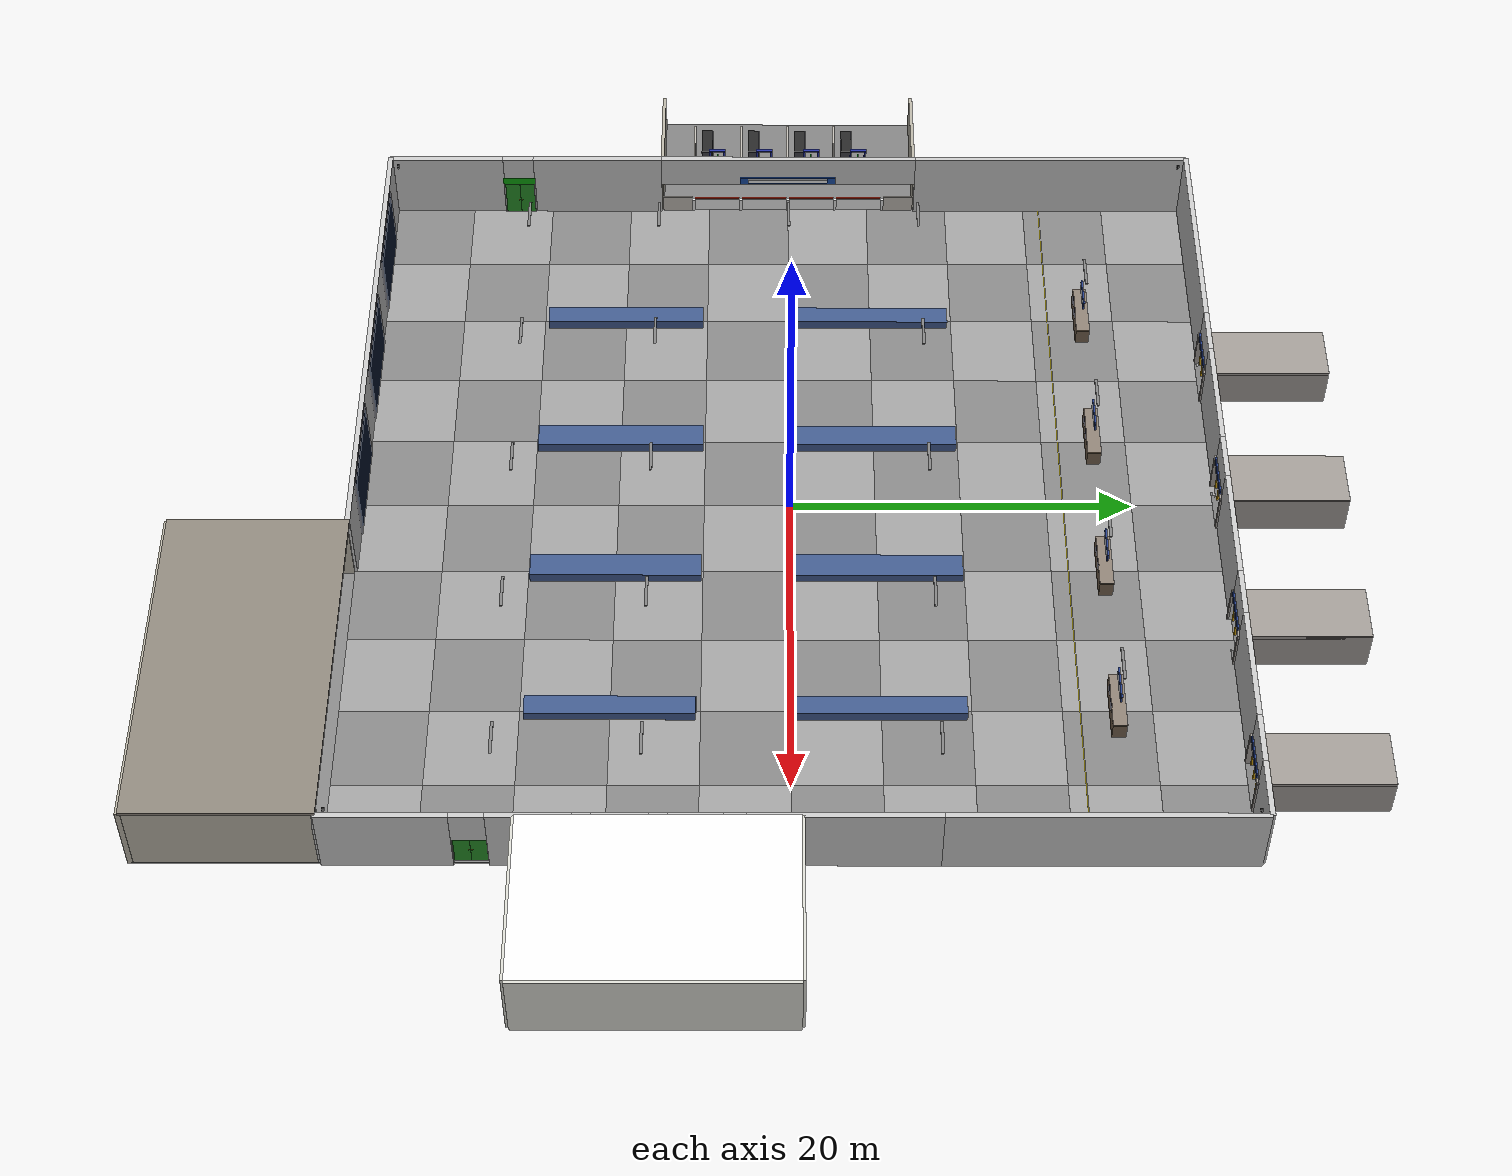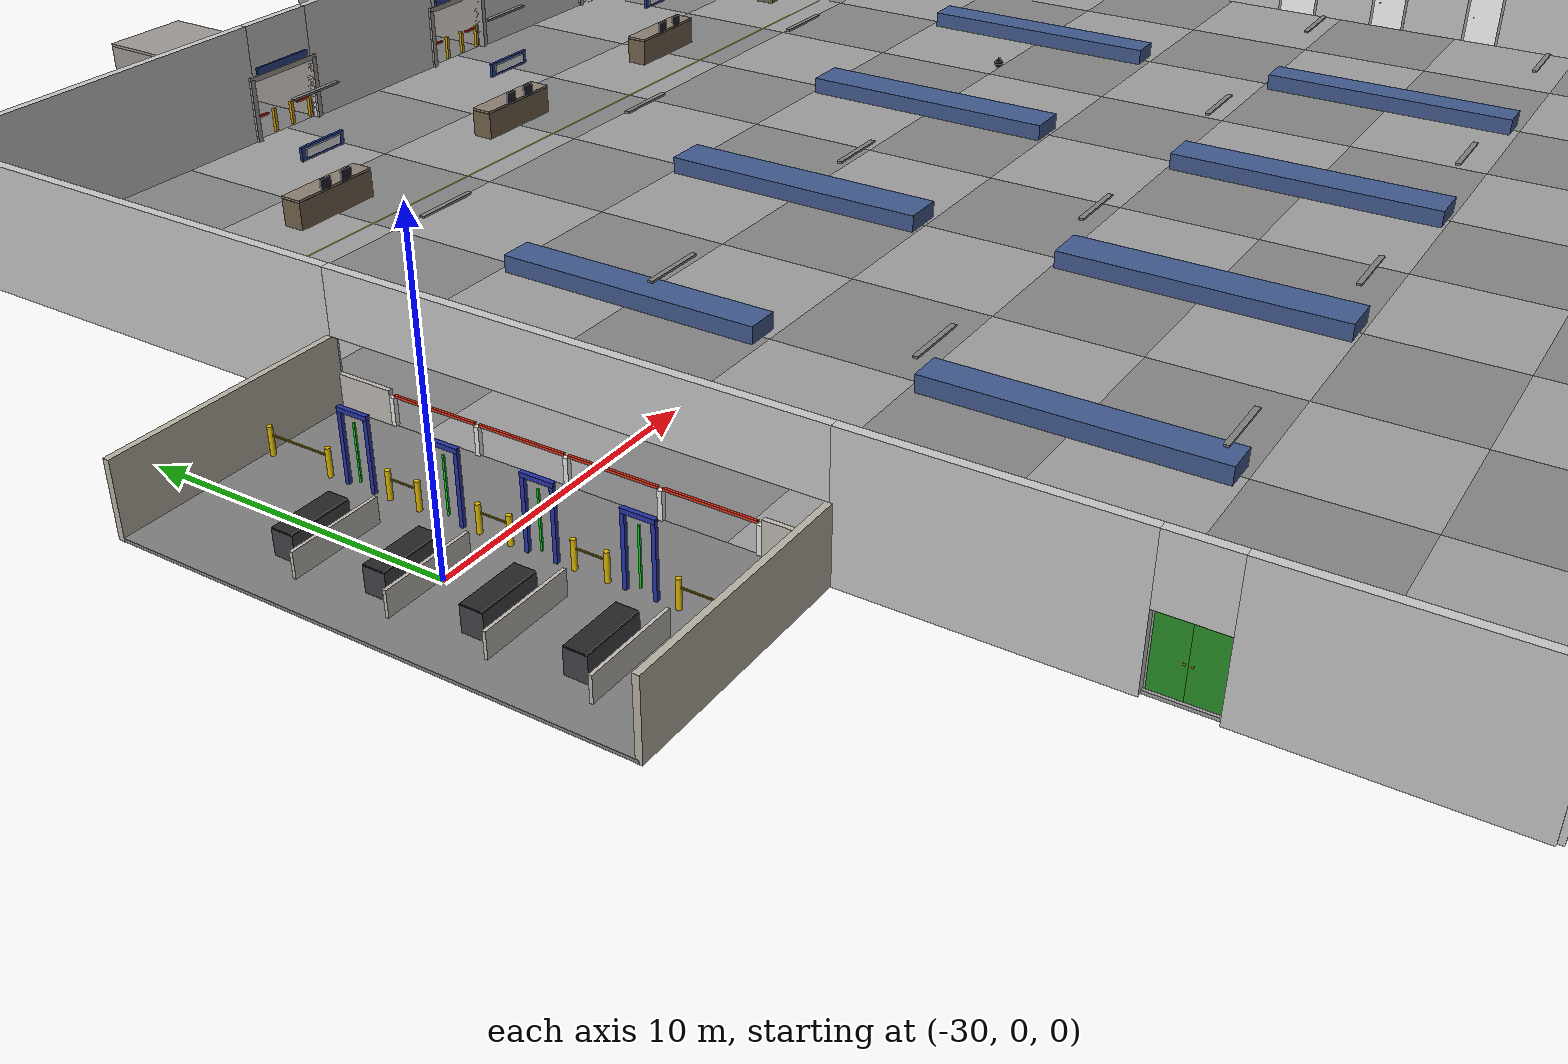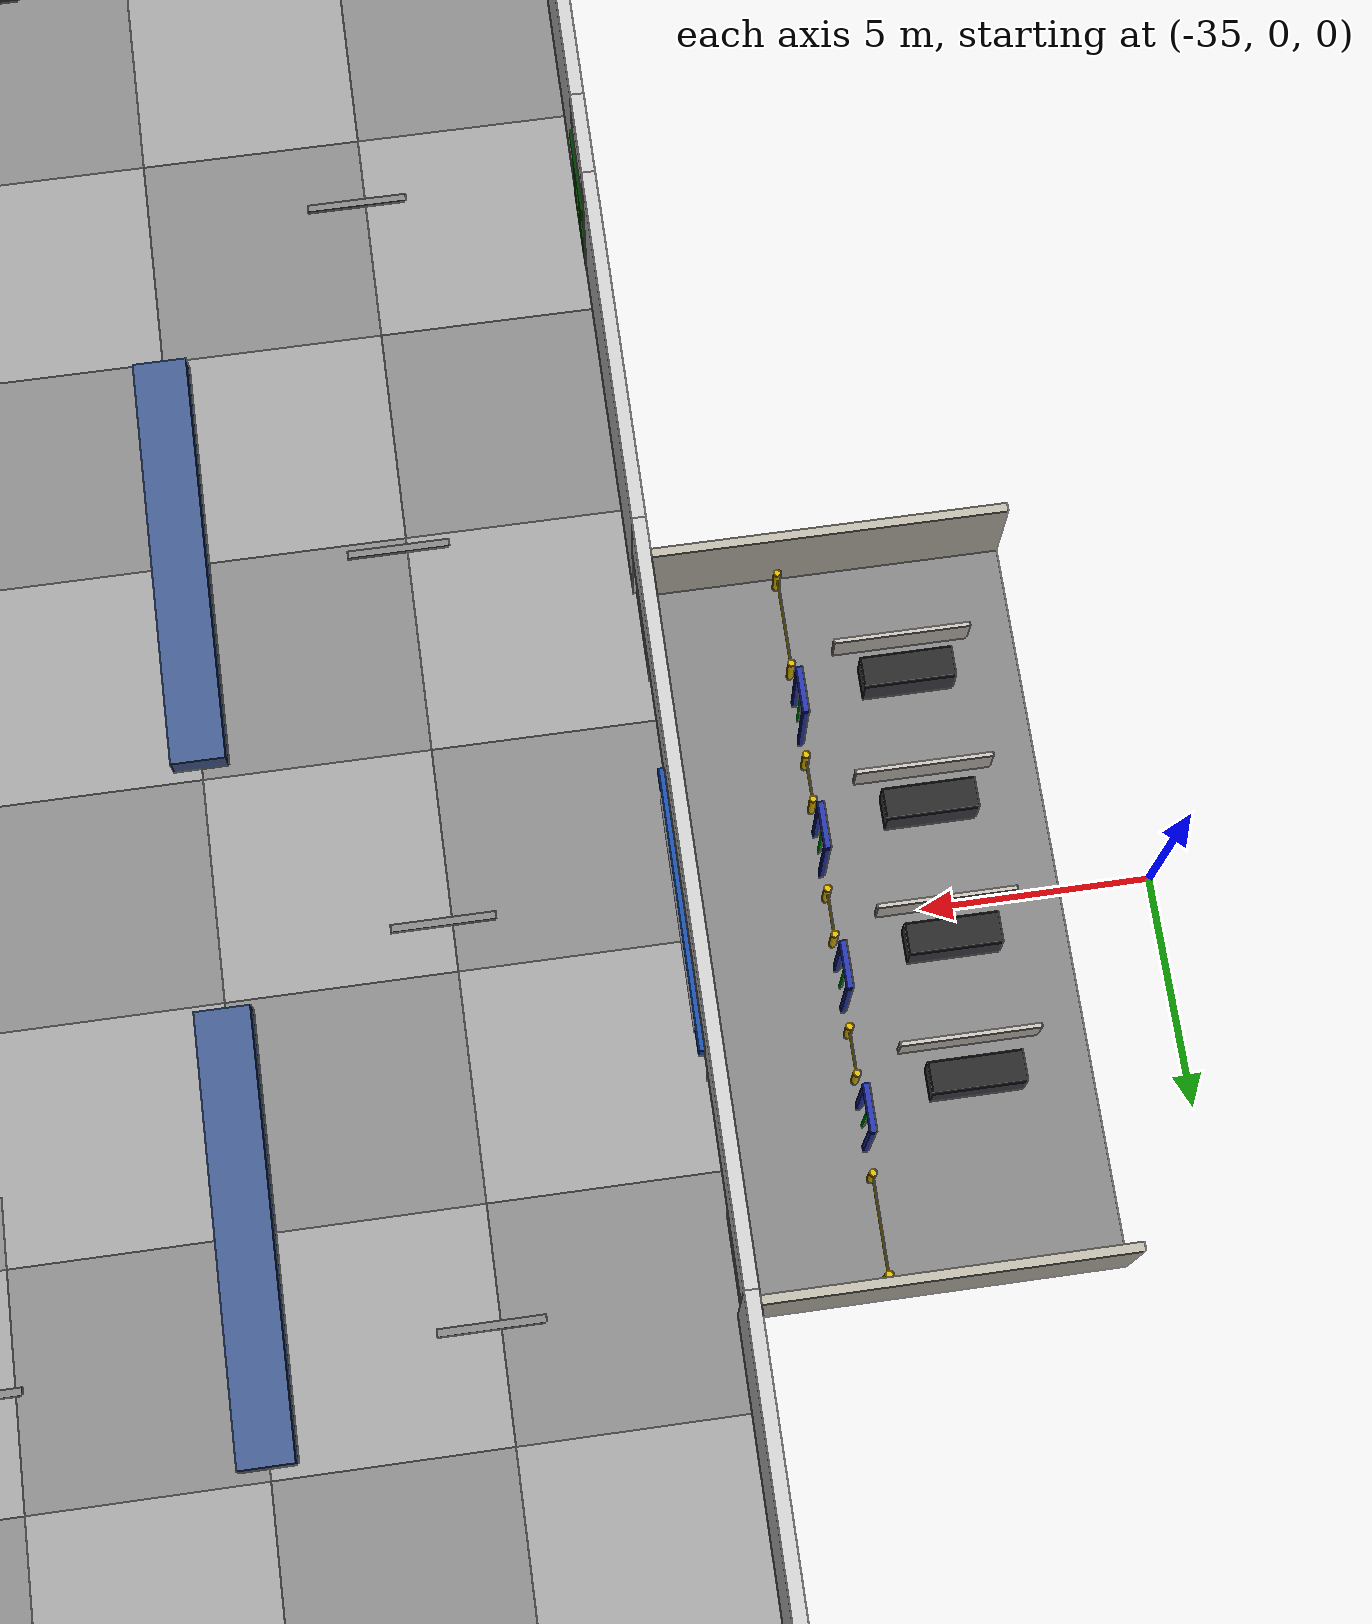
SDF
<?xml version="1.0" ?>
<sdf version="1.10">
  <world name="airport_terminal_world">

    <!--  SYSTEM PLUGINS                                             -->
    <plugin filename="gz-sim-physics-system" name="gz::sim::systems::Physics"/>
    <plugin filename="gz-sim-scene-broadcaster-system" name="gz::sim::systems::SceneBroadcaster"/>
    <plugin filename="gz-sim-user-commands-system" name="gz::sim::systems::UserCommands"/>
    <plugin filename="gz-sim-contact-system" name="gz::sim::systems::Contact"/>
    <plugin filename="gz-sim-sensors-system" name="gz::sim::systems::Sensors">
      <render_engine>ogre2</render_engine>
    </plugin>

    <!--  PHYSICS                                                    -->
    <physics name="default_physics" type="ignored">
      <real_time_factor>1.0</real_time_factor>
      <real_time_update_rate>100.0</real_time_update_rate>
      <max_step_size>0.01</max_step_size>
    </physics>

    <!--  SCENE & LIGHTING                                           -->
    <scene>
      <ambient>0.5 0.5 0.5 1.0</ambient>
      <background>0.53 0.81 0.98 1.0</background>
      <shadows>true</shadows>
    </scene>

    <light name="light_main" type="directional">
      <pose>0 0 10.0 0 0 0</pose>
      <cast_shadows>false</cast_shadows>
      <diffuse>0.6 0.6 0.6 1.0</diffuse>
      <specular>0.1 0.1 0.1 1.0</specular>
      <direction>0.1 0.1 -1.0</direction>
      <attenuation>
        <range>1000.0</range>
        <constant>1.0</constant>
        <linear>0</linear>
        <quadratic>0</quadratic>
      </attenuation>
    </light>

    <!--  FLOOR AND VIRTUAL TILES                                    -->
    <model name="floor">
      <static>true</static>
      <pose>0 0 0.05 0 0 0</pose>
      <link name="link">
        <collision name="col">
          <geometry>
            <box>
              <size>50.0 80.0 0.1</size>
            </box>
          </geometry>
          <surface>
            <friction>
              <ode>
                <mu>0.8</mu>
                <mu2>0.8</mu2>
              </ode>
            </friction>
            <contact>
              <ode>
                <kp>1000000.0</kp>
                <kd>1.0</kd>
                <max_vel>0.1</max_vel>
                <min_depth>0.001</min_depth>
              </ode>
            </contact>
          </surface>
        </collision>
      </link>
    </model>

    <!--  GATE FLOOR MARKINGS (queue lines for passengers)           -->

    <!-- Gate A1 (X=-15) -->
    <model name="gate_a1_queue_line1">
      <static>true</static>
      <pose>-15.0 14.0 0.06 0 0 0</pose>
      <link name="link"><visual name="vis"><geometry><box><size>4.0 0.05 0.01</size></box></geometry>
        <material><ambient>0.95 0.85 0.1 1.0</ambient><diffuse>0.95 0.85 0.1 1.0</diffuse></material></visual></link>
    </model>
    <model name="gate_a1_queue_line2">
      <static>true</static>
      <pose>-15.0 13.0 0.06 0 0 0</pose>
      <link name="link"><visual name="vis"><geometry><box><size>4.0 0.05 0.01</size></box></geometry>
        <material><ambient>0.95 0.85 0.1 1.0</ambient><diffuse>0.95 0.85 0.1 1.0</diffuse></material></visual></link>
    </model>
    <model name="gate_a1_queue_line3">
      <static>true</static>
      <pose>-15.0 12.0 0.06 0 0 0</pose>
      <link name="link"><visual name="vis"><geometry><box><size>4.0 0.05 0.01</size></box></geometry>
        <material><ambient>0.95 0.85 0.1 1.0</ambient><diffuse>0.95 0.85 0.1 1.0</diffuse></material></visual></link>
    </model>
    <model name="gate_a1_queue_side_l">
      <static>true</static>
      <pose>-17.0 13.0 0.06 0 0 0</pose>
      <link name="link"><visual name="vis"><geometry><box><size>0.05 2.0 0.01</size></box></geometry>
        <material><ambient>0.95 0.85 0.1 1.0</ambient><diffuse>0.95 0.85 0.1 1.0</diffuse></material></visual></link>
    </model>
    <model name="gate_a1_queue_side_r">
      <static>true</static>
      <pose>-13.0 13.0 0.06 0 0 0</pose>
      <link name="link"><visual name="vis"><geometry><box><size>0.05 2.0 0.01</size></box></geometry>
        <material><ambient>0.95 0.85 0.1 1.0</ambient><diffuse>0.95 0.85 0.1 1.0</diffuse></material></visual></link>
    </model>

    <!-- Gate A2 (X=-5) -->
    <model name="gate_a2_queue_line1">
      <static>true</static>
      <pose>-5.0 14.0 0.06 0 0 0</pose>
      <link name="link"><visual name="vis"><geometry><box><size>4.0 0.05 0.01</size></box></geometry>
        <material><ambient>0.95 0.85 0.1 1.0</ambient><diffuse>0.95 0.85 0.1 1.0</diffuse></material></visual></link>
    </model>
    <model name="gate_a2_queue_line2">
      <static>true</static>
      <pose>-5.0 13.0 0.06 0 0 0</pose>
      <link name="link"><visual name="vis"><geometry><box><size>4.0 0.05 0.01</size></box></geometry>
        <material><ambient>0.95 0.85 0.1 1.0</ambient><diffuse>0.95 0.85 0.1 1.0</diffuse></material></visual></link>
    </model>
    <model name="gate_a2_queue_line3">
      <static>true</static>
      <pose>-5.0 12.0 0.06 0 0 0</pose>
      <link name="link"><visual name="vis"><geometry><box><size>4.0 0.05 0.01</size></box></geometry>
        <material><ambient>0.95 0.85 0.1 1.0</ambient><diffuse>0.95 0.85 0.1 1.0</diffuse></material></visual></link>
    </model>
    <model name="gate_a2_queue_side_l">
      <static>true</static>
      <pose>-7.0 13.0 0.06 0 0 0</pose>
      <link name="link"><visual name="vis"><geometry><box><size>0.05 2.0 0.01</size></box></geometry>
        <material><ambient>0.95 0.85 0.1 1.0</ambient><diffuse>0.95 0.85 0.1 1.0</diffuse></material></visual></link>
    </model>
    <model name="gate_a2_queue_side_r">
      <static>true</static>
      <pose>-3.0 13.0 0.06 0 0 0</pose>
      <link name="link"><visual name="vis"><geometry><box><size>0.05 2.0 0.01</size></box></geometry>
        <material><ambient>0.95 0.85 0.1 1.0</ambient><diffuse>0.95 0.85 0.1 1.0</diffuse></material></visual></link>
    </model>

    <!-- Gate A3 (X=5) -->
    <model name="gate_a3_queue_line1">
      <static>true</static>
      <pose>5.0 14.0 0.06 0 0 0</pose>
      <link name="link"><visual name="vis"><geometry><box><size>4.0 0.05 0.01</size></box></geometry>
        <material><ambient>0.95 0.85 0.1 1.0</ambient><diffuse>0.95 0.85 0.1 1.0</diffuse></material></visual></link>
    </model>
    <model name="gate_a3_queue_line2">
      <static>true</static>
      <pose>5.0 13.0 0.06 0 0 0</pose>
      <link name="link"><visual name="vis"><geometry><box><size>4.0 0.05 0.01</size></box></geometry>
        <material><ambient>0.95 0.85 0.1 1.0</ambient><diffuse>0.95 0.85 0.1 1.0</diffuse></material></visual></link>
    </model>
    <model name="gate_a3_queue_line3">
      <static>true</static>
      <pose>5.0 12.0 0.06 0 0 0</pose>
      <link name="link"><visual name="vis"><geometry><box><size>4.0 0.05 0.01</size></box></geometry>
        <material><ambient>0.95 0.85 0.1 1.0</ambient><diffuse>0.95 0.85 0.1 1.0</diffuse></material></visual></link>
    </model>
    <model name="gate_a3_queue_side_l">
      <static>true</static>
      <pose>3.0 13.0 0.06 0 0 0</pose>
      <link name="link"><visual name="vis"><geometry><box><size>0.05 2.0 0.01</size></box></geometry>
        <material><ambient>0.95 0.85 0.1 1.0</ambient><diffuse>0.95 0.85 0.1 1.0</diffuse></material></visual></link>
    </model>
    <model name="gate_a3_queue_side_r">
      <static>true</static>
      <pose>7.0 13.0 0.06 0 0 0</pose>
      <link name="link"><visual name="vis"><geometry><box><size>0.05 2.0 0.01</size></box></geometry>
        <material><ambient>0.95 0.85 0.1 1.0</ambient><diffuse>0.95 0.85 0.1 1.0</diffuse></material></visual></link>
    </model>

    <!-- Gate A4 (X=15) -->
    <model name="gate_a4_queue_line1">
      <static>true</static>
      <pose>15.0 14.0 0.06 0 0 0</pose>
      <link name="link"><visual name="vis"><geometry><box><size>4.0 0.05 0.01</size></box></geometry>
        <material><ambient>0.95 0.85 0.1 1.0</ambient><diffuse>0.95 0.85 0.1 1.0</diffuse></material></visual></link>
    </model>
    <model name="gate_a4_queue_line2">
      <static>true</static>
      <pose>15.0 13.0 0.06 0 0 0</pose>
      <link name="link"><visual name="vis"><geometry><box><size>4.0 0.05 0.01</size></box></geometry>
        <material><ambient>0.95 0.85 0.1 1.0</ambient><diffuse>0.95 0.85 0.1 1.0</diffuse></material></visual></link>
    </model>
    <model name="gate_a4_queue_line3">
      <static>true</static>
      <pose>15.0 12.0 0.06 0 0 0</pose>
      <link name="link"><visual name="vis"><geometry><box><size>4.0 0.05 0.01</size></box></geometry>
        <material><ambient>0.95 0.85 0.1 1.0</ambient><diffuse>0.95 0.85 0.1 1.0</diffuse></material></visual></link>
    </model>
    <model name="gate_a4_queue_side_l">
      <static>true</static>
      <pose>13.0 13.0 0.06 0 0 0</pose>
      <link name="link"><visual name="vis"><geometry><box><size>0.05 2.0 0.01</size></box></geometry>
        <material><ambient>0.95 0.85 0.1 1.0</ambient><diffuse>0.95 0.85 0.1 1.0</diffuse></material></visual></link>
    </model>
    <model name="gate_a4_queue_side_r">
      <static>true</static>
      <pose>17.0 13.0 0.06 0 0 0</pose>
      <link name="link"><visual name="vis"><geometry><box><size>0.05 2.0 0.01</size></box></geometry>
        <material><ambient>0.95 0.85 0.1 1.0</ambient><diffuse>0.95 0.85 0.1 1.0</diffuse></material></visual></link>
    </model>

    <model name="boundary_line">
      <static>true</static>
      <pose>0 16.0 0.06 0 0 0</pose>
      <link name="link">
        <visual name="vis">
          <geometry>
            <box>
              <size>49.7 0.05 0.1</size>
            </box>
          </geometry>
          <material>
            <ambient>0.95 0.85 0.1 1.0</ambient>
            <diffuse>0.95 0.85 0.1 1.0</diffuse>
          </material>
        </visual>
      </link>
    </model>

    <model name="vtile_0_0">
      <static>true</static>
      <pose>-22.5 -22.5 0.05 0 0 0</pose>
      <link name="link">
        <visual name="vis">
          <geometry>
            <box>
              <size>5.0 5.0 0.1</size>
            </box>
          </geometry>
          <material>
            <ambient>0.52 0.52 0.52 1.0</ambient>
            <diffuse>0.52 0.52 0.52 1.0</diffuse>
          </material>
        </visual>
      </link>
    </model>

    <model name="vtile_0_1">
      <static>true</static>
      <pose>-22.5 -17.5 0.05 0 0 0</pose>
      <link name="link">
        <visual name="vis">
          <geometry>
            <box>
              <size>5.0 5.0 0.1</size>
            </box>
          </geometry>
          <material>
            <ambient>0.62 0.62 0.62 1.0</ambient>
            <diffuse>0.62 0.62 0.62 1.0</diffuse>
          </material>
        </visual>
      </link>
    </model>

    <model name="vtile_0_2">
      <static>true</static>
      <pose>-22.5 -12.5 0.05 0 0 0</pose>
      <link name="link">
        <visual name="vis">
          <geometry>
            <box>
              <size>5.0 5.0 0.1</size>
            </box>
          </geometry>
          <material>
            <ambient>0.52 0.52 0.52 1.0</ambient>
            <diffuse>0.52 0.52 0.52 1.0</diffuse>
          </material>
        </visual>
      </link>
    </model>

    <model name="vtile_0_3">
      <static>true</static>
      <pose>-22.5 -7.5 0.05 0 0 0</pose>
      <link name="link">
        <visual name="vis">
          <geometry>
            <box>
              <size>5.0 5.0 0.1</size>
            </box>
          </geometry>
          <material>
            <ambient>0.62 0.62 0.62 1.0</ambient>
            <diffuse>0.62 0.62 0.62 1.0</diffuse>
          </material>
        </visual>
      </link>
    </model>

    <model name="vtile_0_4">
      <static>true</static>
      <pose>-22.5 -2.5 0.05 0 0 0</pose>
      <link name="link">
        <visual name="vis">
          <geometry>
            <box>
              <size>5.0 5.0 0.1</size>
            </box>
          </geometry>
          <material>
            <ambient>0.52 0.52 0.52 1.0</ambient>
            <diffuse>0.52 0.52 0.52 1.0</diffuse>
          </material>
        </visual>
      </link>
    </model>

    <model name="vtile_0_5">
      <static>true</static>
      <pose>-22.5 2.5 0.05 0 0 0</pose>
      <link name="link">
        <visual name="vis">
          <geometry>
            <box>
              <size>5.0 5.0 0.1</size>
            </box>
          </geometry>
          <material>
            <ambient>0.62 0.62 0.62 1.0</ambient>
            <diffuse>0.62 0.62 0.62 1.0</diffuse>
          </material>
        </visual>
      </link>
    </model>

    <model name="vtile_0_6">
      <static>true</static>
      <pose>-22.5 7.5 0.05 0 0 0</pose>
      <link name="link">
        <visual name="vis">
          <geometry>
            <box>
              <size>5.0 5.0 0.1</size>
            </box>
          </geometry>
          <material>
            <ambient>0.52 0.52 0.52 1.0</ambient>
            <diffuse>0.52 0.52 0.52 1.0</diffuse>
          </material>
        </visual>
      </link>
    </model>

    <model name="vtile_0_7">
      <static>true</static>
      <pose>-22.5 12.5 0.05 0 0 0</pose>
      <link name="link">
        <visual name="vis">
          <geometry>
            <box>
              <size>5.0 5.0 0.1</size>
            </box>
          </geometry>
          <material>
            <ambient>0.62 0.62 0.62 1.0</ambient>
            <diffuse>0.62 0.62 0.62 1.0</diffuse>
          </material>
        </visual>
      </link>
    </model>

    <model name="vtile_0_8">
      <static>true</static>
      <pose>-22.5 17.5 0.05 0 0 0</pose>
      <link name="link">
        <visual name="vis">
          <geometry>
            <box>
              <size>5.0 5.0 0.1</size>
            </box>
          </geometry>
          <material>
            <ambient>0.52 0.52 0.52 1.0</ambient>
            <diffuse>0.52 0.52 0.52 1.0</diffuse>
          </material>
        </visual>
      </link>
    </model>

    <model name="vtile_0_9">
      <static>true</static>
      <pose>-22.5 22.5 0.05 0 0 0</pose>
      <link name="link">
        <visual name="vis">
          <geometry>
            <box>
              <size>5.0 5.0 0.1</size>
            </box>
          </geometry>
          <material>
            <ambient>0.62 0.62 0.62 1.0</ambient>
            <diffuse>0.62 0.62 0.62 1.0</diffuse>
          </material>
        </visual>
      </link>
    </model>

    <model name="vtile_1_0">
      <static>true</static>
      <pose>-17.5 -22.5 0.05 0 0 0</pose>
      <link name="link">
        <visual name="vis">
          <geometry>
            <box>
              <size>5.0 5.0 0.1</size>
            </box>
          </geometry>
          <material>
            <ambient>0.62 0.62 0.62 1.0</ambient>
            <diffuse>0.62 0.62 0.62 1.0</diffuse>
          </material>
        </visual>
      </link>
    </model>

    <model name="vtile_1_1">
      <static>true</static>
      <pose>-17.5 -17.5 0.05 0 0 0</pose>
      <link name="link">
        <visual name="vis">
          <geometry>
            <box>
              <size>5.0 5.0 0.1</size>
            </box>
          </geometry>
          <material>
            <ambient>0.52 0.52 0.52 1.0</ambient>
            <diffuse>0.52 0.52 0.52 1.0</diffuse>
          </material>
        </visual>
      </link>
    </model>

    <model name="vtile_1_2">
      <static>true</static>
      <pose>-17.5 -12.5 0.05 0 0 0</pose>
      <link name="link">
        <visual name="vis">
          <geometry>
            <box>
              <size>5.0 5.0 0.1</size>
            </box>
          </geometry>
          <material>
            <ambient>0.62 0.62 0.62 1.0</ambient>
            <diffuse>0.62 0.62 0.62 1.0</diffuse>
          </material>
        </visual>
      </link>
    </model>

    <model name="vtile_1_3">
      <static>true</static>
      <pose>-17.5 -7.5 0.05 0 0 0</pose>
      <link name="link">
        <visual name="vis">
          <geometry>
            <box>
              <size>5.0 5.0 0.1</size>
            </box>
          </geometry>
          <material>
            <ambient>0.52 0.52 0.52 1.0</ambient>
            <diffuse>0.52 0.52 0.52 1.0</diffuse>
          </material>
        </visual>
      </link>
    </model>

    <model name="vtile_1_4">
      <static>true</static>
      <pose>-17.5 -2.5 0.05 0 0 0</pose>
      <link name="link">
        <visual name="vis">
          <geometry>
            <box>
              <size>5.0 5.0 0.1</size>
            </box>
          </geometry>
          <material>
            <ambient>0.62 0.62 0.62 1.0</ambient>
            <diffuse>0.62 0.62 0.62 1.0</diffuse>
          </material>
        </visual>
      </link>
    </model>

    <model name="vtile_1_5">
      <static>true</static>
      <pose>-17.5 2.5 0.05 0 0 0</pose>
      <link name="link">
        <visual name="vis">
          <geometry>
            <box>
              <size>5.0 5.0 0.1</size>
            </box>
          </geometry>
          <material>
            <ambient>0.52 0.52 0.52 1.0</ambient>
            <diffuse>0.52 0.52 0.52 1.0</diffuse>
          </material>
        </visual>
      </link>
    </model>

    <model name="vtile_1_6">
      <static>true</static>
      <pose>-17.5 7.5 0.05 0 0 0</pose>
      <link name="link">
        <visual name="vis">
          <geometry>
            <box>
              <size>5.0 5.0 0.1</size>
            </box>
          </geometry>
          <material>
            <ambient>0.62 0.62 0.62 1.0</ambient>
            <diffuse>0.62 0.62 0.62 1.0</diffuse>
          </material>
        </visual>
      </link>
    </model>

    <model name="vtile_1_7">
      <static>true</static>
      <pose>-17.5 12.5 0.05 0 0 0</pose>
      <link name="link">
        <visual name="vis">
          <geometry>
            <box>
              <size>5.0 5.0 0.1</size>
            </box>
          </geometry>
          <material>
            <ambient>0.52 0.52 0.52 1.0</ambient>
            <diffuse>0.52 0.52 0.52 1.0</diffuse>
          </material>
        </visual>
      </link>
    </model>

    <model name="vtile_1_8">
      <static>true</static>
      <pose>-17.5 17.5 0.05 0 0 0</pose>
      <link name="link">
        <visual name="vis">
          <geometry>
            <box>
              <size>5.0 5.0 0.1</size>
            </box>
          </geometry>
          <material>
            <ambient>0.62 0.62 0.62 1.0</ambient>
            <diffuse>0.62 0.62 0.62 1.0</diffuse>
          </material>
        </visual>
      </link>
    </model>

    <model name="vtile_1_9">
      <static>true</static>
      <pose>-17.5 22.5 0.05 0 0 0</pose>
      <link name="link">
        <visual name="vis">
          <geometry>
            <box>
              <size>5.0 5.0 0.1</size>
            </box>
          </geometry>
          <material>
            <ambient>0.52 0.52 0.52 1.0</ambient>
            <diffuse>0.52 0.52 0.52 1.0</diffuse>
          </material>
        </visual>
      </link>
    </model>

    <model name="vtile_2_0">
      <static>true</static>
      <pose>-12.5 -22.5 0.05 0 0 0</pose>
      <link name="link">
        <visual name="vis">
          <geometry>
            <box>
              <size>5.0 5.0 0.1</size>
            </box>
          </geometry>
          <material>
            <ambient>0.52 0.52 0.52 1.0</ambient>
            <diffuse>0.52 0.52 0.52 1.0</diffuse>
          </material>
        </visual>
      </link>
    </model>

    <model name="vtile_2_1">
      <static>true</static>
      <pose>-12.5 -17.5 0.05 0 0 0</pose>
      <link name="link">
        <visual name="vis">
          <geometry>
            <box>
              <size>5.0 5.0 0.1</size>
            </box>
          </geometry>
          <material>
            <ambient>0.62 0.62 0.62 1.0</ambient>
            <diffuse>0.62 0.62 0.62 1.0</diffuse>
          </material>
        </visual>
      </link>
    </model>

    <model name="vtile_2_2">
      <static>true</static>
      <pose>-12.5 -12.5 0.05 0 0 0</pose>
      <link name="link">
        <visual name="vis">
          <geometry>
            <box>
              <size>5.0 5.0 0.1</size>
            </box>
          </geometry>
          <material>
            <ambient>0.52 0.52 0.52 1.0</ambient>
            <diffuse>0.52 0.52 0.52 1.0</diffuse>
          </material>
        </visual>
      </link>
    </model>

    <model name="vtile_2_3">
      <static>true</static>
      <pose>-12.5 -7.5 0.05 0 0 0</pose>
      <link name="link">
        <visual name="vis">
          <geometry>
            <box>
              <size>5.0 5.0 0.1</size>
            </box>
          </geometry>
          <material>
            <ambient>0.62 0.62 0.62 1.0</ambient>
            <diffuse>0.62 0.62 0.62 1.0</diffuse>
          </material>
        </visual>
      </link>
    </model>

    <model name="vtile_2_4">
      <static>true</static>
      <pose>-12.5 -2.5 0.05 0 0 0</pose>
      <link name="link">
        <visual name="vis">
          <geometry>
            <box>
              <size>5.0 5.0 0.1</size>
            </box>
          </geometry>
          <material>
            <ambient>0.52 0.52 0.52 1.0</ambient>
            <diffuse>0.52 0.52 0.52 1.0</diffuse>
          </material>
        </visual>
      </link>
    </model>

    <model name="vtile_2_5">
      <static>true</static>
      <pose>-12.5 2.5 0.05 0 0 0</pose>
      <link name="link">
        <visual name="vis">
          <geometry>
            <box>
              <size>5.0 5.0 0.1</size>
            </box>
          </geometry>
          <material>
            <ambient>0.62 0.62 0.62 1.0</ambient>
            <diffuse>0.62 0.62 0.62 1.0</diffuse>
          </material>
        </visual>
      </link>
    </model>

    <model name="vtile_2_6">
      <static>true</static>
      <pose>-12.5 7.5 0.05 0 0 0</pose>
      <link name="link">
        <visual name="vis">
          <geometry>
            <box>
              <size>5.0 5.0 0.1</size>
            </box>
          </geometry>
          <material>
            <ambient>0.52 0.52 0.52 1.0</ambient>
            <diffuse>0.52 0.52 0.52 1.0</diffuse>
          </material>
        </visual>
      </link>
    </model>

    <model name="vtile_2_7">
      <static>true</static>
      <pose>-12.5 12.5 0.05 0 0 0</pose>
      <link name="link">
        <visual name="vis">
          <geometry>
            <box>
              <size>5.0 5.0 0.1</size>
            </box>
          </geometry>
          <material>
            <ambient>0.62 0.62 0.62 1.0</ambient>
            <diffuse>0.62 0.62 0.62 1.0</diffuse>
          </material>
        </visual>
      </link>
    </model>

    <model name="vtile_2_8">
      <static>true</static>
      <pose>-12.5 17.5 0.05 0 0 0</pose>
      <link name="link">
        <visual name="vis">
          <geometry>
            <box>
              <size>5.0 5.0 0.1</size>
            </box>
          </geometry>
          <material>
            <ambient>0.52 0.52 0.52 1.0</ambient>
            <diffuse>0.52 0.52 0.52 1.0</diffuse>
          </material>
        </visual>
      </link>
    </model>

    <model name="vtile_2_9">
      <static>true</static>
      <pose>-12.5 22.5 0.05 0 0 0</pose>
      <link name="link">
        <visual name="vis">
          <geometry>
            <box>
              <size>5.0 5.0 0.1</size>
            </box>
          </geometry>
          <material>
            <ambient>0.62 0.62 0.62 1.0</ambient>
            <diffuse>0.62 0.62 0.62 1.0</diffuse>
          </material>
        </visual>
      </link>
    </model>

    <model name="vtile_3_0">
      <static>true</static>
      <pose>-7.5 -22.5 0.05 0 0 0</pose>
      <link name="link">
        <visual name="vis">
          <geometry>
            <box>
              <size>5.0 5.0 0.1</size>
            </box>
          </geometry>
          <material>
            <ambient>0.62 0.62 0.62 1.0</ambient>
            <diffuse>0.62 0.62 0.62 1.0</diffuse>
          </material>
        </visual>
      </link>
    </model>

    <model name="vtile_3_1">
      <static>true</static>
      <pose>-7.5 -17.5 0.05 0 0 0</pose>
      <link name="link">
        <visual name="vis">
          <geometry>
            <box>
              <size>5.0 5.0 0.1</size>
            </box>
          </geometry>
          <material>
            <ambient>0.52 0.52 0.52 1.0</ambient>
            <diffuse>0.52 0.52 0.52 1.0</diffuse>
          </material>
        </visual>
      </link>
    </model>

    <model name="vtile_3_2">
      <static>true</static>
      <pose>-7.5 -12.5 0.05 0 0 0</pose>
      <link name="link">
        <visual name="vis">
          <geometry>
            <box>
              <size>5.0 5.0 0.1</size>
            </box>
          </geometry>
          <material>
            <ambient>0.62 0.62 0.62 1.0</ambient>
            <diffuse>0.62 0.62 0.62 1.0</diffuse>
          </material>
        </visual>
      </link>
    </model>

    <model name="vtile_3_3">
      <static>true</static>
      <pose>-7.5 -7.5 0.05 0 0 0</pose>
      <link name="link">
        <visual name="vis">
          <geometry>
            <box>
              <size>5.0 5.0 0.1</size>
            </box>
          </geometry>
          <material>
            <ambient>0.52 0.52 0.52 1.0</ambient>
            <diffuse>0.52 0.52 0.52 1.0</diffuse>
          </material>
        </visual>
      </link>
    </model>

    <model name="vtile_3_4">
      <static>true</static>
      <pose>-7.5 -2.5 0.05 0 0 0</pose>
      <link name="link">
        <visual name="vis">
          <geometry>
            <box>
              <size>5.0 5.0 0.1</size>
            </box>
          </geometry>
          <material>
            <ambient>0.62 0.62 0.62 1.0</ambient>
            <diffuse>0.62 0.62 0.62 1.0</diffuse>
          </material>
        </visual>
      </link>
    </model>

    <model name="vtile_3_5">
      <static>true</static>
      <pose>-7.5 2.5 0.05 0 0 0</pose>
      <link name="link">
        <visual name="vis">
          <geometry>
            <box>
              <size>5.0 5.0 0.1</size>
            </box>
          </geometry>
          <material>
            <ambient>0.52 0.52 0.52 1.0</ambient>
            <diffuse>0.52 0.52 0.52 1.0</diffuse>
          </material>
        </visual>
      </link>
    </model>

    <model name="vtile_3_6">
      <static>true</static>
      <pose>-7.5 7.5 0.05 0 0 0</pose>
      <link name="link">
        <visual name="vis">
          <geometry>
            <box>
              <size>5.0 5.0 0.1</size>
            </box>
          </geometry>
          <material>
            <ambient>0.62 0.62 0.62 1.0</ambient>
            <diffuse>0.62 0.62 0.62 1.0</diffuse>
          </material>
        </visual>
      </link>
    </model>

    <model name="vtile_3_7">
      <static>true</static>
      <pose>-7.5 12.5 0.05 0 0 0</pose>
      <link name="link">
        <visual name="vis">
          <geometry>
            <box>
              <size>5.0 5.0 0.1</size>
            </box>
          </geometry>
          <material>
            <ambient>0.52 0.52 0.52 1.0</ambient>
            <diffuse>0.52 0.52 0.52 1.0</diffuse>
          </material>
        </visual>
      </link>
    </model>

    <model name="vtile_3_8">
      <static>true</static>
      <pose>-7.5 17.5 0.05 0 0 0</pose>
      <link name="link">
        <visual name="vis">
          <geometry>
            <box>
              <size>5.0 5.0 0.1</size>
            </box>
          </geometry>
          <material>
            <ambient>0.62 0.62 0.62 1.0</ambient>
            <diffuse>0.62 0.62 0.62 1.0</diffuse>
          </material>
        </visual>
      </link>
    </model>

    <model name="vtile_3_9">
      <static>true</static>
      <pose>-7.5 22.5 0.05 0 0 0</pose>
      <link name="link">
        <visual name="vis">
          <geometry>
            <box>
              <size>5.0 5.0 0.1</size>
            </box>
          </geometry>
          <material>
            <ambient>0.52 0.52 0.52 1.0</ambient>
            <diffuse>0.52 0.52 0.52 1.0</diffuse>
          </material>
        </visual>
      </link>
    </model>

    <model name="vtile_4_0">
      <static>true</static>
      <pose>-2.5 -22.5 0.05 0 0 0</pose>
      <link name="link">
        <visual name="vis">
          <geometry>
            <box>
              <size>5.0 5.0 0.1</size>
            </box>
          </geometry>
          <material>
            <ambient>0.52 0.52 0.52 1.0</ambient>
            <diffuse>0.52 0.52 0.52 1.0</diffuse>
          </material>
        </visual>
      </link>
    </model>

    <model name="vtile_4_1">
      <static>true</static>
      <pose>-2.5 -17.5 0.05 0 0 0</pose>
      <link name="link">
        <visual name="vis">
          <geometry>
            <box>
              <size>5.0 5.0 0.1</size>
            </box>
          </geometry>
          <material>
            <ambient>0.62 0.62 0.62 1.0</ambient>
            <diffuse>0.62 0.62 0.62 1.0</diffuse>
          </material>
        </visual>
      </link>
    </model>

    <model name="vtile_4_2">
      <static>true</static>
      <pose>-2.5 -12.5 0.05 0 0 0</pose>
      <link name="link">
        <visual name="vis">
          <geometry>
            <box>
              <size>5.0 5.0 0.1</size>
            </box>
          </geometry>
          <material>
            <ambient>0.52 0.52 0.52 1.0</ambient>
            <diffuse>0.52 0.52 0.52 1.0</diffuse>
          </material>
        </visual>
      </link>
    </model>

    <model name="vtile_4_3">
      <static>true</static>
      <pose>-2.5 -7.5 0.05 0 0 0</pose>
      <link name="link">
        <visual name="vis">
          <geometry>
            <box>
              <size>5.0 5.0 0.1</size>
            </box>
          </geometry>
          <material>
            <ambient>0.62 0.62 0.62 1.0</ambient>
            <diffuse>0.62 0.62 0.62 1.0</diffuse>
          </material>
        </visual>
      </link>
    </model>

    <model name="vtile_4_4">
      <static>true</static>
      <pose>-2.5 -2.5 0.05 0 0 0</pose>
      <link name="link">
        <visual name="vis">
          <geometry>
            <box>
              <size>5.0 5.0 0.1</size>
            </box>
          </geometry>
          <material>
            <ambient>0.52 0.52 0.52 1.0</ambient>
            <diffuse>0.52 0.52 0.52 1.0</diffuse>
          </material>
        </visual>
      </link>
    </model>

    <model name="vtile_4_5">
      <static>true</static>
      <pose>-2.5 2.5 0.05 0 0 0</pose>
      <link name="link">
        <visual name="vis">
          <geometry>
            <box>
              <size>5.0 5.0 0.1</size>
            </box>
          </geometry>
          <material>
            <ambient>0.62 0.62 0.62 1.0</ambient>
            <diffuse>0.62 0.62 0.62 1.0</diffuse>
          </material>
        </visual>
      </link>
    </model>

    <model name="vtile_4_6">
      <static>true</static>
      <pose>-2.5 7.5 0.05 0 0 0</pose>
      <link name="link">
        <visual name="vis">
          <geometry>
            <box>
              <size>5.0 5.0 0.1</size>
            </box>
          </geometry>
          <material>
            <ambient>0.52 0.52 0.52 1.0</ambient>
            <diffuse>0.52 0.52 0.52 1.0</diffuse>
          </material>
        </visual>
      </link>
    </model>

    <model name="vtile_4_7">
      <static>true</static>
      <pose>-2.5 12.5 0.05 0 0 0</pose>
      <link name="link">
        <visual name="vis">
          <geometry>
            <box>
              <size>5.0 5.0 0.1</size>
            </box>
          </geometry>
          <material>
            <ambient>0.62 0.62 0.62 1.0</ambient>
            <diffuse>0.62 0.62 0.62 1.0</diffuse>
          </material>
        </visual>
      </link>
    </model>

    <model name="vtile_4_8">
      <static>true</static>
      <pose>-2.5 17.5 0.05 0 0 0</pose>
      <link name="link">
        <visual name="vis">
          <geometry>
            <box>
              <size>5.0 5.0 0.1</size>
            </box>
          </geometry>
          <material>
            <ambient>0.52 0.52 0.52 1.0</ambient>
            <diffuse>0.52 0.52 0.52 1.0</diffuse>
          </material>
        </visual>
      </link>
    </model>

    <model name="vtile_4_9">
      <static>true</static>
      <pose>-2.5 22.5 0.05 0 0 0</pose>
      <link name="link">
        <visual name="vis">
          <geometry>
            <box>
              <size>5.0 5.0 0.1</size>
            </box>
          </geometry>
          <material>
            <ambient>0.62 0.62 0.62 1.0</ambient>
            <diffuse>0.62 0.62 0.62 1.0</diffuse>
          </material>
        </visual>
      </link>
    </model>

    <model name="vtile_5_0">
      <static>true</static>
      <pose>2.5 -22.5 0.05 0 0 0</pose>
      <link name="link">
        <visual name="vis">
          <geometry>
            <box>
              <size>5.0 5.0 0.1</size>
            </box>
          </geometry>
          <material>
            <ambient>0.62 0.62 0.62 1.0</ambient>
            <diffuse>0.62 0.62 0.62 1.0</diffuse>
          </material>
        </visual>
      </link>
    </model>

    <model name="vtile_5_1">
      <static>true</static>
      <pose>2.5 -17.5 0.05 0 0 0</pose>
      <link name="link">
        <visual name="vis">
          <geometry>
            <box>
              <size>5.0 5.0 0.1</size>
            </box>
          </geometry>
          <material>
            <ambient>0.52 0.52 0.52 1.0</ambient>
            <diffuse>0.52 0.52 0.52 1.0</diffuse>
          </material>
        </visual>
      </link>
    </model>

    <model name="vtile_5_2">
      <static>true</static>
      <pose>2.5 -12.5 0.05 0 0 0</pose>
      <link name="link">
        <visual name="vis">
          <geometry>
            <box>
              <size>5.0 5.0 0.1</size>
            </box>
          </geometry>
          <material>
            <ambient>0.62 0.62 0.62 1.0</ambient>
            <diffuse>0.62 0.62 0.62 1.0</diffuse>
          </material>
        </visual>
      </link>
    </model>

    <model name="vtile_5_3">
      <static>true</static>
      <pose>2.5 -7.5 0.05 0 0 0</pose>
      <link name="link">
        <visual name="vis">
          <geometry>
            <box>
              <size>5.0 5.0 0.1</size>
            </box>
          </geometry>
          <material>
            <ambient>0.52 0.52 0.52 1.0</ambient>
            <diffuse>0.52 0.52 0.52 1.0</diffuse>
          </material>
        </visual>
      </link>
    </model>

    <model name="vtile_5_4">
      <static>true</static>
      <pose>2.5 -2.5 0.05 0 0 0</pose>
      <link name="link">
        <visual name="vis">
          <geometry>
            <box>
              <size>5.0 5.0 0.1</size>
            </box>
          </geometry>
          <material>
            <ambient>0.62 0.62 0.62 1.0</ambient>
            <diffuse>0.62 0.62 0.62 1.0</diffuse>
          </material>
        </visual>
      </link>
    </model>

    <model name="vtile_5_5">
      <static>true</static>
      <pose>2.5 2.5 0.05 0 0 0</pose>
      <link name="link">
        <visual name="vis">
          <geometry>
            <box>
              <size>5.0 5.0 0.1</size>
            </box>
          </geometry>
          <material>
            <ambient>0.52 0.52 0.52 1.0</ambient>
            <diffuse>0.52 0.52 0.52 1.0</diffuse>
          </material>
        </visual>
      </link>
    </model>

    <model name="vtile_5_6">
      <static>true</static>
      <pose>2.5 7.5 0.05 0 0 0</pose>
      <link name="link">
        <visual name="vis">
          <geometry>
            <box>
              <size>5.0 5.0 0.1</size>
            </box>
          </geometry>
          <material>
            <ambient>0.62 0.62 0.62 1.0</ambient>
            <diffuse>0.62 0.62 0.62 1.0</diffuse>
          </material>
        </visual>
      </link>
    </model>

    <model name="vtile_5_7">
      <static>true</static>
      <pose>2.5 12.5 0.05 0 0 0</pose>
      <link name="link">
        <visual name="vis">
          <geometry>
            <box>
              <size>5.0 5.0 0.1</size>
            </box>
          </geometry>
          <material>
            <ambient>0.52 0.52 0.52 1.0</ambient>
            <diffuse>0.52 0.52 0.52 1.0</diffuse>
          </material>
        </visual>
      </link>
    </model>

    <model name="vtile_5_8">
      <static>true</static>
      <pose>2.5 17.5 0.05 0 0 0</pose>
      <link name="link">
        <visual name="vis">
          <geometry>
            <box>
              <size>5.0 5.0 0.1</size>
            </box>
          </geometry>
          <material>
            <ambient>0.62 0.62 0.62 1.0</ambient>
            <diffuse>0.62 0.62 0.62 1.0</diffuse>
          </material>
        </visual>
      </link>
    </model>

    <model name="vtile_5_9">
      <static>true</static>
      <pose>2.5 22.5 0.05 0 0 0</pose>
      <link name="link">
        <visual name="vis">
          <geometry>
            <box>
              <size>5.0 5.0 0.1</size>
            </box>
          </geometry>
          <material>
            <ambient>0.52 0.52 0.52 1.0</ambient>
            <diffuse>0.52 0.52 0.52 1.0</diffuse>
          </material>
        </visual>
      </link>
    </model>

    <model name="vtile_6_0">
      <static>true</static>
      <pose>7.5 -22.5 0.05 0 0 0</pose>
      <link name="link">
        <visual name="vis">
          <geometry>
            <box>
              <size>5.0 5.0 0.1</size>
            </box>
          </geometry>
          <material>
            <ambient>0.52 0.52 0.52 1.0</ambient>
            <diffuse>0.52 0.52 0.52 1.0</diffuse>
          </material>
        </visual>
      </link>
    </model>

    <model name="vtile_6_1">
      <static>true</static>
      <pose>7.5 -17.5 0.05 0 0 0</pose>
      <link name="link">
        <visual name="vis">
          <geometry>
            <box>
              <size>5.0 5.0 0.1</size>
            </box>
          </geometry>
          <material>
            <ambient>0.62 0.62 0.62 1.0</ambient>
            <diffuse>0.62 0.62 0.62 1.0</diffuse>
          </material>
        </visual>
      </link>
    </model>

    <model name="vtile_6_2">
      <static>true</static>
      <pose>7.5 -12.5 0.05 0 0 0</pose>
      <link name="link">
        <visual name="vis">
          <geometry>
            <box>
              <size>5.0 5.0 0.1</size>
            </box>
          </geometry>
          <material>
            <ambient>0.52 0.52 0.52 1.0</ambient>
            <diffuse>0.52 0.52 0.52 1.0</diffuse>
          </material>
        </visual>
      </link>
    </model>

    <model name="vtile_6_3">
      <static>true</static>
      <pose>7.5 -7.5 0.05 0 0 0</pose>
      <link name="link">
        <visual name="vis">
          <geometry>
            <box>
              <size>5.0 5.0 0.1</size>
            </box>
          </geometry>
          <material>
            <ambient>0.62 0.62 0.62 1.0</ambient>
            <diffuse>0.62 0.62 0.62 1.0</diffuse>
          </material>
        </visual>
      </link>
    </model>

    <model name="vtile_6_4">
      <static>true</static>
      <pose>7.5 -2.5 0.05 0 0 0</pose>
      <link name="link">
        <visual name="vis">
          <geometry>
            <box>
              <size>5.0 5.0 0.1</size>
            </box>
          </geometry>
          <material>
            <ambient>0.52 0.52 0.52 1.0</ambient>
            <diffuse>0.52 0.52 0.52 1.0</diffuse>
          </material>
        </visual>
      </link>
    </model>

    <model name="vtile_6_5">
      <static>true</static>
      <pose>7.5 2.5 0.05 0 0 0</pose>
      <link name="link">
        <visual name="vis">
          <geometry>
            <box>
              <size>5.0 5.0 0.1</size>
            </box>
          </geometry>
          <material>
            <ambient>0.62 0.62 0.62 1.0</ambient>
            <diffuse>0.62 0.62 0.62 1.0</diffuse>
          </material>
        </visual>
      </link>
    </model>

    <model name="vtile_6_6">
      <static>true</static>
      <pose>7.5 7.5 0.05 0 0 0</pose>
      <link name="link">
        <visual name="vis">
          <geometry>
            <box>
              <size>5.0 5.0 0.1</size>
            </box>
          </geometry>
          <material>
            <ambient>0.52 0.52 0.52 1.0</ambient>
            <diffuse>0.52 0.52 0.52 1.0</diffuse>
          </material>
        </visual>
      </link>
    </model>

    <model name="vtile_6_7">
      <static>true</static>
      <pose>7.5 12.5 0.05 0 0 0</pose>
      <link name="link">
        <visual name="vis">
          <geometry>
            <box>
              <size>5.0 5.0 0.1</size>
            </box>
          </geometry>
          <material>
            <ambient>0.62 0.62 0.62 1.0</ambient>
            <diffuse>0.62 0.62 0.62 1.0</diffuse>
          </material>
        </visual>
      </link>
    </model>

    <model name="vtile_6_8">
      <static>true</static>
      <pose>7.5 17.5 0.05 0 0 0</pose>
      <link name="link">
        <visual name="vis">
          <geometry>
            <box>
              <size>5.0 5.0 0.1</size>
            </box>
          </geometry>
          <material>
            <ambient>0.52 0.52 0.52 1.0</ambient>
            <diffuse>0.52 0.52 0.52 1.0</diffuse>
          </material>
        </visual>
      </link>
    </model>

    <model name="vtile_6_9">
      <static>true</static>
      <pose>7.5 22.5 0.05 0 0 0</pose>
      <link name="link">
        <visual name="vis">
          <geometry>
            <box>
              <size>5.0 5.0 0.1</size>
            </box>
          </geometry>
          <material>
            <ambient>0.62 0.62 0.62 1.0</ambient>
            <diffuse>0.62 0.62 0.62 1.0</diffuse>
          </material>
        </visual>
      </link>
    </model>

    <model name="vtile_7_0">
      <static>true</static>
      <pose>12.5 -22.5 0.05 0 0 0</pose>
      <link name="link">
        <visual name="vis">
          <geometry>
            <box>
              <size>5.0 5.0 0.1</size>
            </box>
          </geometry>
          <material>
            <ambient>0.62 0.62 0.62 1.0</ambient>
            <diffuse>0.62 0.62 0.62 1.0</diffuse>
          </material>
        </visual>
      </link>
    </model>

    <model name="vtile_7_1">
      <static>true</static>
      <pose>12.5 -17.5 0.05 0 0 0</pose>
      <link name="link">
        <visual name="vis">
          <geometry>
            <box>
              <size>5.0 5.0 0.1</size>
            </box>
          </geometry>
          <material>
            <ambient>0.52 0.52 0.52 1.0</ambient>
            <diffuse>0.52 0.52 0.52 1.0</diffuse>
          </material>
        </visual>
      </link>
    </model>

    <model name="vtile_7_2">
      <static>true</static>
      <pose>12.5 -12.5 0.05 0 0 0</pose>
      <link name="link">
        <visual name="vis">
          <geometry>
            <box>
              <size>5.0 5.0 0.1</size>
            </box>
          </geometry>
          <material>
            <ambient>0.62 0.62 0.62 1.0</ambient>
            <diffuse>0.62 0.62 0.62 1.0</diffuse>
          </material>
        </visual>
      </link>
    </model>

    <model name="vtile_7_3">
      <static>true</static>
      <pose>12.5 -7.5 0.05 0 0 0</pose>
      <link name="link">
        <visual name="vis">
          <geometry>
            <box>
              <size>5.0 5.0 0.1</size>
            </box>
          </geometry>
          <material>
            <ambient>0.52 0.52 0.52 1.0</ambient>
            <diffuse>0.52 0.52 0.52 1.0</diffuse>
          </material>
        </visual>
      </link>
    </model>

    <model name="vtile_7_4">
      <static>true</static>
      <pose>12.5 -2.5 0.05 0 0 0</pose>
      <link name="link">
        <visual name="vis">
          <geometry>
            <box>
              <size>5.0 5.0 0.1</size>
            </box>
          </geometry>
          <material>
            <ambient>0.62 0.62 0.62 1.0</ambient>
            <diffuse>0.62 0.62 0.62 1.0</diffuse>
          </material>
        </visual>
      </link>
    </model>

    <model name="vtile_7_5">
      <static>true</static>
      <pose>12.5 2.5 0.05 0 0 0</pose>
      <link name="link">
        <visual name="vis">
          <geometry>
            <box>
              <size>5.0 5.0 0.1</size>
            </box>
          </geometry>
          <material>
            <ambient>0.52 0.52 0.52 1.0</ambient>
            <diffuse>0.52 0.52 0.52 1.0</diffuse>
          </material>
        </visual>
      </link>
    </model>

    <model name="vtile_7_6">
      <static>true</static>
      <pose>12.5 7.5 0.05 0 0 0</pose>
      <link name="link">
        <visual name="vis">
          <geometry>
            <box>
              <size>5.0 5.0 0.1</size>
            </box>
          </geometry>
          <material>
            <ambient>0.62 0.62 0.62 1.0</ambient>
            <diffuse>0.62 0.62 0.62 1.0</diffuse>
          </material>
        </visual>
      </link>
    </model>

    <model name="vtile_7_7">
      <static>true</static>
      <pose>12.5 12.5 0.05 0 0 0</pose>
      <link name="link">
        <visual name="vis">
          <geometry>
            <box>
              <size>5.0 5.0 0.1</size>
            </box>
          </geometry>
          <material>
            <ambient>0.52 0.52 0.52 1.0</ambient>
            <diffuse>0.52 0.52 0.52 1.0</diffuse>
          </material>
        </visual>
      </link>
    </model>

    <model name="vtile_7_8">
      <static>true</static>
      <pose>12.5 17.5 0.05 0 0 0</pose>
      <link name="link">
        <visual name="vis">
          <geometry>
            <box>
              <size>5.0 5.0 0.1</size>
            </box>
          </geometry>
          <material>
            <ambient>0.62 0.62 0.62 1.0</ambient>
            <diffuse>0.62 0.62 0.62 1.0</diffuse>
          </material>
        </visual>
      </link>
    </model>

    <model name="vtile_7_9">
      <static>true</static>
      <pose>12.5 22.5 0.05 0 0 0</pose>
      <link name="link">
        <visual name="vis">
          <geometry>
            <box>
              <size>5.0 5.0 0.1</size>
            </box>
          </geometry>
          <material>
            <ambient>0.52 0.52 0.52 1.0</ambient>
            <diffuse>0.52 0.52 0.52 1.0</diffuse>
          </material>
        </visual>
      </link>
    </model>

    <model name="vtile_8_0">
      <static>true</static>
      <pose>17.5 -22.5 0.05 0 0 0</pose>
      <link name="link">
        <visual name="vis">
          <geometry>
            <box>
              <size>5.0 5.0 0.1</size>
            </box>
          </geometry>
          <material>
            <ambient>0.52 0.52 0.52 1.0</ambient>
            <diffuse>0.52 0.52 0.52 1.0</diffuse>
          </material>
        </visual>
      </link>
    </model>

    <model name="vtile_8_1">
      <static>true</static>
      <pose>17.5 -17.5 0.05 0 0 0</pose>
      <link name="link">
        <visual name="vis">
          <geometry>
            <box>
              <size>5.0 5.0 0.1</size>
            </box>
          </geometry>
          <material>
            <ambient>0.62 0.62 0.62 1.0</ambient>
            <diffuse>0.62 0.62 0.62 1.0</diffuse>
          </material>
        </visual>
      </link>
    </model>

    <model name="vtile_8_2">
      <static>true</static>
      <pose>17.5 -12.5 0.05 0 0 0</pose>
      <link name="link">
        <visual name="vis">
          <geometry>
            <box>
              <size>5.0 5.0 0.1</size>
            </box>
          </geometry>
          <material>
            <ambient>0.52 0.52 0.52 1.0</ambient>
            <diffuse>0.52 0.52 0.52 1.0</diffuse>
          </material>
        </visual>
      </link>
    </model>

    <model name="vtile_8_3">
      <static>true</static>
      <pose>17.5 -7.5 0.05 0 0 0</pose>
      <link name="link">
        <visual name="vis">
          <geometry>
            <box>
              <size>5.0 5.0 0.1</size>
            </box>
          </geometry>
          <material>
            <ambient>0.62 0.62 0.62 1.0</ambient>
            <diffuse>0.62 0.62 0.62 1.0</diffuse>
          </material>
        </visual>
      </link>
    </model>

    <model name="vtile_8_4">
      <static>true</static>
      <pose>17.5 -2.5 0.05 0 0 0</pose>
      <link name="link">
        <visual name="vis">
          <geometry>
            <box>
              <size>5.0 5.0 0.1</size>
            </box>
          </geometry>
          <material>
            <ambient>0.52 0.52 0.52 1.0</ambient>
            <diffuse>0.52 0.52 0.52 1.0</diffuse>
          </material>
        </visual>
      </link>
    </model>

    <model name="vtile_8_5">
      <static>true</static>
      <pose>17.5 2.5 0.05 0 0 0</pose>
      <link name="link">
        <visual name="vis">
          <geometry>
            <box>
              <size>5.0 5.0 0.1</size>
            </box>
          </geometry>
          <material>
            <ambient>0.62 0.62 0.62 1.0</ambient>
            <diffuse>0.62 0.62 0.62 1.0</diffuse>
          </material>
        </visual>
      </link>
    </model>

    <model name="vtile_8_6">
      <static>true</static>
      <pose>17.5 7.5 0.05 0 0 0</pose>
      <link name="link">
        <visual name="vis">
          <geometry>
            <box>
              <size>5.0 5.0 0.1</size>
            </box>
          </geometry>
          <material>
            <ambient>0.52 0.52 0.52 1.0</ambient>
            <diffuse>0.52 0.52 0.52 1.0</diffuse>
          </material>
        </visual>
      </link>
    </model>

    <model name="vtile_8_7">
      <static>true</static>
      <pose>17.5 12.5 0.05 0 0 0</pose>
      <link name="link">
        <visual name="vis">
          <geometry>
            <box>
              <size>5.0 5.0 0.1</size>
            </box>
          </geometry>
          <material>
            <ambient>0.62 0.62 0.62 1.0</ambient>
            <diffuse>0.62 0.62 0.62 1.0</diffuse>
          </material>
        </visual>
      </link>
    </model>

    <model name="vtile_8_8">
      <static>true</static>
      <pose>17.5 17.5 0.05 0 0 0</pose>
      <link name="link">
        <visual name="vis">
          <geometry>
            <box>
              <size>5.0 5.0 0.1</size>
            </box>
          </geometry>
          <material>
            <ambient>0.52 0.52 0.52 1.0</ambient>
            <diffuse>0.52 0.52 0.52 1.0</diffuse>
          </material>
        </visual>
      </link>
    </model>

    <model name="vtile_8_9">
      <static>true</static>
      <pose>17.5 22.5 0.05 0 0 0</pose>
      <link name="link">
        <visual name="vis">
          <geometry>
            <box>
              <size>5.0 5.0 0.1</size>
            </box>
          </geometry>
          <material>
            <ambient>0.62 0.62 0.62 1.0</ambient>
            <diffuse>0.62 0.62 0.62 1.0</diffuse>
          </material>
        </visual>
      </link>
    </model>

    <model name="vtile_9_0">
      <static>true</static>
      <pose>22.5 -22.5 0.05 0 0 0</pose>
      <link name="link">
        <visual name="vis">
          <geometry>
            <box>
              <size>5.0 5.0 0.1</size>
            </box>
          </geometry>
          <material>
            <ambient>0.62 0.62 0.62 1.0</ambient>
            <diffuse>0.62 0.62 0.62 1.0</diffuse>
          </material>
        </visual>
      </link>
    </model>

    <model name="vtile_9_1">
      <static>true</static>
      <pose>22.5 -17.5 0.05 0 0 0</pose>
      <link name="link">
        <visual name="vis">
          <geometry>
            <box>
              <size>5.0 5.0 0.1</size>
            </box>
          </geometry>
          <material>
            <ambient>0.52 0.52 0.52 1.0</ambient>
            <diffuse>0.52 0.52 0.52 1.0</diffuse>
          </material>
        </visual>
      </link>
    </model>

    <model name="vtile_9_2">
      <static>true</static>
      <pose>22.5 -12.5 0.05 0 0 0</pose>
      <link name="link">
        <visual name="vis">
          <geometry>
            <box>
              <size>5.0 5.0 0.1</size>
            </box>
          </geometry>
          <material>
            <ambient>0.62 0.62 0.62 1.0</ambient>
            <diffuse>0.62 0.62 0.62 1.0</diffuse>
          </material>
        </visual>
      </link>
    </model>

    <model name="vtile_9_3">
      <static>true</static>
      <pose>22.5 -7.5 0.05 0 0 0</pose>
      <link name="link">
        <visual name="vis">
          <geometry>
            <box>
              <size>5.0 5.0 0.1</size>
            </box>
          </geometry>
          <material>
            <ambient>0.52 0.52 0.52 1.0</ambient>
            <diffuse>0.52 0.52 0.52 1.0</diffuse>
          </material>
        </visual>
      </link>
    </model>

    <model name="vtile_9_4">
      <static>true</static>
      <pose>22.5 -2.5 0.05 0 0 0</pose>
      <link name="link">
        <visual name="vis">
          <geometry>
            <box>
              <size>5.0 5.0 0.1</size>
            </box>
          </geometry>
          <material>
            <ambient>0.62 0.62 0.62 1.0</ambient>
            <diffuse>0.62 0.62 0.62 1.0</diffuse>
          </material>
        </visual>
      </link>
    </model>

    <model name="vtile_9_5">
      <static>true</static>
      <pose>22.5 2.5 0.05 0 0 0</pose>
      <link name="link">
        <visual name="vis">
          <geometry>
            <box>
              <size>5.0 5.0 0.1</size>
            </box>
          </geometry>
          <material>
            <ambient>0.52 0.52 0.52 1.0</ambient>
            <diffuse>0.52 0.52 0.52 1.0</diffuse>
          </material>
        </visual>
      </link>
    </model>

    <model name="vtile_9_6">
      <static>true</static>
      <pose>22.5 7.5 0.05 0 0 0</pose>
      <link name="link">
        <visual name="vis">
          <geometry>
            <box>
              <size>5.0 5.0 0.1</size>
            </box>
          </geometry>
          <material>
            <ambient>0.62 0.62 0.62 1.0</ambient>
            <diffuse>0.62 0.62 0.62 1.0</diffuse>
          </material>
        </visual>
      </link>
    </model>

    <model name="vtile_9_7">
      <static>true</static>
      <pose>22.5 12.5 0.05 0 0 0</pose>
      <link name="link">
        <visual name="vis">
          <geometry>
            <box>
              <size>5.0 5.0 0.1</size>
            </box>
          </geometry>
          <material>
            <ambient>0.52 0.52 0.52 1.0</ambient>
            <diffuse>0.52 0.52 0.52 1.0</diffuse>
          </material>
        </visual>
      </link>
    </model>

    <model name="vtile_9_8">
      <static>true</static>
      <pose>22.5 17.5 0.05 0 0 0</pose>
      <link name="link">
        <visual name="vis">
          <geometry>
            <box>
              <size>5.0 5.0 0.1</size>
            </box>
          </geometry>
          <material>
            <ambient>0.62 0.62 0.62 1.0</ambient>
            <diffuse>0.62 0.62 0.62 1.0</diffuse>
          </material>
        </visual>
      </link>
    </model>

    <model name="vtile_9_9">
      <static>true</static>
      <pose>22.5 22.5 0.05 0 0 0</pose>
      <link name="link">
        <visual name="vis">
          <geometry>
            <box>
              <size>5.0 5.0 0.1</size>
            </box>
          </geometry>
          <material>
            <ambient>0.52 0.52 0.52 1.0</ambient>
            <diffuse>0.52 0.52 0.52 1.0</diffuse>
          </material>
        </visual>
      </link>
    </model>

    <!--  WALLS                                                      -->
    <model name="wall_north_1">
      <static>true</static>
      <pose>-18.25 25.0 2.25 0 0 0</pose>
      <link name="link">
        <collision name="col">
          <geometry>
            <box>
              <size>13.5 0.3 4.5</size>
            </box>
          </geometry>
        </collision>
        <visual name="vis">
          <geometry>
            <box>
              <size>13.5 0.3 4.5</size>
            </box>
          </geometry>
          <material>
            <ambient>0.78 0.78 0.78 1.0</ambient>
            <diffuse>0.78 0.78 0.78 1.0</diffuse>
          </material>
        </visual>
      </link>
    </model>

    <model name="wall_north_2">
      <static>true</static>
      <pose>-5.0 25.0 2.25 0 0 0</pose>
      <link name="link">
        <collision name="col">
          <geometry>
            <box>
              <size>7.0 0.3 4.5</size>
            </box>
          </geometry>
        </collision>
        <visual name="vis">
          <geometry>
            <box>
              <size>7.0 0.3 4.5</size>
            </box>
          </geometry>
          <material>
            <ambient>0.78 0.78 0.78 1.0</ambient>
            <diffuse>0.78 0.78 0.78 1.0</diffuse>
          </material>
        </visual>
      </link>
    </model>

    <model name="wall_north_3">
      <static>true</static>
      <pose>5.0 25.0 2.25 0 0 0</pose>
      <link name="link">
        <collision name="col">
          <geometry>
            <box>
              <size>7.0 0.3 4.5</size>
            </box>
          </geometry>
        </collision>
        <visual name="vis">
          <geometry>
            <box>
              <size>7.0 0.3 4.5</size>
            </box>
          </geometry>
          <material>
            <ambient>0.78 0.78 0.78 1.0</ambient>
            <diffuse>0.78 0.78 0.78 1.0</diffuse>
          </material>
        </visual>
      </link>
    </model>

    <model name="wall_north_4">
      <static>true</static>
      <pose>15.0 25.0 2.25 0 0 0</pose>
      <link name="link">
        <collision name="col">
          <geometry>
            <box>
              <size>7.0 0.3 4.5</size>
            </box>
          </geometry>
        </collision>
        <visual name="vis">
          <geometry>
            <box>
              <size>7.0 0.3 4.5</size>
            </box>
          </geometry>
          <material>
            <ambient>0.78 0.78 0.78 1.0</ambient>
            <diffuse>0.78 0.78 0.78 1.0</diffuse>
          </material>
        </visual>
      </link>
    </model>

    <model name="wall_north_5">
      <static>true</static>
      <pose>23.25 25.0 2.25 0 0 0</pose>
      <link name="link">
        <collision name="col">
          <geometry>
            <box>
              <size>3.5 0.3 4.5</size>
            </box>
          </geometry>
        </collision>
        <visual name="vis">
          <geometry>
            <box>
              <size>3.5 0.3 4.5</size>
            </box>
          </geometry>
          <material>
            <ambient>0.78 0.78 0.78 1.0</ambient>
            <diffuse>0.78 0.78 0.78 1.0</diffuse>
          </material>
        </visual>
      </link>
    </model>

    <model name="wall_north_top_-10">
      <static>true</static>
      <pose>-10.0 25.0 3.5 0 0 0</pose>
      <link name="link">
        <collision name="col">
          <geometry>
            <box>
              <size>3.0 0.3 2.0</size>
            </box>
          </geometry>
        </collision>
        <visual name="vis">
          <geometry>
            <box>
              <size>3.0 0.3 2.0</size>
            </box>
          </geometry>
          <material>
            <ambient>0.78 0.78 0.78 1.0</ambient>
            <diffuse>0.78 0.78 0.78 1.0</diffuse>
          </material>
        </visual>
      </link>
    </model>

    <model name="wall_north_top_0">
      <static>true</static>
      <pose>0 25.0 3.5 0 0 0</pose>
      <link name="link">
        <collision name="col">
          <geometry>
            <box>
              <size>3.0 0.3 2.0</size>
            </box>
          </geometry>
        </collision>
        <visual name="vis">
          <geometry>
            <box>
              <size>3.0 0.3 2.0</size>
            </box>
          </geometry>
          <material>
            <ambient>0.78 0.78 0.78 1.0</ambient>
            <diffuse>0.78 0.78 0.78 1.0</diffuse>
          </material>
        </visual>
      </link>
    </model>

    <model name="wall_north_top_10">
      <static>true</static>
      <pose>10.0 25.0 3.5 0 0 0</pose>
      <link name="link">
        <collision name="col">
          <geometry>
            <box>
              <size>3.0 0.3 2.0</size>
            </box>
          </geometry>
        </collision>
        <visual name="vis">
          <geometry>
            <box>
              <size>3.0 0.3 2.0</size>
            </box>
          </geometry>
          <material>
            <ambient>0.78 0.78 0.78 1.0</ambient>
            <diffuse>0.78 0.78 0.78 1.0</diffuse>
          </material>
        </visual>
      </link>
    </model>

    <model name="wall_north_top_20">
      <static>true</static>
      <pose>20.0 25.0 3.5 0 0 0</pose>
      <link name="link">
        <collision name="col">
          <geometry>
            <box>
              <size>3.0 0.3 2.0</size>
            </box>
          </geometry>
        </collision>
        <visual name="vis">
          <geometry>
            <box>
              <size>3.0 0.3 2.0</size>
            </box>
          </geometry>
          <material>
            <ambient>0.78 0.78 0.78 1.0</ambient>
            <diffuse>0.78 0.78 0.78 1.0</diffuse>
          </material>
        </visual>
      </link>
    </model>

    <model name="wall_south_w">
      <static>true</static>
      <pose>-10.0 -25.0 2.25 0 0 0</pose>
      <link name="link">
        <collision name="col">
          <geometry>
            <box>
              <size>30.1 0.3 4.5</size>
            </box>
          </geometry>
        </collision>
        <visual name="vis">
          <geometry>
            <box>
              <size>30.1 0.3 4.5</size>
            </box>
          </geometry>
          <material>
            <ambient>0.78 0.78 0.78 1.0</ambient>
            <diffuse>0.78 0.78 0.78 1.0</diffuse>
          </material>
        </visual>
      </link>
    </model>

    <model name="wall_south_e">
      <static>true</static>
      <pose>24.775 -25.0 2.25 0 0 0</pose>
      <link name="link">
        <collision name="col">
          <geometry>
            <box>
              <size>0.45 0.3 4.5</size>
            </box>
          </geometry>
        </collision>
        <visual name="vis">
          <geometry>
            <box>
              <size>0.45 0.3 4.5</size>
            </box>
          </geometry>
          <material>
            <ambient>0.78 0.78 0.78 1.0</ambient>
            <diffuse>0.78 0.78 0.78 1.0</diffuse>
          </material>
        </visual>
      </link>
    </model>

    <model name="wall_east_s">
      <static>true</static>
      <pose>25.0 -21.475 2.25 0 0 0</pose>
      <link name="link">
        <collision name="col">
          <geometry>
            <box>
              <size>0.3 7.05 4.5</size>
            </box>
          </geometry>
        </collision>
        <visual name="vis">
          <geometry>
            <box>
              <size>0.3 7.05 4.5</size>
            </box>
          </geometry>
          <material>
            <ambient>0.78 0.78 0.78 1.0</ambient>
            <diffuse>0.78 0.78 0.78 1.0</diffuse>
          </material>
        </visual>
      </link>
    </model>

    <!--  WALL EAST S2 WITH TOILETS                                  -->
    <model name="wall_east_s2_seg1">
      <static>true</static>
      <pose>25.0 -13.775 2.25 0 0 0</pose>
      <link name="link">
        <collision name="col">
          <geometry><box><size>0.3 4.55 4.5</size></box></geometry>
        </collision>
        <visual name="vis">
          <geometry><box><size>0.3 4.55 4.5</size></box></geometry>
          <material>
            <ambient>0.78 0.78 0.78 1.0</ambient>
            <diffuse>0.78 0.78 0.78 1.0</diffuse>
          </material>
        </visual>
      </link>
    </model>

    <model name="wall_east_s2_seg2">
      <static>true</static>
      <pose>25.0 -9.0 2.25 0 0 0</pose>
      <link name="link">
        <collision name="col">
          <geometry><box><size>0.3 3.0 4.5</size></box></geometry>
        </collision>
        <visual name="vis">
          <geometry><box><size>0.3 3.0 4.5</size></box></geometry>
          <material>
            <ambient>0.78 0.78 0.78 1.0</ambient>
            <diffuse>0.78 0.78 0.78 1.0</diffuse>
          </material>
        </visual>
      </link>
    </model>

    <model name="wall_east_s2_seg3">
      <static>true</static>
      <pose>25.0 -5.05 2.25 0 0 0</pose>
      <link name="link">
        <collision name="col">
          <geometry><box><size>0.3 2.9 4.5</size></box></geometry>
        </collision>
        <visual name="vis">
          <geometry><box><size>0.3 2.9 4.5</size></box></geometry>
          <material>
            <ambient>0.78 0.78 0.78 1.0</ambient>
            <diffuse>0.78 0.78 0.78 1.0</diffuse>
          </material>
        </visual>
      </link>
    </model>

    <model name="wall_east_s2_seg4">
      <static>true</static>
      <pose>25.0 2.775 2.25 0 0 0</pose>
      <link name="link">
        <collision name="col">
          <geometry><box><size>0.3 10.35 4.5</size></box></geometry>
        </collision>
        <visual name="vis">
          <geometry><box><size>0.3 10.35 4.5</size></box></geometry>
          <material>
            <ambient>0.78 0.78 0.78 1.0</ambient>
            <diffuse>0.78 0.78 0.78 1.0</diffuse>
          </material>
        </visual>
      </link>
    </model>

    <model name="wall_east_s2_top_women">
      <static>true</static>
      <pose>25.0 -11.0 3.45 0 0 0</pose>
      <link name="link">
        <collision name="col">
          <geometry><box><size>0.3 1.0 2.1</size></box></geometry>
        </collision>
        <visual name="vis">
          <geometry><box><size>0.3 1.0 2.1</size></box></geometry>
          <material>
            <ambient>0.78 0.78 0.78 1.0</ambient>
            <diffuse>0.78 0.78 0.78 1.0</diffuse>
          </material>
        </visual>
      </link>
    </model>

    <model name="wall_east_s2_top_men">
      <static>true</static>
      <pose>25.0 -7.0 3.45 0 0 0</pose>
      <link name="link">
        <collision name="col">
          <geometry><box><size>0.3 1.0 2.1</size></box></geometry>
        </collision>
        <visual name="vis">
          <geometry><box><size>0.3 1.0 2.1</size></box></geometry>
          <material>
            <ambient>0.78 0.78 0.78 1.0</ambient>
            <diffuse>0.78 0.78 0.78 1.0</diffuse>
          </material>
        </visual>
      </link>
    </model>

    <model name="wall_east_s2_top_acc">
      <static>true</static>
      <pose>25.0 -3.0 3.45 0 0 0</pose>
      <link name="link">
        <collision name="col">
          <geometry><box><size>0.3 1.2 2.1</size></box></geometry>
        </collision>
        <visual name="vis">
          <geometry><box><size>0.3 1.2 2.1</size></box></geometry>
          <material>
            <ambient>0.78 0.78 0.78 1.0</ambient>
            <diffuse>0.78 0.78 0.78 1.0</diffuse>
          </material>
        </visual>
      </link>
    </model>

    <!--  TOILET WOMEN                                               -->
    <model name="toilet_women_door">
      <static>true</static>
      <pose>24.87 -11.0 1.25 0 0 0</pose>
      <link name="link">
        <collision name="col">
          <geometry><box><size>0.06 1.3 2.3</size></box></geometry>
        </collision>
        <visual name="vis">
          <geometry><box><size>0.06 1.3 2.3</size></box></geometry>
          <material>
            <ambient>1.0 1.0 1.0 1.0</ambient>
            <diffuse>1.0 1.0 1.0 1.0</diffuse>
          </material>
        </visual>
      </link>
    </model>

    <model name="toilet_women_handle">
      <static>true</static>
      <pose>24.87 -10.6 1.15 0 0 0</pose>
      <link name="link">
        <visual name="vis">
          <geometry><box><size>0.08 0.06 0.06</size></box></geometry>
          <material>
            <ambient>0.7 0.7 0.7 1.0</ambient>
            <diffuse>0.7 0.7 0.7 1.0</diffuse>
          </material>
        </visual>
      </link>
    </model>

    <model name="toilet_women_frame_l">
      <static>true</static>
      <pose>24.87 -11.7 1.25 0 0 0</pose>
      <link name="link">
        <collision name="col">
          <geometry><box><size>0.06 0.1 2.3</size></box></geometry>
        </collision>
        <visual name="vis">
          <geometry><box><size>0.06 0.1 2.3</size></box></geometry>
          <material>
            <ambient>0.6 0.6 0.6 1.0</ambient>
            <diffuse>0.6 0.6 0.6 1.0</diffuse>
          </material>
        </visual>
      </link>
    </model>

    <model name="toilet_women_frame_r">
      <static>true</static>
      <pose>24.87 -10.3 1.25 0 0 0</pose>
      <link name="link">
        <collision name="col">
          <geometry><box><size>0.06 0.1 2.3</size></box></geometry>
        </collision>
        <visual name="vis">
          <geometry><box><size>0.06 0.1 2.3</size></box></geometry>
          <material>
            <ambient>0.6 0.6 0.6 1.0</ambient>
            <diffuse>0.6 0.6 0.6 1.0</diffuse>
          </material>
        </visual>
      </link>
    </model>

    <model name="toilet_women_frame_t">
      <static>true</static>
      <pose>24.86 -11.0 2.35 0 0 0</pose>
      <link name="link">
        <visual name="vis">
          <geometry><box><size>0.06 1.3 0.1</size></box></geometry>
          <material>
            <ambient>0.6 0.6 0.6 1.0</ambient>
            <diffuse>0.6 0.6 0.6 1.0</diffuse>
          </material>
        </visual>
      </link>
    </model>

    <model name="toilet_women_sign">
      <static>true</static>
      <pose>24.9 -11.0 2.55 0 0 0</pose>
      <link name="link">
        <visual name="vis">
          <geometry><box><size>0.12 0.6 0.35</size></box></geometry>
          <material>
            <ambient>0.75 0.15 0.45 1.0</ambient>
            <diffuse>0.75 0.15 0.45 1.0</diffuse>
          </material>
        </visual>
      </link>
    </model>

    <model name="toilet_women_sign_icon">
      <static>true</static>
      <pose>24.85 -11.0 2.55 0 0 0</pose>
      <link name="link">
        <visual name="vis">
          <geometry><box><size>0.04 0.15 0.22</size></box></geometry>
          <material>
            <ambient>0.95 0.95 0.95 1.0</ambient>
            <diffuse>0.95 0.95 0.95 1.0</diffuse>
          </material>
        </visual>
      </link>
    </model>

    <!--  TOILET MEN                                                 -->
    <model name="toilet_men_door">
      <static>true</static>
      <pose>24.87 -7.0 1.25 0 0 0</pose>
      <link name="link">
        <collision name="col">
          <geometry><box><size>0.06 1.3 2.3</size></box></geometry>
        </collision>
        <visual name="vis">
          <geometry><box><size>0.06 1.3 2.3</size></box></geometry>
          <material>
            <ambient>1.0 1.0 1.0 1.0</ambient>
            <diffuse>1.0 1.0 1.0 1.0</diffuse>
          </material>
        </visual>
      </link>
    </model>

    <model name="toilet_men_handle">
      <static>true</static>
      <pose>24.87 -6.6 1.15 0 0 0</pose>
      <link name="link">
        <visual name="vis">
          <geometry><box><size>0.08 0.06 0.06</size></box></geometry>
          <material>
            <ambient>0.7 0.7 0.7 1.0</ambient>
            <diffuse>0.7 0.7 0.7 1.0</diffuse>
          </material>
        </visual>
      </link>
    </model>

    <model name="toilet_men_frame_l">
      <static>true</static>
      <pose>24.87 -7.7 1.25 0 0 0</pose>
      <link name="link">
        <collision name="col">
          <geometry><box><size>0.06 0.1 2.3</size></box></geometry>
        </collision>
        <visual name="vis">
          <geometry><box><size>0.06 0.1 2.3</size></box></geometry>
          <material>
            <ambient>0.6 0.6 0.6 1.0</ambient>
            <diffuse>0.6 0.6 0.6 1.0</diffuse>
          </material>
        </visual>
      </link>
    </model>

    <model name="toilet_men_frame_r">
      <static>true</static>
      <pose>24.87 -6.3 1.25 0 0 0</pose>
      <link name="link">
        <collision name="col">
          <geometry><box><size>0.06 0.1 2.3</size></box></geometry>
        </collision>
        <visual name="vis">
          <geometry><box><size>0.06 0.1 2.3</size></box></geometry>
          <material>
            <ambient>0.6 0.6 0.6 1.0</ambient>
            <diffuse>0.6 0.6 0.6 1.0</diffuse>
          </material>
        </visual>
      </link>
    </model>

    <model name="toilet_men_frame_t">
      <static>true</static>
      <pose>24.86 -7.0 2.35 0 0 0</pose>
      <link name="link">
        <visual name="vis">
          <geometry><box><size>0.06 1.3 0.1</size></box></geometry>
          <material>
            <ambient>0.6 0.6 0.6 1.0</ambient>
            <diffuse>0.6 0.6 0.6 1.0</diffuse>
          </material>
        </visual>
      </link>
    </model>

    <model name="toilet_men_sign">
      <static>true</static>
      <pose>24.9 -7.0 2.55 0 0 0</pose>
      <link name="link">
        <visual name="vis">
          <geometry><box><size>0.12 0.6 0.35</size></box></geometry>
          <material>
            <ambient>0.15 0.25 0.65 1.0</ambient>
            <diffuse>0.15 0.25 0.65 1.0</diffuse>
          </material>
        </visual>
      </link>
    </model>

    <model name="toilet_men_sign_icon">
      <static>true</static>
      <pose>24.85 -7.0 2.55 0 0 0</pose>
      <link name="link">
        <visual name="vis">
          <geometry><box><size>0.04 0.15 0.22</size></box></geometry>
          <material>
            <ambient>0.95 0.95 0.95 1.0</ambient>
            <diffuse>0.95 0.95 0.95 1.0</diffuse>
          </material>
        </visual>
      </link>
    </model>

    <!--  TOILET ACCESSIBLE                                          -->
    <model name="toilet_acc_door">
      <static>true</static>
      <pose>24.87 -3.0 1.25 0 0 0</pose>
      <link name="link">
        <collision name="col">
          <geometry><box><size>0.06 1.5 2.3</size></box></geometry>
        </collision>
        <visual name="vis">
          <geometry><box><size>0.06 1.5 2.3</size></box></geometry>
          <material>
            <ambient>1.0 1.0 1.0 1.0</ambient>
            <diffuse>1.0 1.0 1.0 1.0</diffuse>
          </material>
        </visual>
      </link>
    </model>

    <model name="toilet_acc_handle">
      <static>true</static>
      <pose>24.87 -2.6 1.15 0 0 0</pose>
      <link name="link">
        <visual name="vis">
          <geometry><box><size>0.08 0.06 0.06</size></box></geometry>
          <material>
            <ambient>0.7 0.7 0.7 1.0</ambient>
            <diffuse>0.7 0.7 0.7 1.0</diffuse>
          </material>
        </visual>
      </link>
    </model>

    <model name="toilet_acc_frame_l">
      <static>true</static>
      <pose>24.87 -3.8 1.25 0 0 0</pose>
      <link name="link">
        <collision name="col">
          <geometry><box><size>0.06 0.1 2.3</size></box></geometry>
        </collision>
        <visual name="vis">
          <geometry><box><size>0.06 0.1 2.3</size></box></geometry>
          <material>
            <ambient>0.6 0.6 0.6 1.0</ambient>
            <diffuse>0.6 0.6 0.6 1.0</diffuse>
          </material>
        </visual>
      </link>
    </model>

    <model name="toilet_acc_frame_r">
      <static>true</static>
      <pose>24.87 -2.2 1.25 0 0 0</pose>
      <link name="link">
        <collision name="col">
          <geometry><box><size>0.06 0.1 2.3</size></box></geometry>
        </collision>
        <visual name="vis">
          <geometry><box><size>0.06 0.1 2.3</size></box></geometry>
          <material>
            <ambient>0.6 0.6 0.6 1.0</ambient>
            <diffuse>0.6 0.6 0.6 1.0</diffuse>
          </material>
        </visual>
      </link>
    </model>

    <model name="toilet_acc_frame_t">
      <static>true</static>
      <pose>24.86 -3.0 2.35 0 0 0</pose>
      <link name="link">
        <visual name="vis">
          <geometry><box><size>0.06 1.5 0.1</size></box></geometry>
          <material>
            <ambient>0.6 0.6 0.6 1.0</ambient>
            <diffuse>0.6 0.6 0.6 1.0</diffuse>
          </material>
        </visual>
      </link>
    </model>

    <model name="toilet_acc_sign">
      <static>true</static>
      <pose>24.9 -3.0 2.55 0 0 0</pose>
      <link name="link">
        <visual name="vis">
          <geometry><box><size>0.12 0.6 0.35</size></box></geometry>
          <material>
            <ambient>0.15 0.35 0.75 1.0</ambient>
            <diffuse>0.15 0.35 0.75 1.0</diffuse>
          </material>
        </visual>
      </link>
    </model>

    <model name="toilet_acc_sign_icon">
      <static>true</static>
      <pose>24.85 -3.0 2.55 0 1.5708 0</pose>
      <link name="link">
        <visual name="vis">
          <geometry>
            <cylinder>
              <radius>0.1</radius>
              <length>0.04</length>
            </cylinder>
          </geometry>
          <material>
            <ambient>0.95 0.95 0.95 1.0</ambient>
            <diffuse>0.95 0.95 0.95 1.0</diffuse>
          </material>
        </visual>
      </link>
    </model>

    <!--  TOILET ROOM                                                -->
    <model name="toilet_room_wall_east">
      <static>true</static>
      <pose>35.0 -7.0 2.25 0 0 0</pose>
      <link name="link">
        <collision name="col">
          <geometry><box><size>0.3 15.0 4.5</size></box></geometry>
        </collision>
        <visual name="vis">
          <geometry><box><size>0.3 15.0 4.5</size></box></geometry>
          <material>
            <ambient>0.85 0.85 0.82 1.0</ambient>
            <diffuse>0.85 0.85 0.82 1.0</diffuse>
          </material>
        </visual>
      </link>
    </model>

    <model name="toilet_room_wall_south">
      <static>true</static>
      <pose>30.0 -14.5 2.25 0 0 0</pose>
      <link name="link">
        <collision name="col">
          <geometry><box><size>10.0 0.3 4.5</size></box></geometry>
        </collision>
        <visual name="vis">
          <geometry><box><size>10.0 0.3 4.5</size></box></geometry>
          <material>
            <ambient>0.85 0.85 0.82 1.0</ambient>
            <diffuse>0.85 0.85 0.82 1.0</diffuse>
          </material>
        </visual>
      </link>
    </model>

    <model name="toilet_room_wall_north">
      <static>true</static>
      <pose>30.0 0.5 2.25 0 0 0</pose>
      <link name="link">
        <collision name="col">
          <geometry><box><size>10.0 0.3 4.5</size></box></geometry>
        </collision>
        <visual name="vis">
          <geometry><box><size>10.0 0.3 4.5</size></box></geometry>
          <material>
            <ambient>0.85 0.85 0.82 1.0</ambient>
            <diffuse>0.85 0.85 0.82 1.0</diffuse>
          </material>
        </visual>
      </link>
    </model>

    <model name="toilet_room_floor">
      <static>true</static>
      <pose>30.0 -7.0 0.01 0 0 0</pose>
      <link name="link">
        <collision name="col">
          <geometry><box><size>10.0 15.0 0.02</size></box></geometry>
        </collision>
        <visual name="vis">
          <geometry><box><size>10.0 15.0 0.02</size></box></geometry>
          <material>
            <ambient>0.9 0.9 0.88 1.0</ambient>
            <diffuse>0.9 0.9 0.88 1.0</diffuse>
          </material>
        </visual>
      </link>
    </model>

    <model name="toilet_room_ceiling">
      <static>true</static>
      <pose>30.0 -7.0 4.5 0 0 0</pose>
      <link name="link">
        <visual name="vis">
          <geometry><box><size>10.0 15.0 0.05</size></box></geometry>
          <material>
            <ambient>0.95 0.95 0.95 1.0</ambient>
            <diffuse>0.95 0.95 0.95 1.0</diffuse>
          </material>
        </visual>
      </link>
    </model>

    <model name="wall_east_exit_top">
      <static>true</static>
      <pose>25.0 -17.0 3.45 0 0 0</pose>
      <link name="link">
        <collision name="col">
          <geometry>
            <box>
              <size>0.3 1.9 2.1</size>
            </box>
          </geometry>
        </collision>
        <visual name="vis">
          <geometry>
            <box>
              <size>0.3 1.9 2.1</size>
            </box>
          </geometry>
          <material>
            <ambient>0.78 0.78 0.78 1.0</ambient>
            <diffuse>0.78 0.78 0.78 1.0</diffuse>
          </material>
        </visual>
      </link>
    </model>

    <model name="wall_east_n">
      <static>true</static>
      <pose>25.0 16.475 2.25 0 0 0</pose>
      <link name="link">
        <collision name="col">
          <geometry>
            <box>
              <size>0.3 17.05 4.5</size>
            </box>
          </geometry>
        </collision>
        <visual name="vis">
          <geometry>
            <box>
              <size>0.3 17.05 4.5</size>
            </box>
          </geometry>
          <material>
            <ambient>0.78 0.78 0.78 1.0</ambient>
            <diffuse>0.78 0.78 0.78 1.0</diffuse>
          </material>
        </visual>
      </link>
    </model>

    <model name="wall_west_s">
      <static>true</static>
      <pose>-25.0 -21.475 2.25 0 0 0</pose>
      <link name="link">
        <collision name="col">
          <geometry>
            <box>
              <size>0.3 7.05 4.5</size>
            </box>
          </geometry>
        </collision>
        <visual name="vis">
          <geometry>
            <box>
              <size>0.3 7.05 4.5</size>
            </box>
          </geometry>
          <material>
            <ambient>0.78 0.78 0.78 1.0</ambient>
            <diffuse>0.78 0.78 0.78 1.0</diffuse>
          </material>
        </visual>
      </link>
    </model>

    <model name="wall_west_s2">
      <static>true</static>
      <pose>-25.0 -12.025 2.25 0 0 0</pose>
      <link name="link">
        <collision name="col">
          <geometry>
            <box>
              <size>0.3 8.05 4.5</size>
            </box>
          </geometry>
        </collision>
        <visual name="vis">
          <geometry>
            <box>
              <size>0.3 8.05 4.5</size>
            </box>
          </geometry>
          <material>
            <ambient>0.78 0.78 0.78 1.0</ambient>
            <diffuse>0.78 0.78 0.78 1.0</diffuse>
          </material>
        </visual>
      </link>
    </model>

    <model name="wall_west_exit_top">
      <static>true</static>
      <pose>-25.0 -17.0 3.45 0 0 0</pose>
      <link name="link">
        <collision name="col">
          <geometry>
            <box>
              <size>0.3 1.9 2.1</size>
            </box>
          </geometry>
        </collision>
        <visual name="vis">
          <geometry>
            <box>
              <size>0.3 1.9 2.1</size>
            </box>
          </geometry>
          <material>
            <ambient>0.78 0.78 0.78 1.0</ambient>
            <diffuse>0.78 0.78 0.78 1.0</diffuse>
          </material>
        </visual>
      </link>
    </model>

    <model name="wall_west_n">
      <static>true</static>
      <pose>-25.0 16.5 2.25 0 0 0</pose>
      <link name="link">
        <collision name="col">
          <geometry>
            <box>
              <size>0.3 17.0 4.5</size>
            </box>
          </geometry>
        </collision>
        <visual name="vis">
          <geometry>
            <box>
              <size>0.3 17.0 4.5</size>
            </box>
          </geometry>
          <material>
            <ambient>0.78 0.78 0.78 1.0</ambient>
            <diffuse>0.78 0.78 0.78 1.0</diffuse>
          </material>
        </visual>
      </link>
    </model>

    <model name="wall_west_top">
      <static>true</static>
      <pose>-25.0 0 3.45 0 0 0</pose>
      <link name="link">
        <collision name="col">
          <geometry>
            <box>
              <size>0.3 16.0 2.1</size>
            </box>
          </geometry>
        </collision>
        <visual name="vis">
          <geometry>
            <box>
              <size>0.3 16.0 2.1</size>
            </box>
          </geometry>
          <material>
            <ambient>0.78 0.78 0.78 1.0</ambient>
            <diffuse>0.78 0.78 0.78 1.0</diffuse>
          </material>
        </visual>
      </link>
    </model>

    <!--  LAMPS                                                      -->
    <model name="lamp_a_n20_strip">
      <static>true</static>
      <pose>-20.0 -8.0 4.42 0 0 0</pose>
      <link name="link">
        <visual name="strip">
          <geometry>
            <box>
              <size>2.0 0.12 0.04</size>
            </box>
          </geometry>
          <material>
            <ambient>0.95 0.95 0.88 1.0</ambient>
            <diffuse>0.95 0.95 0.88 1.0</diffuse>
            <emissive>0.35 0.35 0.3 1.0</emissive>
          </material>
        </visual>
        <visual name="housing">
          <pose>0 0 0.03 0 0 0</pose>
          <geometry>
            <box>
              <size>2.1 0.16 0.06</size>
            </box>
          </geometry>
          <material>
            <ambient>0.5 0.5 0.5 1.0</ambient>
            <diffuse>0.5 0.5 0.5 1.0</diffuse>
          </material>
        </visual>
      </link>
    </model>

    <light name="lamp_a_n20_light" type="point">
      <pose>-20.0 -8.0 4.1 0 0 0</pose>
      <cast_shadows>false</cast_shadows>
      <diffuse>0.85 0.83 0.78 1.0</diffuse>
      <specular>0.03 0.03 0.03 1.0</specular>
      <attenuation>
        <range>10.0</range>
        <constant>0.5</constant>
        <linear>0.12</linear>
        <quadratic>0.03</quadratic>
      </attenuation>
    </light>

    <model name="lamp_a_n10_strip">
      <static>true</static>
      <pose>-10.0 -8.0 4.42 0 0 0</pose>
      <link name="link">
        <visual name="strip">
          <geometry>
            <box>
              <size>2.0 0.12 0.04</size>
            </box>
          </geometry>
          <material>
            <ambient>0.95 0.95 0.88 1.0</ambient>
            <diffuse>0.95 0.95 0.88 1.0</diffuse>
            <emissive>0.35 0.35 0.3 1.0</emissive>
          </material>
        </visual>
        <visual name="housing">
          <pose>0 0 0.03 0 0 0</pose>
          <geometry>
            <box>
              <size>2.1 0.16 0.06</size>
            </box>
          </geometry>
          <material>
            <ambient>0.5 0.5 0.5 1.0</ambient>
            <diffuse>0.5 0.5 0.5 1.0</diffuse>
          </material>
        </visual>
      </link>
    </model>

    <light name="lamp_a_n10_light" type="point">
      <pose>-10.0 -8.0 4.1 0 0 0</pose>
      <cast_shadows>false</cast_shadows>
      <diffuse>0.85 0.83 0.78 1.0</diffuse>
      <specular>0.03 0.03 0.03 1.0</specular>
      <attenuation>
        <range>10.0</range>
        <constant>0.5</constant>
        <linear>0.12</linear>
        <quadratic>0.03</quadratic>
      </attenuation>
    </light>

    <model name="lamp_a_0_strip">
      <static>true</static>
      <pose>0 -8.0 4.42 0 0 0</pose>
      <link name="link">
        <visual name="strip">
          <geometry>
            <box>
              <size>2.0 0.12 0.04</size>
            </box>
          </geometry>
          <material>
            <ambient>0.95 0.95 0.88 1.0</ambient>
            <diffuse>0.95 0.95 0.88 1.0</diffuse>
            <emissive>0.35 0.35 0.3 1.0</emissive>
          </material>
        </visual>
        <visual name="housing">
          <pose>0 0 0.03 0 0 0</pose>
          <geometry>
            <box>
              <size>2.1 0.16 0.06</size>
            </box>
          </geometry>
          <material>
            <ambient>0.5 0.5 0.5 1.0</ambient>
            <diffuse>0.5 0.5 0.5 1.0</diffuse>
          </material>
        </visual>
      </link>
    </model>

    <light name="lamp_a_0_light" type="point">
      <pose>0 -8.0 4.1 0 0 0</pose>
      <cast_shadows>false</cast_shadows>
      <diffuse>0.85 0.83 0.78 1.0</diffuse>
      <specular>0.03 0.03 0.03 1.0</specular>
      <attenuation>
        <range>10.0</range>
        <constant>0.5</constant>
        <linear>0.12</linear>
        <quadratic>0.03</quadratic>
      </attenuation>
    </light>

    <model name="lamp_a_10_strip">
      <static>true</static>
      <pose>10.0 -8.0 4.42 0 0 0</pose>
      <link name="link">
        <visual name="strip">
          <geometry>
            <box>
              <size>2.0 0.12 0.04</size>
            </box>
          </geometry>
          <material>
            <ambient>0.95 0.95 0.88 1.0</ambient>
            <diffuse>0.95 0.95 0.88 1.0</diffuse>
            <emissive>0.35 0.35 0.3 1.0</emissive>
          </material>
        </visual>
        <visual name="housing">
          <pose>0 0 0.03 0 0 0</pose>
          <geometry>
            <box>
              <size>2.1 0.16 0.06</size>
            </box>
          </geometry>
          <material>
            <ambient>0.5 0.5 0.5 1.0</ambient>
            <diffuse>0.5 0.5 0.5 1.0</diffuse>
          </material>
        </visual>
      </link>
    </model>

    <light name="lamp_a_10_light" type="point">
      <pose>10.0 -8.0 4.1 0 0 0</pose>
      <cast_shadows>false</cast_shadows>
      <diffuse>0.85 0.83 0.78 1.0</diffuse>
      <specular>0.03 0.03 0.03 1.0</specular>
      <attenuation>
        <range>10.0</range>
        <constant>0.5</constant>
        <linear>0.12</linear>
        <quadratic>0.03</quadratic>
      </attenuation>
    </light>

    <model name="lamp_a_20_strip">
      <static>true</static>
      <pose>20.0 -8.0 4.42 0 0 0</pose>
      <link name="link">
        <visual name="strip">
          <geometry>
            <box>
              <size>2.0 0.12 0.04</size>
            </box>
          </geometry>
          <material>
            <ambient>0.95 0.95 0.88 1.0</ambient>
            <diffuse>0.95 0.95 0.88 1.0</diffuse>
            <emissive>0.35 0.35 0.3 1.0</emissive>
          </material>
        </visual>
        <visual name="housing">
          <pose>0 0 0.03 0 0 0</pose>
          <geometry>
            <box>
              <size>2.1 0.16 0.06</size>
            </box>
          </geometry>
          <material>
            <ambient>0.5 0.5 0.5 1.0</ambient>
            <diffuse>0.5 0.5 0.5 1.0</diffuse>
          </material>
        </visual>
      </link>
    </model>

    <light name="lamp_a_20_light" type="point">
      <pose>20.0 -8.0 4.1 0 0 0</pose>
      <cast_shadows>false</cast_shadows>
      <diffuse>0.85 0.83 0.78 1.0</diffuse>
      <specular>0.03 0.03 0.03 1.0</specular>
      <attenuation>
        <range>10.0</range>
        <constant>0.5</constant>
        <linear>0.12</linear>
        <quadratic>0.03</quadratic>
      </attenuation>
    </light>

    <model name="lamp_b_n20_strip">
      <static>true</static>
      <pose>-20.0 0 4.42 0 0 0</pose>
      <link name="link">
        <visual name="strip">
          <geometry>
            <box>
              <size>2.0 0.12 0.04</size>
            </box>
          </geometry>
          <material>
            <ambient>0.95 0.95 0.88 1.0</ambient>
            <diffuse>0.95 0.95 0.88 1.0</diffuse>
            <emissive>0.35 0.35 0.3 1.0</emissive>
          </material>
        </visual>
        <visual name="housing">
          <pose>0 0 0.03 0 0 0</pose>
          <geometry>
            <box>
              <size>2.1 0.16 0.06</size>
            </box>
          </geometry>
          <material>
            <ambient>0.5 0.5 0.5 1.0</ambient>
            <diffuse>0.5 0.5 0.5 1.0</diffuse>
          </material>
        </visual>
      </link>
    </model>

    <light name="lamp_b_n20_light" type="point">
      <pose>-20.0 0 4.1 0 0 0</pose>
      <cast_shadows>false</cast_shadows>
      <diffuse>0.85 0.83 0.78 1.0</diffuse>
      <specular>0.03 0.03 0.03 1.0</specular>
      <attenuation>
        <range>10.0</range>
        <constant>0.5</constant>
        <linear>0.12</linear>
        <quadratic>0.03</quadratic>
      </attenuation>
    </light>

    <model name="lamp_b_n10_strip">
      <static>true</static>
      <pose>-10.0 0 4.42 0 0 0</pose>
      <link name="link">
        <visual name="strip">
          <geometry>
            <box>
              <size>2.0 0.12 0.04</size>
            </box>
          </geometry>
          <material>
            <ambient>0.95 0.95 0.88 1.0</ambient>
            <diffuse>0.95 0.95 0.88 1.0</diffuse>
            <emissive>0.35 0.35 0.3 1.0</emissive>
          </material>
        </visual>
        <visual name="housing">
          <pose>0 0 0.03 0 0 0</pose>
          <geometry>
            <box>
              <size>2.1 0.16 0.06</size>
            </box>
          </geometry>
          <material>
            <ambient>0.5 0.5 0.5 1.0</ambient>
            <diffuse>0.5 0.5 0.5 1.0</diffuse>
          </material>
        </visual>
      </link>
    </model>

    <light name="lamp_b_n10_light" type="point">
      <pose>-10.0 0 4.1 0 0 0</pose>
      <cast_shadows>false</cast_shadows>
      <diffuse>0.85 0.83 0.78 1.0</diffuse>
      <specular>0.03 0.03 0.03 1.0</specular>
      <attenuation>
        <range>10.0</range>
        <constant>0.5</constant>
        <linear>0.12</linear>
        <quadratic>0.03</quadratic>
      </attenuation>
    </light>

    <model name="lamp_b_10_strip">
      <static>true</static>
      <pose>10.0 0 4.42 0 0 0</pose>
      <link name="link">
        <visual name="strip">
          <geometry>
            <box>
              <size>2.0 0.12 0.04</size>
            </box>
          </geometry>
          <material>
            <ambient>0.95 0.95 0.88 1.0</ambient>
            <diffuse>0.95 0.95 0.88 1.0</diffuse>
            <emissive>0.35 0.35 0.3 1.0</emissive>
          </material>
        </visual>
        <visual name="housing">
          <pose>0 0 0.03 0 0 0</pose>
          <geometry>
            <box>
              <size>2.1 0.16 0.06</size>
            </box>
          </geometry>
          <material>
            <ambient>0.5 0.5 0.5 1.0</ambient>
            <diffuse>0.5 0.5 0.5 1.0</diffuse>
          </material>
        </visual>
      </link>
    </model>

    <light name="lamp_b_10_light" type="point">
      <pose>10.0 0 4.1 0 0 0</pose>
      <cast_shadows>false</cast_shadows>
      <diffuse>0.85 0.83 0.78 1.0</diffuse>
      <specular>0.03 0.03 0.03 1.0</specular>
      <attenuation>
        <range>10.0</range>
        <constant>0.5</constant>
        <linear>0.12</linear>
        <quadratic>0.03</quadratic>
      </attenuation>
    </light>

    <model name="lamp_b_20_strip">
      <static>true</static>
      <pose>20.0 0 4.42 0 0 0</pose>
      <link name="link">
        <visual name="strip">
          <geometry>
            <box>
              <size>2.0 0.12 0.04</size>
            </box>
          </geometry>
          <material>
            <ambient>0.95 0.95 0.88 1.0</ambient>
            <diffuse>0.95 0.95 0.88 1.0</diffuse>
            <emissive>0.35 0.35 0.3 1.0</emissive>
          </material>
        </visual>
        <visual name="housing">
          <pose>0 0 0.03 0 0 0</pose>
          <geometry>
            <box>
              <size>2.1 0.16 0.06</size>
            </box>
          </geometry>
          <material>
            <ambient>0.5 0.5 0.5 1.0</ambient>
            <diffuse>0.5 0.5 0.5 1.0</diffuse>
          </material>
        </visual>
      </link>
    </model>

    <light name="lamp_b_20_light" type="point">
      <pose>20.0 0 4.1 0 0 0</pose>
      <cast_shadows>false</cast_shadows>
      <diffuse>0.85 0.83 0.78 1.0</diffuse>
      <specular>0.03 0.03 0.03 1.0</specular>
      <attenuation>
        <range>10.0</range>
        <constant>0.5</constant>
        <linear>0.12</linear>
        <quadratic>0.03</quadratic>
      </attenuation>
    </light>

    <model name="lamp_c_n20_strip">
      <static>true</static>
      <pose>-20.0 8.0 4.42 0 0 0</pose>
      <link name="link">
        <visual name="strip">
          <geometry>
            <box>
              <size>2.0 0.12 0.04</size>
            </box>
          </geometry>
          <material>
            <ambient>0.95 0.95 0.88 1.0</ambient>
            <diffuse>0.95 0.95 0.88 1.0</diffuse>
            <emissive>0.35 0.35 0.3 1.0</emissive>
          </material>
        </visual>
        <visual name="housing">
          <pose>0 0 0.03 0 0 0</pose>
          <geometry>
            <box>
              <size>2.1 0.16 0.06</size>
            </box>
          </geometry>
          <material>
            <ambient>0.5 0.5 0.5 1.0</ambient>
            <diffuse>0.5 0.5 0.5 1.0</diffuse>
          </material>
        </visual>
      </link>
    </model>

    <light name="lamp_c_n20_light" type="point">
      <pose>-20.0 8.0 4.1 0 0 0</pose>
      <cast_shadows>false</cast_shadows>
      <diffuse>0.85 0.83 0.78 1.0</diffuse>
      <specular>0.03 0.03 0.03 1.0</specular>
      <attenuation>
        <range>10.0</range>
        <constant>0.5</constant>
        <linear>0.12</linear>
        <quadratic>0.03</quadratic>
      </attenuation>
    </light>

    <model name="lamp_c_n10_strip">
      <static>true</static>
      <pose>-10.0 8.0 4.42 0 0 0</pose>
      <link name="link">
        <visual name="strip">
          <geometry>
            <box>
              <size>2.0 0.12 0.04</size>
            </box>
          </geometry>
          <material>
            <ambient>0.95 0.95 0.88 1.0</ambient>
            <diffuse>0.95 0.95 0.88 1.0</diffuse>
            <emissive>0.35 0.35 0.3 1.0</emissive>
          </material>
        </visual>
        <visual name="housing">
          <pose>0 0 0.03 0 0 0</pose>
          <geometry>
            <box>
              <size>2.1 0.16 0.06</size>
            </box>
          </geometry>
          <material>
            <ambient>0.5 0.5 0.5 1.0</ambient>
            <diffuse>0.5 0.5 0.5 1.0</diffuse>
          </material>
        </visual>
      </link>
    </model>

    <light name="lamp_c_n10_light" type="point">
      <pose>-10.0 8.0 4.1 0 0 0</pose>
      <cast_shadows>false</cast_shadows>
      <diffuse>0.85 0.83 0.78 1.0</diffuse>
      <specular>0.03 0.03 0.03 1.0</specular>
      <attenuation>
        <range>10.0</range>
        <constant>0.5</constant>
        <linear>0.12</linear>
        <quadratic>0.03</quadratic>
      </attenuation>
    </light>

    <model name="lamp_c_0_strip">
      <static>true</static>
      <pose>0 8.0 4.42 0 0 0</pose>
      <link name="link">
        <visual name="strip">
          <geometry>
            <box>
              <size>2.0 0.12 0.04</size>
            </box>
          </geometry>
          <material>
            <ambient>0.95 0.95 0.88 1.0</ambient>
            <diffuse>0.95 0.95 0.88 1.0</diffuse>
            <emissive>0.35 0.35 0.3 1.0</emissive>
          </material>
        </visual>
        <visual name="housing">
          <pose>0 0 0.03 0 0 0</pose>
          <geometry>
            <box>
              <size>2.1 0.16 0.06</size>
            </box>
          </geometry>
          <material>
            <ambient>0.5 0.5 0.5 1.0</ambient>
            <diffuse>0.5 0.5 0.5 1.0</diffuse>
          </material>
        </visual>
      </link>
    </model>

    <light name="lamp_c_0_light" type="point">
      <pose>0 8.0 4.1 0 0 0</pose>
      <cast_shadows>false</cast_shadows>
      <diffuse>0.85 0.83 0.78 1.0</diffuse>
      <specular>0.03 0.03 0.03 1.0</specular>
      <attenuation>
        <range>10.0</range>
        <constant>0.5</constant>
        <linear>0.12</linear>
        <quadratic>0.03</quadratic>
      </attenuation>
    </light>

    <model name="lamp_c_10_strip">
      <static>true</static>
      <pose>10.0 8.0 4.42 0 0 0</pose>
      <link name="link">
        <visual name="strip">
          <geometry>
            <box>
              <size>2.0 0.12 0.04</size>
            </box>
          </geometry>
          <material>
            <ambient>0.95 0.95 0.88 1.0</ambient>
            <diffuse>0.95 0.95 0.88 1.0</diffuse>
            <emissive>0.35 0.35 0.3 1.0</emissive>
          </material>
        </visual>
        <visual name="housing">
          <pose>0 0 0.03 0 0 0</pose>
          <geometry>
            <box>
              <size>2.1 0.16 0.06</size>
            </box>
          </geometry>
          <material>
            <ambient>0.5 0.5 0.5 1.0</ambient>
            <diffuse>0.5 0.5 0.5 1.0</diffuse>
          </material>
        </visual>
      </link>
    </model>

    <light name="lamp_c_10_light" type="point">
      <pose>10.0 8.0 4.1 0 0 0</pose>
      <cast_shadows>false</cast_shadows>
      <diffuse>0.85 0.83 0.78 1.0</diffuse>
      <specular>0.03 0.03 0.03 1.0</specular>
      <attenuation>
        <range>10.0</range>
        <constant>0.5</constant>
        <linear>0.12</linear>
        <quadratic>0.03</quadratic>
      </attenuation>
    </light>

    <model name="lamp_c_20_strip">
      <static>true</static>
      <pose>20.0 8.0 4.42 0 0 0</pose>
      <link name="link">
        <visual name="strip">
          <geometry>
            <box>
              <size>2.0 0.12 0.04</size>
            </box>
          </geometry>
          <material>
            <ambient>0.95 0.95 0.88 1.0</ambient>
            <diffuse>0.95 0.95 0.88 1.0</diffuse>
            <emissive>0.35 0.35 0.3 1.0</emissive>
          </material>
        </visual>
        <visual name="housing">
          <pose>0 0 0.03 0 0 0</pose>
          <geometry>
            <box>
              <size>2.1 0.16 0.06</size>
            </box>
          </geometry>
          <material>
            <ambient>0.5 0.5 0.5 1.0</ambient>
            <diffuse>0.5 0.5 0.5 1.0</diffuse>
          </material>
        </visual>
      </link>
    </model>

    <light name="lamp_c_20_light" type="point">
      <pose>20.0 8.0 4.1 0 0 0</pose>
      <cast_shadows>false</cast_shadows>
      <diffuse>0.85 0.83 0.78 1.0</diffuse>
      <specular>0.03 0.03 0.03 1.0</specular>
      <attenuation>
        <range>10.0</range>
        <constant>0.5</constant>
        <linear>0.12</linear>
        <quadratic>0.03</quadratic>
      </attenuation>
    </light>

    <model name="lamp_d_n20_strip">
      <static>true</static>
      <pose>-20.0 -16.0 4.42 0 0 0</pose>
      <link name="link">
        <visual name="strip">
          <geometry>
            <box>
              <size>2.0 0.12 0.04</size>
            </box>
          </geometry>
          <material>
            <ambient>0.95 0.95 0.88 1.0</ambient>
            <diffuse>0.95 0.95 0.88 1.0</diffuse>
            <emissive>0.35 0.35 0.3 1.0</emissive>
          </material>
        </visual>
        <visual name="housing">
          <pose>0 0 0.03 0 0 0</pose>
          <geometry>
            <box>
              <size>2.1 0.16 0.06</size>
            </box>
          </geometry>
          <material>
            <ambient>0.5 0.5 0.5 1.0</ambient>
            <diffuse>0.5 0.5 0.5 1.0</diffuse>
          </material>
        </visual>
      </link>
    </model>

    <light name="lamp_d_n20_light" type="point">
      <pose>-20.0 -16.0 4.1 0 0 0</pose>
      <cast_shadows>false</cast_shadows>
      <diffuse>0.85 0.83 0.78 1.0</diffuse>
      <specular>0.03 0.03 0.03 1.0</specular>
      <attenuation>
        <range>10.0</range>
        <constant>0.5</constant>
        <linear>0.12</linear>
        <quadratic>0.03</quadratic>
      </attenuation>
    </light>

    <model name="lamp_d_n10_strip">
      <static>true</static>
      <pose>-10.0 -16.0 4.42 0 0 0</pose>
      <link name="link">
        <visual name="strip">
          <geometry>
            <box>
              <size>2.0 0.12 0.04</size>
            </box>
          </geometry>
          <material>
            <ambient>0.95 0.95 0.88 1.0</ambient>
            <diffuse>0.95 0.95 0.88 1.0</diffuse>
            <emissive>0.35 0.35 0.3 1.0</emissive>
          </material>
        </visual>
        <visual name="housing">
          <pose>0 0 0.03 0 0 0</pose>
          <geometry>
            <box>
              <size>2.1 0.16 0.06</size>
            </box>
          </geometry>
          <material>
            <ambient>0.5 0.5 0.5 1.0</ambient>
            <diffuse>0.5 0.5 0.5 1.0</diffuse>
          </material>
        </visual>
      </link>
    </model>

    <light name="lamp_d_n10_light" type="point">
      <pose>-10.0 -16.0 4.1 0 0 0</pose>
      <cast_shadows>false</cast_shadows>
      <diffuse>0.85 0.83 0.78 1.0</diffuse>
      <specular>0.03 0.03 0.03 1.0</specular>
      <attenuation>
        <range>10.0</range>
        <constant>0.5</constant>
        <linear>0.12</linear>
        <quadratic>0.03</quadratic>
      </attenuation>
    </light>

    <model name="lamp_d_0_strip">
      <static>true</static>
      <pose>0 -16.0 4.42 0 0 0</pose>
      <link name="link">
        <visual name="strip">
          <geometry>
            <box>
              <size>2.0 0.12 0.04</size>
            </box>
          </geometry>
          <material>
            <ambient>0.95 0.95 0.88 1.0</ambient>
            <diffuse>0.95 0.95 0.88 1.0</diffuse>
            <emissive>0.35 0.35 0.3 1.0</emissive>
          </material>
        </visual>
        <visual name="housing">
          <pose>0 0 0.03 0 0 0</pose>
          <geometry>
            <box>
              <size>2.1 0.16 0.06</size>
            </box>
          </geometry>
          <material>
            <ambient>0.5 0.5 0.5 1.0</ambient>
            <diffuse>0.5 0.5 0.5 1.0</diffuse>
          </material>
        </visual>
      </link>
    </model>

    <light name="lamp_d_0_light" type="point">
      <pose>0 -16.0 4.1 0 0 0</pose>
      <cast_shadows>false</cast_shadows>
      <diffuse>0.85 0.83 0.78 1.0</diffuse>
      <specular>0.03 0.03 0.03 1.0</specular>
      <attenuation>
        <range>10.0</range>
        <constant>0.5</constant>
        <linear>0.12</linear>
        <quadratic>0.03</quadratic>
      </attenuation>
    </light>

    <model name="lamp_d_10_strip">
      <static>true</static>
      <pose>10.0 -16.0 4.42 0 0 0</pose>
      <link name="link">
        <visual name="strip">
          <geometry>
            <box>
              <size>2.0 0.12 0.04</size>
            </box>
          </geometry>
          <material>
            <ambient>0.95 0.95 0.88 1.0</ambient>
            <diffuse>0.95 0.95 0.88 1.0</diffuse>
            <emissive>0.35 0.35 0.3 1.0</emissive>
          </material>
        </visual>
        <visual name="housing">
          <pose>0 0 0.03 0 0 0</pose>
          <geometry>
            <box>
              <size>2.1 0.16 0.06</size>
            </box>
          </geometry>
          <material>
            <ambient>0.5 0.5 0.5 1.0</ambient>
            <diffuse>0.5 0.5 0.5 1.0</diffuse>
          </material>
        </visual>
      </link>
    </model>

    <light name="lamp_d_10_light" type="point">
      <pose>10.0 -16.0 4.1 0 0 0</pose>
      <cast_shadows>false</cast_shadows>
      <diffuse>0.85 0.83 0.78 1.0</diffuse>
      <specular>0.03 0.03 0.03 1.0</specular>
      <attenuation>
        <range>10.0</range>
        <constant>0.5</constant>
        <linear>0.12</linear>
        <quadratic>0.03</quadratic>
      </attenuation>
    </light>

    <model name="lamp_d_20_strip">
      <static>true</static>
      <pose>20.0 -16.0 4.42 0 0 0</pose>
      <link name="link">
        <visual name="strip">
          <geometry>
            <box>
              <size>2.0 0.12 0.04</size>
            </box>
          </geometry>
          <material>
            <ambient>0.95 0.95 0.88 1.0</ambient>
            <diffuse>0.95 0.95 0.88 1.0</diffuse>
            <emissive>0.35 0.35 0.3 1.0</emissive>
          </material>
        </visual>
        <visual name="housing">
          <pose>0 0 0.03 0 0 0</pose>
          <geometry>
            <box>
              <size>2.1 0.16 0.06</size>
            </box>
          </geometry>
          <material>
            <ambient>0.5 0.5 0.5 1.0</ambient>
            <diffuse>0.5 0.5 0.5 1.0</diffuse>
          </material>
        </visual>
      </link>
    </model>

    <light name="lamp_d_20_light" type="point">
      <pose>20.0 -16.0 4.1 0 0 0</pose>
      <cast_shadows>false</cast_shadows>
      <diffuse>0.85 0.83 0.78 1.0</diffuse>
      <specular>0.03 0.03 0.03 1.0</specular>
      <attenuation>
        <range>10.0</range>
        <constant>0.5</constant>
        <linear>0.12</linear>
        <quadratic>0.03</quadratic>
      </attenuation>
    </light>

    <model name="lamp_gate_a1_strip">
      <static>true</static>
      <pose>-15.0 18.0 4.42 0 0 0</pose>
      <link name="link">
        <visual name="strip">
          <geometry>
            <box>
              <size>2.0 0.12 0.04</size>
            </box>
          </geometry>
          <material>
            <ambient>0.95 0.95 0.88 1.0</ambient>
            <diffuse>0.95 0.95 0.88 1.0</diffuse>
            <emissive>0.35 0.35 0.3 1.0</emissive>
          </material>
        </visual>
        <visual name="housing">
          <pose>0 0 0.03 0 0 0</pose>
          <geometry>
            <box>
              <size>2.1 0.16 0.06</size>
            </box>
          </geometry>
          <material>
            <ambient>0.5 0.5 0.5 1.0</ambient>
            <diffuse>0.5 0.5 0.5 1.0</diffuse>
          </material>
        </visual>
      </link>
    </model>

    <light name="lamp_gate_a1_light" type="point">
      <pose>-15.0 18.0 4.1 0 0 0</pose>
      <cast_shadows>false</cast_shadows>
      <diffuse>0.85 0.83 0.78 1.0</diffuse>
      <specular>0.03 0.03 0.03 1.0</specular>
      <attenuation>
        <range>10.0</range>
        <constant>0.5</constant>
        <linear>0.12</linear>
        <quadratic>0.03</quadratic>
      </attenuation>
    </light>

    <model name="lamp_gate_a2_strip">
      <static>true</static>
      <pose>-5.0 18.0 4.42 0 0 0</pose>
      <link name="link">
        <visual name="strip">
          <geometry>
            <box>
              <size>2.0 0.12 0.04</size>
            </box>
          </geometry>
          <material>
            <ambient>0.95 0.95 0.88 1.0</ambient>
            <diffuse>0.95 0.95 0.88 1.0</diffuse>
            <emissive>0.35 0.35 0.3 1.0</emissive>
          </material>
        </visual>
        <visual name="housing">
          <pose>0 0 0.03 0 0 0</pose>
          <geometry>
            <box>
              <size>2.1 0.16 0.06</size>
            </box>
          </geometry>
          <material>
            <ambient>0.5 0.5 0.5 1.0</ambient>
            <diffuse>0.5 0.5 0.5 1.0</diffuse>
          </material>
        </visual>
      </link>
    </model>

    <light name="lamp_gate_a2_light" type="point">
      <pose>-5.0 18.0 4.1 0 0 0</pose>
      <cast_shadows>false</cast_shadows>
      <diffuse>0.85 0.83 0.78 1.0</diffuse>
      <specular>0.03 0.03 0.03 1.0</specular>
      <attenuation>
        <range>10.0</range>
        <constant>0.5</constant>
        <linear>0.12</linear>
        <quadratic>0.03</quadratic>
      </attenuation>
    </light>

    <model name="lamp_gate_a3_strip">
      <static>true</static>
      <pose>5.0 18.0 4.42 0 0 0</pose>
      <link name="link">
        <visual name="strip">
          <geometry>
            <box>
              <size>2.0 0.12 0.04</size>
            </box>
          </geometry>
          <material>
            <ambient>0.95 0.95 0.88 1.0</ambient>
            <diffuse>0.95 0.95 0.88 1.0</diffuse>
            <emissive>0.35 0.35 0.3 1.0</emissive>
          </material>
        </visual>
        <visual name="housing">
          <pose>0 0 0.03 0 0 0</pose>
          <geometry>
            <box>
              <size>2.1 0.16 0.06</size>
            </box>
          </geometry>
          <material>
            <ambient>0.5 0.5 0.5 1.0</ambient>
            <diffuse>0.5 0.5 0.5 1.0</diffuse>
          </material>
        </visual>
      </link>
    </model>

    <light name="lamp_gate_a3_light" type="point">
      <pose>5.0 18.0 4.1 0 0 0</pose>
      <cast_shadows>false</cast_shadows>
      <diffuse>0.85 0.83 0.78 1.0</diffuse>
      <specular>0.03 0.03 0.03 1.0</specular>
      <attenuation>
        <range>10.0</range>
        <constant>0.5</constant>
        <linear>0.12</linear>
        <quadratic>0.03</quadratic>
      </attenuation>
    </light>

    <model name="lamp_gate_a4_strip">
      <static>true</static>
      <pose>15.0 18.0 4.42 0 0 0</pose>
      <link name="link">
        <visual name="strip">
          <geometry>
            <box>
              <size>2.0 0.12 0.04</size>
            </box>
          </geometry>
          <material>
            <ambient>0.95 0.95 0.88 1.0</ambient>
            <diffuse>0.95 0.95 0.88 1.0</diffuse>
            <emissive>0.35 0.35 0.3 1.0</emissive>
          </material>
        </visual>
        <visual name="housing">
          <pose>0 0 0.03 0 0 0</pose>
          <geometry>
            <box>
              <size>2.1 0.16 0.06</size>
            </box>
          </geometry>
          <material>
            <ambient>0.5 0.5 0.5 1.0</ambient>
            <diffuse>0.5 0.5 0.5 1.0</diffuse>
          </material>
        </visual>
      </link>
    </model>

    <light name="lamp_gate_a4_light" type="point">
      <pose>15.0 18.0 4.1 0 0 0</pose>
      <cast_shadows>false</cast_shadows>
      <diffuse>0.85 0.83 0.78 1.0</diffuse>
      <specular>0.03 0.03 0.03 1.0</specular>
      <attenuation>
        <range>10.0</range>
        <constant>0.5</constant>
        <linear>0.12</linear>
        <quadratic>0.03</quadratic>
      </attenuation>
    </light>

    <!--  EMERGENCY EXIT                                             -->
    <model name="exit_east_door_l">
      <static>true</static>
      <pose>24.87 -17.45 1.2 0 0 0</pose>
      <link name="link">
        <collision name="col">
          <geometry>
            <box>
              <size>0.06 0.9 2.4</size>
            </box>
          </geometry>
        </collision>
        <visual name="vis">
          <geometry>
            <box>
              <size>0.06 0.9 2.4</size>
            </box>
          </geometry>
          <material>
            <ambient>0.15 0.55 0.15 1.0</ambient>
            <diffuse>0.15 0.55 0.15 1.0</diffuse>
          </material>
        </visual>
      </link>
    </model>

    <model name="exit_east_door_r">
      <static>true</static>
      <pose>24.87 -16.55 1.2 0 0 0</pose>
      <link name="link">
        <collision name="col">
          <geometry>
            <box>
              <size>0.06 0.9 2.4</size>
            </box>
          </geometry>
        </collision>
        <visual name="vis">
          <geometry>
            <box>
              <size>0.06 0.9 2.4</size>
            </box>
          </geometry>
          <material>
            <ambient>0.15 0.55 0.15 1.0</ambient>
            <diffuse>0.15 0.55 0.15 1.0</diffuse>
          </material>
        </visual>
      </link>
    </model>

    <model name="exit_east_handle_l">
      <static>true</static>
      <pose>24.87 -17.1 1.1 0 0 0</pose>
      <link name="link">
        <visual name="vis">
          <geometry>
            <box>
              <size>0.08 0.06 0.06</size>
            </box>
          </geometry>
          <material>
            <ambient>0.7 0.6 0.1 1.0</ambient>
            <diffuse>0.7 0.6 0.1 1.0</diffuse>
          </material>
        </visual>
      </link>
    </model>

    <model name="exit_east_handle_r">
      <static>true</static>
      <pose>24.87 -16.9 1.1 0 0 0</pose>
      <link name="link">
        <visual name="vis">
          <geometry>
            <box>
              <size>0.08 0.06 0.06</size>
            </box>
          </geometry>
          <material>
            <ambient>0.7 0.6 0.1 1.0</ambient>
            <diffuse>0.7 0.6 0.1 1.0</diffuse>
          </material>
        </visual>
      </link>
    </model>

    <model name="exit_east_sign">
      <static>true</static>
      <pose>24.87 -17.0 2.7 0 0 0</pose>
      <link name="link">
        <visual name="vis">
          <geometry>
            <box>
              <size>0.12 2.0 0.45</size>
            </box>
          </geometry>
          <material>
            <ambient>0.05 0.65 0.05 1.0</ambient>
            <diffuse>0.05 0.65 0.05 1.0</diffuse>
          </material>
        </visual>
      </link>
    </model>

    <model name="exit_east_sign_txt">
      <static>true</static>
      <pose>24.87 -17.0 2.7 0 0 0</pose>
      <link name="link">
        <visual name="vis">
          <geometry>
            <box>
              <size>0.05 1.8 0.28</size>
            </box>
          </geometry>
          <material>
            <ambient>0.92 0.92 0.92 1.0</ambient>
            <diffuse>0.92 0.92 0.92 1.0</diffuse>
          </material>
        </visual>
      </link>
    </model>

    <model name="exit_east_frame_l">
      <static>true</static>
      <pose>24.87 -17.95 1.2 0 0 0</pose>
      <link name="link">
        <collision name="col">
          <geometry>
            <box>
              <size>0.06 0.1 2.4</size>
            </box>
          </geometry>
        </collision>
        <visual name="vis">
          <geometry>
            <box>
              <size>0.06 0.1 2.4</size>
            </box>
          </geometry>
          <material>
            <ambient>0.6 0.6 0.6 1.0</ambient>
            <diffuse>0.6 0.6 0.6 1.0</diffuse>
          </material>
        </visual>
      </link>
    </model>

    <model name="exit_east_frame_r">
      <static>true</static>
      <pose>24.87 -16.05 1.2 0 0 0</pose>
      <link name="link">
        <collision name="col">
          <geometry>
            <box>
              <size>0.06 0.1 2.4</size>
            </box>
          </geometry>
        </collision>
        <visual name="vis">
          <geometry>
            <box>
              <size>0.06 0.1 2.4</size>
            </box>
          </geometry>
          <material>
            <ambient>0.6 0.6 0.6 1.0</ambient>
            <diffuse>0.6 0.6 0.6 1.0</diffuse>
          </material>
        </visual>
      </link>
    </model>

    <model name="exit_east_frame_t">
      <static>true</static>
      <pose>24.87 -17.0 2.45 0 0 0</pose>
      <link name="link">
        <visual name="vis">
          <geometry>
            <box>
              <size>0.06 2.0 0.1</size>
            </box>
          </geometry>
          <material>
            <ambient>0.6 0.6 0.6 1.0</ambient>
            <diffuse>0.6 0.6 0.6 1.0</diffuse>
          </material>
        </visual>
      </link>
    </model>

    <model name="exit_west_door_l">
      <static>true</static>
      <pose>-24.87 -17.45 1.2 0 0 0</pose>
      <link name="link">
        <collision name="col">
          <geometry>
            <box>
              <size>0.06 0.9 2.4</size>
            </box>
          </geometry>
        </collision>
        <visual name="vis">
          <geometry>
            <box>
              <size>0.06 0.9 2.4</size>
            </box>
          </geometry>
          <material>
            <ambient>0.15 0.55 0.15 1.0</ambient>
            <diffuse>0.15 0.55 0.15 1.0</diffuse>
          </material>
        </visual>
      </link>
    </model>

    <model name="exit_west_door_r">
      <static>true</static>
      <pose>-24.87 -16.55 1.2 0 0 0</pose>
      <link name="link">
        <collision name="col">
          <geometry>
            <box>
              <size>0.06 0.9 2.4</size>
            </box>
          </geometry>
        </collision>
        <visual name="vis">
          <geometry>
            <box>
              <size>0.06 0.9 2.4</size>
            </box>
          </geometry>
          <material>
            <ambient>0.15 0.55 0.15 1.0</ambient>
            <diffuse>0.15 0.55 0.15 1.0</diffuse>
          </material>
        </visual>
      </link>
    </model>

    <model name="exit_west_handle_l">
      <static>true</static>
      <pose>-24.87 -17.1 1.1 0 0 0</pose>
      <link name="link">
        <visual name="vis">
          <geometry>
            <box>
              <size>0.08 0.06 0.06</size>
            </box>
          </geometry>
          <material>
            <ambient>0.7 0.6 0.1 1.0</ambient>
            <diffuse>0.7 0.6 0.1 1.0</diffuse>
          </material>
        </visual>
      </link>
    </model>

    <model name="exit_west_handle_r">
      <static>true</static>
      <pose>-24.87 -16.9 1.1 0 0 0</pose>
      <link name="link">
        <visual name="vis">
          <geometry>
            <box>
              <size>0.08 0.06 0.06</size>
            </box>
          </geometry>
          <material>
            <ambient>0.7 0.6 0.1 1.0</ambient>
            <diffuse>0.7 0.6 0.1 1.0</diffuse>
          </material>
        </visual>
      </link>
    </model>

    <model name="exit_west_sign">
      <static>true</static>
      <pose>-24.87 -17.0 2.7 0 0 0</pose>
      <link name="link">
        <visual name="vis">
          <geometry>
            <box>
              <size>0.12 2.0 0.45</size>
            </box>
          </geometry>
          <material>
            <ambient>0.05 0.65 0.05 1.0</ambient>
            <diffuse>0.05 0.65 0.05 1.0</diffuse>
          </material>
        </visual>
      </link>
    </model>

    <model name="exit_west_sign_txt">
      <static>true</static>
      <pose>-24.87 -17.0 2.7 0 0 0</pose>
      <link name="link">
        <visual name="vis">
          <geometry>
            <box>
              <size>0.05 1.8 0.28</size>
            </box>
          </geometry>
          <material>
            <ambient>0.92 0.92 0.92 1.0</ambient>
            <diffuse>0.92 0.92 0.92 1.0</diffuse>
          </material>
        </visual>
      </link>
    </model>

    <model name="exit_west_frame_l">
      <static>true</static>
      <pose>-24.87 -17.95 1.2 0 0 0</pose>
      <link name="link">
        <collision name="col">
          <geometry>
            <box>
              <size>0.06 0.1 2.4</size>
            </box>
          </geometry>
        </collision>
        <visual name="vis">
          <geometry>
            <box>
              <size>0.06 0.1 2.4</size>
            </box>
          </geometry>
          <material>
            <ambient>0.6 0.6 0.6 1.0</ambient>
            <diffuse>0.6 0.6 0.6 1.0</diffuse>
          </material>
        </visual>
      </link>
    </model>

    <model name="exit_west_frame_r">
      <static>true</static>
      <pose>-24.87 -16.05 1.2 0 0 0</pose>
      <link name="link">
        <collision name="col">
          <geometry>
            <box>
              <size>0.06 0.1 2.4</size>
            </box>
          </geometry>
        </collision>
        <visual name="vis">
          <geometry>
            <box>
              <size>0.06 0.1 2.4</size>
            </box>
          </geometry>
          <material>
            <ambient>0.6 0.6 0.6 1.0</ambient>
            <diffuse>0.6 0.6 0.6 1.0</diffuse>
          </material>
        </visual>
      </link>
    </model>

    <model name="exit_west_frame_t">
      <static>true</static>
      <pose>-24.87 -17.0 2.45 0 0 0</pose>
      <link name="link">
        <visual name="vis">
          <geometry>
            <box>
              <size>0.06 2.0 0.1</size>
            </box>
          </geometry>
          <material>
            <ambient>0.6 0.6 0.6 1.0</ambient>
            <diffuse>0.6 0.6 0.6 1.0</diffuse>
          </material>
        </visual>
      </link>
    </model>

    <!--  ENTRANCE                                                   -->
    <model name="entrance_sign">
      <static>true</static>
      <pose>-24.78 0 2.8 0 0 0</pose>
      <link name="link">
        <visual name="vis">
          <geometry>
            <box>
              <size>0.12 6.0 0.5</size>
            </box>
          </geometry>
          <material>
            <ambient>0.1 0.3 0.65 1.0</ambient>
            <diffuse>0.1 0.3 0.65 1.0</diffuse>
          </material>
        </visual>
      </link>
    </model>

    <model name="entrance_sign_text">
      <static>true</static>
      <pose>-24.72 0 2.8 0 0 0</pose>
      <link name="link">
        <visual name="vis">
          <geometry>
            <box>
              <size>0.05 5.0 0.3</size>
            </box>
          </geometry>
          <material>
            <ambient>0.92 0.92 0.92 1.0</ambient>
            <diffuse>0.92 0.92 0.92 1.0</diffuse>
          </material>
        </visual>
      </link>
    </model>

    <!--  BOARDING GATE A1                                           -->
    <model name="gate_a1_counter">
      <static>true</static>
      <pose>-15.0 18.0 0.55 0 0 0</pose>
      <link name="link">
        <collision name="col">
          <geometry>
            <box>
              <size>3.5 0.8 1.1</size>
            </box>
          </geometry>
        </collision>
        <visual name="vis">
          <geometry>
            <box>
              <size>3.5 0.8 1.1</size>
            </box>
          </geometry>
          <material>
            <ambient>0.45 0.38 0.3 1.0</ambient>
            <diffuse>0.45 0.38 0.3 1.0</diffuse>
          </material>
        </visual>
      </link>
    </model>

    <model name="gate_a1_counter_top">
      <static>true</static>
      <pose>-15.0 18.0 1.15 0 0 0</pose>
      <link name="link">
        <collision name="col">
          <geometry>
            <box>
              <size>3.5 0.8 0.08</size>
            </box>
          </geometry>
        </collision>
        <visual name="vis">
          <geometry>
            <box>
              <size>3.5 0.8 0.08</size>
            </box>
          </geometry>
          <material>
            <ambient>0.55 0.5 0.45 1.0</ambient>
            <diffuse>0.55 0.5 0.45 1.0</diffuse>
          </material>
        </visual>
      </link>
    </model>

    <model name="gate_a1_monitor">
      <static>true</static>
      <pose>-15.5 17.55 1.4 0 0 0</pose>
      <link name="link">
        <visual name="vis">
          <geometry>
            <box>
              <size>0.5 0.05 0.4</size>
            </box>
          </geometry>
          <material>
            <ambient>0.1 0.1 0.15 1.0</ambient>
            <diffuse>0.1 0.1 0.15 1.0</diffuse>
          </material>
        </visual>
      </link>
    </model>

    <model name="gate_a1_monitor2">
      <static>true</static>
      <pose>-14.5 17.55 1.4 0 0 0</pose>
      <link name="link">
        <visual name="vis">
          <geometry>
            <box>
              <size>0.5 0.05 0.4</size>
            </box>
          </geometry>
          <material>
            <ambient>0.1 0.1 0.15 1.0</ambient>
            <diffuse>0.1 0.1 0.15 1.0</diffuse>
          </material>
        </visual>
      </link>
    </model>

    <model name="gate_a1_sign">
      <static>true</static>
      <pose>-15.0 18.0 2.5 0 0 0</pose>
      <link name="link">
        <visual name="vis">
          <geometry>
            <box>
              <size>2.0 0.1 0.5</size>
            </box>
          </geometry>
          <material>
            <ambient>0.15 0.25 0.55 1.0</ambient>
            <diffuse>0.15 0.25 0.55 1.0</diffuse>
          </material>
        </visual>
      </link>
    </model>

    <model name="gate_a1_sign_text">
      <static>true</static>
      <pose>-15.0 17.94 2.5 0 0 0</pose>
      <link name="link">
        <visual name="vis">
          <geometry>
            <box>
              <size>1.6 0.05 0.3</size>
            </box>
          </geometry>
          <material>
            <ambient>0.9 0.9 0.9 1.0</ambient>
            <diffuse>0.9 0.9 0.9 1.0</diffuse>
          </material>
        </visual>
      </link>
    </model>

    <!--  BOARDING GATE A2                                           -->
    <model name="gate_a2_counter">
      <static>true</static>
      <pose>-5.0 18.0 0.55 0 0 0</pose>
      <link name="link">
        <collision name="col">
          <geometry>
            <box>
              <size>3.5 0.8 1.1</size>
            </box>
          </geometry>
        </collision>
        <visual name="vis">
          <geometry>
            <box>
              <size>3.5 0.8 1.1</size>
            </box>
          </geometry>
          <material>
            <ambient>0.45 0.38 0.3 1.0</ambient>
            <diffuse>0.45 0.38 0.3 1.0</diffuse>
          </material>
        </visual>
      </link>
    </model>

    <model name="gate_a2_counter_top">
      <static>true</static>
      <pose>-5.0 18.0 1.15 0 0 0</pose>
      <link name="link">
        <collision name="col">
          <geometry>
            <box>
              <size>3.5 0.8 0.08</size>
            </box>
          </geometry>
        </collision>
        <visual name="vis">
          <geometry>
            <box>
              <size>3.5 0.8 0.08</size>
            </box>
          </geometry>
          <material>
            <ambient>0.55 0.5 0.45 1.0</ambient>
            <diffuse>0.55 0.5 0.45 1.0</diffuse>
          </material>
        </visual>
      </link>
    </model>

    <model name="gate_a2_monitor">
      <static>true</static>
      <pose>-5.5 17.55 1.4 0 0 0</pose>
      <link name="link">
        <visual name="vis">
          <geometry>
            <box>
              <size>0.5 0.05 0.4</size>
            </box>
          </geometry>
          <material>
            <ambient>0.1 0.1 0.15 1.0</ambient>
            <diffuse>0.1 0.1 0.15 1.0</diffuse>
          </material>
        </visual>
      </link>
    </model>

    <model name="gate_a2_monitor2">
      <static>true</static>
      <pose>-4.5 17.55 1.4 0 0 0</pose>
      <link name="link">
        <visual name="vis">
          <geometry>
            <box>
              <size>0.5 0.05 0.4</size>
            </box>
          </geometry>
          <material>
            <ambient>0.1 0.1 0.15 1.0</ambient>
            <diffuse>0.1 0.1 0.15 1.0</diffuse>
          </material>
        </visual>
      </link>
    </model>

    <model name="gate_a2_sign">
      <static>true</static>
      <pose>-5.0 18.0 2.5 0 0 0</pose>
      <link name="link">
        <visual name="vis">
          <geometry>
            <box>
              <size>2.0 0.1 0.5</size>
            </box>
          </geometry>
          <material>
            <ambient>0.15 0.25 0.55 1.0</ambient>
            <diffuse>0.15 0.25 0.55 1.0</diffuse>
          </material>
        </visual>
      </link>
    </model>

    <model name="gate_a2_sign_text">
      <static>true</static>
      <pose>-5.0 17.94 2.5 0 0 0</pose>
      <link name="link">
        <visual name="vis">
          <geometry>
            <box>
              <size>1.6 0.05 0.3</size>
            </box>
          </geometry>
          <material>
            <ambient>0.9 0.9 0.9 1.0</ambient>
            <diffuse>0.9 0.9 0.9 1.0</diffuse>
          </material>
        </visual>
      </link>
    </model>

    <!--  BOARDING GATE A3                                           -->
    <model name="gate_a3_counter">
      <static>true</static>
      <pose>5.0 18.0 0.55 0 0 0</pose>
      <link name="link">
        <collision name="col">
          <geometry>
            <box>
              <size>3.5 0.8 1.1</size>
            </box>
          </geometry>
        </collision>
        <visual name="vis">
          <geometry>
            <box>
              <size>3.5 0.8 1.1</size>
            </box>
          </geometry>
          <material>
            <ambient>0.45 0.38 0.3 1.0</ambient>
            <diffuse>0.45 0.38 0.3 1.0</diffuse>
          </material>
        </visual>
      </link>
    </model>

    <model name="gate_a3_counter_top">
      <static>true</static>
      <pose>5.0 18.0 1.15 0 0 0</pose>
      <link name="link">
        <collision name="col">
          <geometry>
            <box>
              <size>3.5 0.8 0.08</size>
            </box>
          </geometry>
        </collision>
        <visual name="vis">
          <geometry>
            <box>
              <size>3.5 0.8 0.08</size>
            </box>
          </geometry>
          <material>
            <ambient>0.55 0.5 0.45 1.0</ambient>
            <diffuse>0.55 0.5 0.45 1.0</diffuse>
          </material>
        </visual>
      </link>
    </model>

    <model name="gate_a3_monitor">
      <static>true</static>
      <pose>5.5 17.55 1.4 0 0 0</pose>
      <link name="link">
        <visual name="vis">
          <geometry>
            <box>
              <size>0.5 0.05 0.4</size>
            </box>
          </geometry>
          <material>
            <ambient>0.1 0.1 0.15 1.0</ambient>
            <diffuse>0.1 0.1 0.15 1.0</diffuse>
          </material>
        </visual>
      </link>
    </model>

    <model name="gate_a3_monitor2">
      <static>true</static>
      <pose>4.5 17.55 1.4 0 0 0</pose>
      <link name="link">
        <visual name="vis">
          <geometry>
            <box>
              <size>0.5 0.05 0.4</size>
            </box>
          </geometry>
          <material>
            <ambient>0.1 0.1 0.15 1.0</ambient>
            <diffuse>0.1 0.1 0.15 1.0</diffuse>
          </material>
        </visual>
      </link>
    </model>

    <model name="gate_a3_sign">
      <static>true</static>
      <pose>5.0 18.0 2.5 0 0 0</pose>
      <link name="link">
        <visual name="vis">
          <geometry>
            <box>
              <size>2.0 0.1 0.5</size>
            </box>
          </geometry>
          <material>
            <ambient>0.15 0.25 0.55 1.0</ambient>
            <diffuse>0.15 0.25 0.55 1.0</diffuse>
          </material>
        </visual>
      </link>
    </model>

    <model name="gate_a3_sign_text">
      <static>true</static>
      <pose>5.0 17.94 2.5 0 0 0</pose>
      <link name="link">
        <visual name="vis">
          <geometry>
            <box>
              <size>1.6 0.05 0.3</size>
            </box>
          </geometry>
          <material>
            <ambient>0.9 0.9 0.9 1.0</ambient>
            <diffuse>0.9 0.9 0.9 1.0</diffuse>
          </material>
        </visual>
      </link>
    </model>

    <!--  BOARDING GATE A4                                           -->
    <model name="gate_a4_counter">
      <static>true</static>
      <pose>15.0 18.0 0.55 0 0 0</pose>
      <link name="link">
        <collision name="col">
          <geometry>
            <box>
              <size>3.5 0.8 1.1</size>
            </box>
          </geometry>
        </collision>
        <visual name="vis">
          <geometry>
            <box>
              <size>3.5 0.8 1.1</size>
            </box>
          </geometry>
          <material>
            <ambient>0.45 0.38 0.3 1.0</ambient>
            <diffuse>0.45 0.38 0.3 1.0</diffuse>
          </material>
        </visual>
      </link>
    </model>

    <model name="gate_a4_counter_top">
      <static>true</static>
      <pose>15.0 18.0 1.15 0 0 0</pose>
      <link name="link">
        <collision name="col">
          <geometry>
            <box>
              <size>3.5 0.8 0.08</size>
            </box>
          </geometry>
        </collision>
        <visual name="vis">
          <geometry>
            <box>
              <size>3.5 0.8 0.08</size>
            </box>
          </geometry>
          <material>
            <ambient>0.55 0.5 0.45 1.0</ambient>
            <diffuse>0.55 0.5 0.45 1.0</diffuse>
          </material>
        </visual>
      </link>
    </model>

    <model name="gate_a4_monitor">
      <static>true</static>
      <pose>15.5 17.55 1.4 0 0 0</pose>
      <link name="link">
        <visual name="vis">
          <geometry>
            <box>
              <size>0.5 0.05 0.4</size>
            </box>
          </geometry>
          <material>
            <ambient>0.1 0.1 0.15 1.0</ambient>
            <diffuse>0.1 0.1 0.15 1.0</diffuse>
          </material>
        </visual>
      </link>
    </model>

    <model name="gate_a4_monitor2">
      <static>true</static>
      <pose>14.5 17.55 1.4 0 0 0</pose>
      <link name="link">
        <visual name="vis">
          <geometry>
            <box>
              <size>0.5 0.05 0.4</size>
            </box>
          </geometry>
          <material>
            <ambient>0.1 0.1 0.15 1.0</ambient>
            <diffuse>0.1 0.1 0.15 1.0</diffuse>
          </material>
        </visual>
      </link>
    </model>

    <model name="gate_a4_sign">
      <static>true</static>
      <pose>15.0 18.0 2.5 0 0 0</pose>
      <link name="link">
        <visual name="vis">
          <geometry>
            <box>
              <size>2.0 0.1 0.5</size>
            </box>
          </geometry>
          <material>
            <ambient>0.15 0.25 0.55 1.0</ambient>
            <diffuse>0.15 0.25 0.55 1.0</diffuse>
          </material>
        </visual>
      </link>
    </model>

    <model name="gate_a4_sign_text">
      <static>true</static>
      <pose>15.0 17.94 2.5 0 0 0</pose>
      <link name="link">
        <visual name="vis">
          <geometry>
            <box>
              <size>1.6 0.05 0.3</size>
            </box>
          </geometry>
          <material>
            <ambient>0.9 0.9 0.9 1.0</ambient>
            <diffuse>0.9 0.9 0.9 1.0</diffuse>
          </material>
        </visual>
      </link>
    </model>

    <!--  FLIGHT INFO DISPLAYS                                       -->
    <model name="display_1_frame">
      <static>true</static>
      <pose>-19.0 -24.85 2.2 0 0 0</pose>
      <link name="link">
        <collision name="col">
          <geometry>
            <box>
              <size>6.4 0.12 4.2</size>
            </box>
          </geometry>
        </collision>
        <visual name="vis">
          <geometry>
            <box>
              <size>6.4 0.12 4.2</size>
            </box>
          </geometry>
          <material>
            <ambient>0.15 0.15 0.18 1.0</ambient>
            <diffuse>0.15 0.15 0.18 1.0</diffuse>
          </material>
        </visual>
      </link>
    </model>

    <model name="display_1_screen">
      <static>true</static>
      <pose>-19.0 -24.78 2.2 0 0 0</pose>
      <link name="link">
        <visual name="vis">
          <geometry>
            <box>
              <size>5.8 0.04 3.8</size>
            </box>
          </geometry>
          <material>
            <ambient>0.03 0.08 0.18 1.0</ambient>
            <diffuse>0.03 0.08 0.18 1.0</diffuse>
            <emissive>0.04 0.12 0.3 1.0</emissive>
          </material>
        </visual>
      </link>
    </model>

    <model name="display_2_frame">
      <static>true</static>
      <pose>-10.0 -24.85 2.2 0 0 0</pose>
      <link name="link">
        <collision name="col">
          <geometry>
            <box>
              <size>6.4 0.12 4.2</size>
            </box>
          </geometry>
        </collision>
        <visual name="vis">
          <geometry>
            <box>
              <size>6.4 0.12 4.2</size>
            </box>
          </geometry>
          <material>
            <ambient>0.15 0.15 0.18 1.0</ambient>
            <diffuse>0.15 0.15 0.18 1.0</diffuse>
          </material>
        </visual>
      </link>
    </model>

    <model name="display_2_screen">
      <static>true</static>
      <pose>-10.0 -24.78 2.2 0 0 0</pose>
      <link name="link">
        <visual name="vis">
          <geometry>
            <box>
              <size>5.8 0.04 3.8</size>
            </box>
          </geometry>
          <material>
            <ambient>0.03 0.08 0.18 1.0</ambient>
            <diffuse>0.03 0.08 0.18 1.0</diffuse>
            <emissive>0.04 0.12 0.3 1.0</emissive>
          </material>
        </visual>
      </link>
    </model>

    <model name="display_3_frame">
      <static>true</static>
      <pose>-1.0 -24.85 2.2 0 0 0</pose>
      <link name="link">
        <collision name="col">
          <geometry>
            <box>
              <size>6.4 0.12 4.2</size>
            </box>
          </geometry>
        </collision>
        <visual name="vis">
          <geometry>
            <box>
              <size>6.4 0.12 4.2</size>
            </box>
          </geometry>
          <material>
            <ambient>0.15 0.15 0.18 1.0</ambient>
            <diffuse>0.15 0.15 0.18 1.0</diffuse>
          </material>
        </visual>
      </link>
    </model>

    <model name="display_3_screen">
      <static>true</static>
      <pose>-1.0 -24.78 2.2 0 0 0</pose>
      <link name="link">
        <visual name="vis">
          <geometry>
            <box>
              <size>5.8 0.04 3.8</size>
            </box>
          </geometry>
          <material>
            <ambient>0.03 0.08 0.18 1.0</ambient>
            <diffuse>0.03 0.08 0.18 1.0</diffuse>
            <emissive>0.04 0.12 0.3 1.0</emissive>
          </material>
        </visual>
      </link>
    </model>

    <!--  ROBOTS GARAGE                                              -->
    <model name="charging_station_1">
      <static>true</static>
      <pose>21.0 -30.0 0.5 0 0 0</pose>
      <link name="link">
        <visual name="vis">
          <geometry>
            <box>
              <size>0.8 0.5 1.0</size>
            </box>
          </geometry>
          <material>
            <ambient>0.5 0.05 0.05 1.0</ambient>
            <diffuse>0.5 0.05 0.05 1.0</diffuse>
          </material>
        </visual>
      </link>
    </model>

    <model name="charge_pad_1">
      <static>true</static>
      <pose>21.0 -29.2 0.051 0 0 0</pose>
      <link name="link">
        <visual name="vis">
          <geometry>
            <box>
              <size>1.6 2.75 0.1</size>
            </box>
          </geometry>
          <material>
            <ambient>0.5 0.05 0.05 1.0</ambient>
            <diffuse>0.5 0.05 0.05 1.0</diffuse>
          </material>
        </visual>
      </link>
    </model>

    <model name="charging_station_2">
      <static>true</static>
      <pose>15.0 -30.0 0.5 0 0 0</pose>
      <link name="link">
        <visual name="vis">
          <geometry>
            <box>
              <size>0.8 0.5 1.0</size>
            </box>
          </geometry>
          <material>
            <ambient>0.5 0.05 0.05 1.0</ambient>
            <diffuse>0.5 0.05 0.05 1.0</diffuse>
          </material>
        </visual>
      </link>
    </model>

    <model name="charge_pad_2">
      <static>true</static>
      <pose>15.0 -29.2 0.051 0 0 0</pose>
      <link name="link">
        <visual name="vis">
          <geometry>
            <box>
              <size>1.6 2.75 0.1</size>
            </box>
          </geometry>
          <material>
            <ambient>0.5 0.05 0.05 1.0</ambient>
            <diffuse>0.5 0.05 0.05 1.0</diffuse>
          </material>
        </visual>
      </link>
    </model>

    <model name="charging_station_3">
      <static>true</static>
      <pose>9.0 -30.0 0.5 0 0 0</pose>
      <link name="link">
        <visual name="vis">
          <geometry>
            <box>
              <size>0.8 0.5 1.0</size>
            </box>
          </geometry>
          <material>
            <ambient>0.5 0.05 0.05 1.0</ambient>
            <diffuse>0.5 0.05 0.05 1.0</diffuse>
          </material>
        </visual>
      </link>
    </model>

    <model name="charge_pad_3">
      <static>true</static>
      <pose>9.0 -29.2 0.051 0 0 0</pose>
      <link name="link">
        <visual name="vis">
          <geometry>
            <box>
              <size>1.6 2.75 0.1</size>
            </box>
          </geometry>
          <material>
            <ambient>0.5 0.05 0.05 1.0</ambient>
            <diffuse>0.5 0.05 0.05 1.0</diffuse>
          </material>
        </visual>
      </link>
    </model>

    <model name="garage_wall_east">
      <static>true</static>
      <pose>24.85 -30.0 2.25 0 0 0</pose>
      <link name="link">
        <collision name="col">
          <geometry>
            <box>
              <size>0.3 10.0 4.5</size>
            </box>
          </geometry>
        </collision>
        <visual name="vis">
          <geometry>
            <box>
              <size>0.3 10.0 4.5</size>
            </box>
          </geometry>
          <material>
            <ambient>0.72 0.7 0.65 1.0</ambient>
            <diffuse>0.72 0.7 0.65 1.0</diffuse>
          </material>
        </visual>
      </link>
    </model>

    <model name="garage_wall_west">
      <static>true</static>
      <pose>5.0 -30.0 2.25 0 0 0</pose>
      <link name="link">
        <collision name="col">
          <geometry>
            <box>
              <size>0.3 10.0 4.5</size>
            </box>
          </geometry>
        </collision>
        <visual name="vis">
          <geometry>
            <box>
              <size>0.3 10.0 4.5</size>
            </box>
          </geometry>
          <material>
            <ambient>0.72 0.7 0.65 1.0</ambient>
            <diffuse>0.72 0.7 0.65 1.0</diffuse>
          </material>
        </visual>
      </link>
    </model>

    <model name="garage_wall_south">
      <static>true</static>
      <pose>15.0 -35.15 2.25 0 0 0</pose>
      <link name="link">
        <collision name="col">
          <geometry>
            <box>
              <size>20.0 0.3 4.5</size>
            </box>
          </geometry>
        </collision>
        <visual name="vis">
          <geometry>
            <box>
              <size>20.0 0.3 4.5</size>
            </box>
          </geometry>
          <material>
            <ambient>0.72 0.7 0.65 1.0</ambient>
            <diffuse>0.72 0.7 0.65 1.0</diffuse>
          </material>
        </visual>
      </link>
    </model>

    <model name="garage_floor">
      <static>true</static>
      <pose>15.0 -30.0 0.049 0 0 0</pose>
      <link name="link">
        <visual name="vis">
          <geometry>
            <box>
              <size>20.0 10.25 0.1</size>
            </box>
          </geometry>
          <material>
            <ambient>0.52 0.52 0.52 1.0</ambient>
            <diffuse>0.52 0.52 0.52 1.0</diffuse>
          </material>
        </visual>
      </link>
    </model>

    <model name="garage_roof">
      <static>true</static>
      <pose>15.0 -30.0 4.55 0 0 0</pose>
      <link name="link">
        <collision name="col">
          <geometry>
            <box>
              <size>20.1 10.3 0.2</size>
            </box>
          </geometry>
        </collision>
        <visual name="vis">
          <geometry>
            <box>
              <size>20.1 10.3 0.2</size>
            </box>
          </geometry>
          <material>
            <ambient>0.55 0.52 0.48 1.0</ambient>
            <diffuse>0.55 0.52 0.48 1.0</diffuse>
          </material>
        </visual>
      </link>
    </model>

    <model name="garage_door_frame_t">
      <static>true</static>
      <pose>15.0 -25.15 4.35 0 0 0</pose>
      <link name="link">
        <collision name="col">
          <geometry>
            <box>
              <size>20.0 0.3 0.3</size>
            </box>
          </geometry>
        </collision>
        <visual name="vis">
          <geometry>
            <box>
              <size>20.0 0.3 0.3</size>
            </box>
          </geometry>
          <material>
            <ambient>0.3 0.3 0.3 1.0</ambient>
            <diffuse>0.3 0.3 0.3 1.0</diffuse>
          </material>
        </visual>
      </link>
    </model>

    <model name="garage_lamp_strip">
      <static>true</static>
      <pose>15.0 -28.0 4.42 0 0 0</pose>
      <link name="link">
        <visual name="strip">
          <geometry>
            <box>
              <size>10.7 0.12 0.04</size>
            </box>
          </geometry>
          <material>
            <ambient>0.95 0.95 0.88 1.0</ambient>
            <diffuse>0.95 0.95 0.88 1.0</diffuse>
            <emissive>0.35 0.35 0.3 1.0</emissive>
          </material>
        </visual>
        <visual name="housing">
          <pose>0 0 0.03 0 0 0</pose>
          <geometry>
            <box>
              <size>10.8 0.16 0.06</size>
            </box>
          </geometry>
          <material>
            <ambient>0.5 0.5 0.5 1.0</ambient>
            <diffuse>0.5 0.5 0.5 1.0</diffuse>
          </material>
        </visual>
      </link>
    </model>

    <light name="garage_lamp_light" type="point">
      <pose>15.15 -28.0 4.1 0 0 0</pose>
      <cast_shadows>false</cast_shadows>
      <diffuse>0.85 0.83 0.78 1.0</diffuse>
      <specular>0.03 0.03 0.03 1.0</specular>
      <attenuation>
        <range>10.0</range>
        <constant>0.5</constant>
        <linear>0.12</linear>
        <quadratic>0.03</quadratic>
      </attenuation>
    </light>

    <!--  CAMERA GARAGE                                              -->
    <model name="camera_garage_mount">
      <static>true</static>
      <pose>15.0 -34.5 4.3 0 0 0</pose>
      <link name="link">
        <visual name="vis">
          <geometry>
            <box>
              <size>0.15 0.15 0.08</size>
            </box>
          </geometry>
          <material>
            <ambient>0.1 0.1 0.1 1.0</ambient>
            <diffuse>0.1 0.1 0.1 1.0</diffuse>
          </material>
        </visual>
      </link>
    </model>

    <model name="camera_garage_body">
      <static>true</static>
      <pose>15.0 -34.5 4.15 0 0 0</pose>
      <link name="link">
        <visual name="vis">
          <geometry>
            <cylinder>
              <radius>0.05</radius>
              <length>0.16</length>
            </cylinder>
          </geometry>
          <material>
            <ambient>0.12 0.12 0.12 1.0</ambient>
            <diffuse>0.12 0.12 0.12 1.0</diffuse>
          </material>
        </visual>
        <sensor name="camera_garage" type="camera">
          <pose>0 0 0 0 0.5 1.5708</pose>
          <topic>/surveillance/garage</topic>
          <update_rate>10.0</update_rate>
          <camera>
            <horizontal_fov>1.3</horizontal_fov>
            <image>
              <width>1280.0</width>
              <height>720.0</height>
            </image>
            <clip>
              <near>0.1</near>
              <far>70.0</far>
            </clip>
          </camera>
          <always_on>false</always_on>
          <visualize>false</visualize>
        </sensor>
      </link>
    </model>

    <!--  CAMERA NORTH WEST                                          -->
    <model name="camera_nw_mount">
      <static>true</static>
      <pose>-24.5 24.5 4.3 0 0 0</pose>
      <link name="link">
        <visual name="vis">
          <geometry>
            <box>
              <size>0.15 0.15 0.08</size>
            </box>
          </geometry>
          <material>
            <ambient>0.1 0.1 0.1 1.0</ambient>
            <diffuse>0.1 0.1 0.1 1.0</diffuse>
          </material>
        </visual>
      </link>
    </model>

    <model name="camera_nw_body">
      <static>true</static>
      <pose>-24.5 24.5 4.15 0 1.9199 -0.7854</pose>
      <link name="link">
        <visual name="vis">
          <geometry>
            <cylinder>
              <radius>0.05</radius>
              <length>0.16</length>
            </cylinder>
          </geometry>
          <material>
            <ambient>0.12 0.12 0.12 1.0</ambient>
            <diffuse>0.12 0.12 0.12 1.0</diffuse>
          </material>
        </visual>
        <sensor name="camera_nw" type="camera">
          <pose>0 0 0 0 -1.5708 0</pose>
          <topic>/surveillance/nw</topic>
          <update_rate>10.0</update_rate>
          <camera>
            <horizontal_fov>1.9199</horizontal_fov>
            <image>
              <width>1280.0</width>
              <height>720.0</height>
            </image>
            <clip>
              <near>0.1</near>
              <far>70.0</far>
            </clip>
          </camera>
          <always_on>false</always_on>
          <visualize>false</visualize>
        </sensor>
      </link>
    </model>

    <!--  CAMERA NORTH EAST                                          -->
    <model name="camera_ne_mount">
      <static>true</static>
      <pose>24.5 24.5 4.3 0 0 0</pose>
      <link name="link">
        <visual name="vis">
          <geometry>
            <box>
              <size>0.15 0.15 0.08</size>
            </box>
          </geometry>
          <material>
            <ambient>0.1 0.1 0.1 1.0</ambient>
            <diffuse>0.1 0.1 0.1 1.0</diffuse>
          </material>
        </visual>
      </link>
    </model>

    <model name="camera_ne_body">
      <static>true</static>
      <pose>24.5 24.5 4.15 0 1.9199 -2.3562</pose>
      <link name="link">
        <visual name="vis">
          <geometry>
            <cylinder>
              <radius>0.05</radius>
              <length>0.16</length>
            </cylinder>
          </geometry>
          <material>
            <ambient>0.12 0.12 0.12 1.0</ambient>
            <diffuse>0.12 0.12 0.12 1.0</diffuse>
          </material>
        </visual>
        <sensor name="camera_ne" type="camera">
          <pose>0 0 0 0 -1.5708 0</pose>
          <topic>/surveillance/ne</topic>
          <update_rate>10.0</update_rate>
          <camera>
            <horizontal_fov>1.9199</horizontal_fov>
            <image>
              <width>1280.0</width>
              <height>720.0</height>
            </image>
            <clip>
              <near>0.1</near>
              <far>70.0</far>
            </clip>
          </camera>
          <always_on>false</always_on>
          <visualize>false</visualize>
        </sensor>
      </link>
    </model>

    <!--  CAMERA SOUTH WEST                                          -->
    <model name="camera_sw_mount">
      <static>true</static>
      <pose>-24.5 -24.5 4.3 0 0 0</pose>
      <link name="link">
        <visual name="vis">
          <geometry>
            <box>
              <size>0.15 0.15 0.08</size>
            </box>
          </geometry>
          <material>
            <ambient>0.1 0.1 0.1 1.0</ambient>
            <diffuse>0.1 0.1 0.1 1.0</diffuse>
          </material>
        </visual>
      </link>
    </model>

    <model name="camera_sw_body">
      <static>true</static>
      <pose>-24.5 -24.5 4.15 0 1.9199 0.7854</pose>
      <link name="link">
        <visual name="vis">
          <geometry>
            <cylinder>
              <radius>0.05</radius>
              <length>0.16</length>
            </cylinder>
          </geometry>
          <material>
            <ambient>0.12 0.12 0.12 1.0</ambient>
            <diffuse>0.12 0.12 0.12 1.0</diffuse>
          </material>
        </visual>
        <sensor name="camera_sw" type="camera">
          <pose>0 0 0 0 -1.5708 0</pose>
          <topic>/surveillance/sw</topic>
          <update_rate>10.0</update_rate>
          <camera>
            <horizontal_fov>1.9199</horizontal_fov>
            <image>
              <width>1280.0</width>
              <height>720.0</height>
            </image>
            <clip>
              <near>0.1</near>
              <far>70.0</far>
            </clip>
          </camera>
          <always_on>false</always_on>
          <visualize>false</visualize>
        </sensor>
      </link>
    </model>

    <!--  CAMERA SOUTH EAST                                          -->
    <model name="camera_se_mount">
      <static>true</static>
      <pose>24.5 -24.5 4.3 0 0 0</pose>
      <link name="link">
        <visual name="vis">
          <geometry>
            <box>
              <size>0.15 0.15 0.08</size>
            </box>
          </geometry>
          <material>
            <ambient>0.1 0.1 0.1 1.0</ambient>
            <diffuse>0.1 0.1 0.1 1.0</diffuse>
          </material>
        </visual>
      </link>
    </model>

    <model name="camera_se_body">
      <static>true</static>
      <pose>24.5 -24.5 4.15 0 1.9199 2.3562</pose>
      <link name="link">
        <visual name="vis">
          <geometry>
            <cylinder>
              <radius>0.05</radius>
              <length>0.16</length>
            </cylinder>
          </geometry>
          <material>
            <ambient>0.12 0.12 0.12 1.0</ambient>
            <diffuse>0.12 0.12 0.12 1.0</diffuse>
          </material>
        </visual>
        <sensor name="camera_se" type="camera">
          <pose>0 0 0 0 -1.5708 0</pose>
          <topic>/surveillance/se</topic>
          <update_rate>10.0</update_rate>
          <camera>
            <horizontal_fov>1.9199</horizontal_fov>
            <image>
              <width>1280.0</width>
              <height>720.0</height>
            </image>
            <clip>
              <near>0.1</near>
              <far>70.0</far>
            </clip>
          </camera>
          <always_on>false</always_on>
          <visualize>false</visualize>
        </sensor>
      </link>
    </model>

    <!--  CAMERA CENTER                                              -->
    <model name="camera_center_dome">
      <static>true</static>
      <pose>0 0 4.38 0 0 0</pose>
      <link name="link">
        <visual name="dome_body">
          <geometry>
            <sphere>
              <radius>0.14</radius>
            </sphere>
          </geometry>
          <material>
            <ambient>0.08 0.08 0.08 1.0</ambient>
            <diffuse>0.08 0.08 0.08 1.0</diffuse>
          </material>
        </visual>
        <visual name="dome_ring">
          <pose>0 0 0.02 0 0 0</pose>
          <geometry>
            <cylinder>
              <radius>0.15</radius>
              <length>0.03</length>
            </cylinder>
          </geometry>
          <material>
            <ambient>0.2 0.2 0.2 1.0</ambient>
            <diffuse>0.2 0.2 0.2 1.0</diffuse>
          </material>
        </visual>
        <visual name="dome_mount">
          <pose>0 0 0.16 0 0 0</pose>
          <geometry>
            <cylinder>
              <radius>0.04</radius>
              <length>0.1</length>
            </cylinder>
          </geometry>
          <material>
            <ambient>0.15 0.15 0.15 1.0</ambient>
            <diffuse>0.15 0.15 0.15 1.0</diffuse>
          </material>
        </visual>
        <sensor name="camera_center_down" type="camera">
          <pose>0 0 0 0 1.5708 0</pose>
          <topic>/surveillance/center/down</topic>
          <update_rate>10.0</update_rate>
          <camera>
            <horizontal_fov>1.5708</horizontal_fov>
            <image>
              <width>1280.0</width>
              <height>720.0</height>
            </image>
            <clip>
              <near>0.1</near>
              <far>70.0</far>
            </clip>
          </camera>
          <always_on>false</always_on>
          <visualize>false</visualize>
        </sensor>
        <sensor name="camera_center_north" type="camera">
          <pose>0 0 0 0 0.7854 0</pose>
          <topic>/surveillance/center/north</topic>
          <update_rate>10.0</update_rate>
          <camera>
            <horizontal_fov>1.7708</horizontal_fov>
            <image>
              <width>1280.0</width>
              <height>720.0</height>
            </image>
            <clip>
              <near>0.1</near>
              <far>70.0</far>
            </clip>
          </camera>
          <always_on>false</always_on>
          <visualize>false</visualize>
        </sensor>
        <sensor name="camera_center_south" type="camera">
          <pose>0 0 0 0 0.7854 3.1416</pose>
          <topic>/surveillance/center/south</topic>
          <update_rate>10.0</update_rate>
          <camera>
            <horizontal_fov>1.7708</horizontal_fov>
            <image>
              <width>1280.0</width>
              <height>720.0</height>
            </image>
            <clip>
              <near>0.1</near>
              <far>70.0</far>
            </clip>
          </camera>
          <always_on>false</always_on>
          <visualize>false</visualize>
        </sensor>
        <sensor name="camera_center_east" type="camera">
          <pose>0 0 0 0 0.7854 -1.5708</pose>
          <topic>/surveillance/center/east</topic>
          <update_rate>10.0</update_rate>
          <camera>
            <horizontal_fov>1.7708</horizontal_fov>
            <image>
              <width>1280.0</width>
              <height>720.0</height>
            </image>
            <clip>
              <near>0.1</near>
              <far>70.0</far>
            </clip>
          </camera>
          <always_on>false</always_on>
          <visualize>false</visualize>
        </sensor>
        <sensor name="camera_center_west" type="camera">
          <pose>0 0 0 0 0.7854 1.5708</pose>
          <topic>/surveillance/center/west</topic>
          <update_rate>10.0</update_rate>
          <camera>
            <horizontal_fov>1.7708</horizontal_fov>
            <image>
              <width>1280.0</width>
              <height>720.0</height>
            </image>
            <clip>
              <near>0.1</near>
              <far>70.0</far>
            </clip>
          </camera>
          <always_on>false</always_on>
          <visualize>false</visualize>
        </sensor>
      </link>
    </model>

    <!--  BOARDING TUNNELS                                           -->
    <model name="tunnel_a1_wall_l">
      <static>true</static>
      <pose>-11.6 28.5 1.3 0 0 0</pose>
      <link name="link">
        <collision name="col">
          <geometry>
            <box>
              <size>0.2 7.5 2.4</size>
            </box>
          </geometry>
        </collision>
        <visual name="vis">
          <geometry>
            <box>
              <size>0.2 7.5 2.4</size>
            </box>
          </geometry>
          <material>
            <ambient>0.62 0.6 0.58 1.0</ambient>
            <diffuse>0.62 0.6 0.58 1.0</diffuse>
          </material>
        </visual>
      </link>
    </model>

    <model name="tunnel_a1_wall_r">
      <static>true</static>
      <pose>-8.4 28.5 1.3 0 0 0</pose>
      <link name="link">
        <collision name="col">
          <geometry>
            <box>
              <size>0.2 7.5 2.4</size>
            </box>
          </geometry>
        </collision>
        <visual name="vis">
          <geometry>
            <box>
              <size>0.2 7.5 2.4</size>
            </box>
          </geometry>
          <material>
            <ambient>0.62 0.6 0.58 1.0</ambient>
            <diffuse>0.62 0.6 0.58 1.0</diffuse>
          </material>
        </visual>
      </link>
    </model>

    <model name="tunnel_a1_roof">
      <static>true</static>
      <pose>-10.0 28.5 2.5 0 0 0</pose>
      <link name="link">
        <collision name="col">
          <geometry>
            <box>
              <size>3.4 7.5 0.2</size>
            </box>
          </geometry>
        </collision>
        <visual name="vis">
          <geometry>
            <box>
              <size>3.4 7.5 0.2</size>
            </box>
          </geometry>
          <material>
            <ambient>0.62 0.6 0.58 1.0</ambient>
            <diffuse>0.62 0.6 0.58 1.0</diffuse>
          </material>
        </visual>
      </link>
    </model>

    <model name="tunnel_a1_floor">
      <static>true</static>
      <pose>-10 28.5 0.05 0 0 0</pose>
      <link name="link">
        <collision name="col">
          <geometry>
            <box>
              <size>3.0 7.5 0.1</size>
            </box>
          </geometry>
        </collision>
        <visual name="vis">
          <geometry>
            <box>
              <size>3.0 7.5 0.1</size>
            </box>
          </geometry>
          <material>
            <ambient>0.48 0.48 0.48 1</ambient>
            <diffuse>0.48 0.48 0.48 1</diffuse>
          </material>
        </visual>
      </link>
    </model>

    <model name="tunnel_a1_sign">
      <static>true</static>
      <pose>-10.0 24.8 2.7 0 0 0</pose>
      <link name="link">
        <visual name="vis">
          <geometry>
            <box>
              <size>2.6 0.08 0.35</size>
            </box>
          </geometry>
          <material>
            <ambient>0.15 0.25 0.55 1.0</ambient>
            <diffuse>0.15 0.25 0.55 1.0</diffuse>
          </material>
        </visual>
      </link>
    </model>

    <model name="tunnel_a2_wall_l">
      <static>true</static>
      <pose>-1.6 28.5 1.3 0 0 0</pose>
      <link name="link">
        <collision name="col">
          <geometry>
            <box>
              <size>0.2 7.5 2.4</size>
            </box>
          </geometry>
        </collision>
        <visual name="vis">
          <geometry>
            <box>
              <size>0.2 7.5 2.4</size>
            </box>
          </geometry>
          <material>
            <ambient>0.62 0.6 0.58 1.0</ambient>
            <diffuse>0.62 0.6 0.58 1.0</diffuse>
          </material>
        </visual>
      </link>
    </model>

    <model name="tunnel_a2_wall_r">
      <static>true</static>
      <pose>1.6 28.5 1.3 0 0 0</pose>
      <link name="link">
        <collision name="col">
          <geometry>
            <box>
              <size>0.2 7.5 2.4</size>
            </box>
          </geometry>
        </collision>
        <visual name="vis">
          <geometry>
            <box>
              <size>0.2 7.5 2.4</size>
            </box>
          </geometry>
          <material>
            <ambient>0.62 0.6 0.58 1.0</ambient>
            <diffuse>0.62 0.6 0.58 1.0</diffuse>
          </material>
        </visual>
      </link>
    </model>

    <model name="tunnel_a2_roof">
      <static>true</static>
      <pose>0 28.5 2.5 0 0 0</pose>
      <link name="link">
        <collision name="col">
          <geometry>
            <box>
              <size>3.4 7.5 0.2</size>
            </box>
          </geometry>
        </collision>
        <visual name="vis">
          <geometry>
            <box>
              <size>3.4 7.5 0.2</size>
            </box>
          </geometry>
          <material>
            <ambient>0.62 0.6 0.58 1.0</ambient>
            <diffuse>0.62 0.6 0.58 1.0</diffuse>
          </material>
        </visual>
      </link>
    </model>

    <model name="tunnel_a2_floor">
      <static>true</static>
      <pose>0 28.5 0.05 0 0 0</pose>
      <link name="link">
        <collision name="col">
          <geometry>
            <box>
              <size>3.0 7.5 0.1</size>
            </box>
          </geometry>
        </collision>
        <visual name="vis">
          <geometry>
            <box>
              <size>3.0 7.5 0.1</size>
            </box>
          </geometry>
          <material>
            <ambient>0.48 0.48 0.48 1</ambient>
            <diffuse>0.48 0.48 0.48 1</diffuse>
          </material>
        </visual>
      </link>
    </model>

    <model name="tunnel_a2_sign">
      <static>true</static>
      <pose>0 24.8 2.7 0 0 0</pose>
      <link name="link">
        <visual name="vis">
          <geometry>
            <box>
              <size>2.6 0.08 0.35</size>
            </box>
          </geometry>
          <material>
            <ambient>0.15 0.25 0.55 1.0</ambient>
            <diffuse>0.15 0.25 0.55 1.0</diffuse>
          </material>
        </visual>
      </link>
    </model>

    <model name="tunnel_a3_wall_l">
      <static>true</static>
      <pose>8.4 28.5 1.3 0 0 0</pose>
      <link name="link">
        <collision name="col">
          <geometry>
            <box>
              <size>0.2 7.5 2.4</size>
            </box>
          </geometry>
        </collision>
        <visual name="vis">
          <geometry>
            <box>
              <size>0.2 7.5 2.4</size>
            </box>
          </geometry>
          <material>
            <ambient>0.62 0.6 0.58 1.0</ambient>
            <diffuse>0.62 0.6 0.58 1.0</diffuse>
          </material>
        </visual>
      </link>
    </model>

    <model name="tunnel_a3_wall_r">
      <static>true</static>
      <pose>11.6 28.5 1.3 0 0 0</pose>
      <link name="link">
        <collision name="col">
          <geometry>
            <box>
              <size>0.2 7.5 2.4</size>
            </box>
          </geometry>
        </collision>
        <visual name="vis">
          <geometry>
            <box>
              <size>0.2 7.5 2.4</size>
            </box>
          </geometry>
          <material>
            <ambient>0.62 0.6 0.58 1.0</ambient>
            <diffuse>0.62 0.6 0.58 1.0</diffuse>
          </material>
        </visual>
      </link>
    </model>

    <model name="tunnel_a3_roof">
      <static>true</static>
      <pose>10.0 28.5 2.5 0 0 0</pose>
      <link name="link">
        <collision name="col">
          <geometry>
            <box>
              <size>3.4 7.5 0.2</size>
            </box>
          </geometry>
        </collision>
        <visual name="vis">
          <geometry>
            <box>
              <size>3.4 7.5 0.2</size>
            </box>
          </geometry>
          <material>
            <ambient>0.62 0.6 0.58 1.0</ambient>
            <diffuse>0.62 0.6 0.58 1.0</diffuse>
          </material>
        </visual>
      </link>
    </model>

    <model name="tunnel_a3_floor">
      <static>true</static>
      <pose>10 28.5 0.05 0 0 0</pose>
      <link name="link">
        <collision name="col">
          <geometry>
            <box>
              <size>3.0 7.5 0.1</size>
            </box>
          </geometry>
        </collision>
        <visual name="vis">
          <geometry>
            <box>
              <size>3.0 7.5 0.1</size>
            </box>
          </geometry>
          <material>
            <ambient>0.48 0.48 0.48 1</ambient>
            <diffuse>0.48 0.48 0.48 1</diffuse>
          </material>
        </visual>
      </link>
    </model>

    <model name="tunnel_a3_sign">
      <static>true</static>
      <pose>10.0 24.8 2.7 0 0 0</pose>
      <link name="link">
        <visual name="vis">
          <geometry>
            <box>
              <size>2.6 0.08 0.35</size>
            </box>
          </geometry>
          <material>
            <ambient>0.15 0.25 0.55 1.0</ambient>
            <diffuse>0.15 0.25 0.55 1.0</diffuse>
          </material>
        </visual>
      </link>
    </model>

    <model name="tunnel_a4_wall_l">
      <static>true</static>
      <pose>18.4 28.5 1.3 0 0 0</pose>
      <link name="link">
        <collision name="col">
          <geometry>
            <box>
              <size>0.2 7.5 2.4</size>
            </box>
          </geometry>
        </collision>
        <visual name="vis">
          <geometry>
            <box>
              <size>0.2 7.5 2.4</size>
            </box>
          </geometry>
          <material>
            <ambient>0.62 0.6 0.58 1.0</ambient>
            <diffuse>0.62 0.6 0.58 1.0</diffuse>
          </material>
        </visual>
      </link>
    </model>

    <model name="tunnel_a4_wall_r">
      <static>true</static>
      <pose>21.6 28.5 1.3 0 0 0</pose>
      <link name="link">
        <collision name="col">
          <geometry>
            <box>
              <size>0.2 7.5 2.4</size>
            </box>
          </geometry>
        </collision>
        <visual name="vis">
          <geometry>
            <box>
              <size>0.2 7.5 2.4</size>
            </box>
          </geometry>
          <material>
            <ambient>0.62 0.6 0.58 1.0</ambient>
            <diffuse>0.62 0.6 0.58 1.0</diffuse>
          </material>
        </visual>
      </link>
    </model>

    <model name="tunnel_a4_roof">
      <static>true</static>
      <pose>20.0 28.5 2.5 0 0 0</pose>
      <link name="link">
        <collision name="col">
          <geometry>
            <box>
              <size>3.4 7.5 0.2</size>
            </box>
          </geometry>
        </collision>
        <visual name="vis">
          <geometry>
            <box>
              <size>3.4 7.5 0.2</size>
            </box>
          </geometry>
          <material>
            <ambient>0.62 0.6 0.58 1.0</ambient>
            <diffuse>0.62 0.6 0.58 1.0</diffuse>
          </material>
        </visual>
      </link>
    </model>

    <model name="tunnel_a4_floor">
      <static>true</static>
      <pose>20 28.5 0.05 0 0 0</pose>
      <link name="link">
        <collision name="col">
          <geometry>
            <box>
              <size>3.0 7.5 0.1</size>
            </box>
          </geometry>
        </collision>
        <visual name="vis">
          <geometry>
            <box>
              <size>3.0 7.5 0.1</size>
            </box>
          </geometry>
          <material>
            <ambient>0.48 0.48 0.48 1</ambient>
            <diffuse>0.48 0.48 0.48 1</diffuse>
          </material>
        </visual>
      </link>
    </model>

    <model name="tunnel_a4_sign">
      <static>true</static>
      <pose>20.0 24.8 2.7 0 0 0</pose>
      <link name="link">
        <visual name="vis">
          <geometry>
            <box>
              <size>2.6 0.08 0.35</size>
            </box>
          </geometry>
          <material>
            <ambient>0.15 0.25 0.55 1.0</ambient>
            <diffuse>0.15 0.25 0.55 1.0</diffuse>
          </material>
        </visual>
      </link>
    </model>

    <!--  BARRIER                                                    -->
    <model name="barrier_a1_post_l">
      <static>true</static>
      <pose>-11.4 25.1 0.5 0 0 0</pose>
      <link name="link">
        <collision name="col">
          <geometry>
            <box>
              <size>0.12 0.12 1.0</size>
            </box>
          </geometry>
        </collision>
        <visual name="vis">
          <geometry>
            <box>
              <size>0.12 0.12 1.0</size>
            </box>
          </geometry>
          <material>
            <ambient>0.85 0.65 0.05 1.0</ambient>
            <diffuse>0.85 0.65 0.05 1.0</diffuse>
          </material>
        </visual>
      </link>
    </model>

    <model name="barrier_a1_arm_l">
      <static>true</static>
      <pose>-11.05 25.1 0.9 0 0 0</pose>
      <link name="link">
        <collision name="col">
          <geometry>
            <box>
              <size>0.6 0.08 0.08</size>
            </box>
          </geometry>
        </collision>
        <visual name="vis">
          <geometry>
            <box>
              <size>0.6 0.08 0.08</size>
            </box>
          </geometry>
          <material>
            <ambient>0.85 0.15 0.1 1.0</ambient>
            <diffuse>0.85 0.15 0.1 1.0</diffuse>
          </material>
        </visual>
      </link>
    </model>

    <model name="barrier_a1_post_ml">
      <static>true</static>
      <pose>-10.45 25.1 0.5 0 0 0</pose>
      <link name="link">
        <collision name="col">
          <geometry>
            <box>
              <size>0.12 0.12 1.0</size>
            </box>
          </geometry>
        </collision>
        <visual name="vis">
          <geometry>
            <box>
              <size>0.12 0.12 1.0</size>
            </box>
          </geometry>
          <material>
            <ambient>0.85 0.65 0.05 1.0</ambient>
            <diffuse>0.85 0.65 0.05 1.0</diffuse>
          </material>
        </visual>
      </link>
    </model>

    <model name="barrier_a1_post_mr">
      <static>true</static>
      <pose>-9.55 25.1 0.5 0 0 0</pose>
      <link name="link">
        <collision name="col">
          <geometry>
            <box>
              <size>0.12 0.12 1.0</size>
            </box>
          </geometry>
        </collision>
        <visual name="vis">
          <geometry>
            <box>
              <size>0.12 0.12 1.0</size>
            </box>
          </geometry>
          <material>
            <ambient>0.85 0.65 0.05 1.0</ambient>
            <diffuse>0.85 0.65 0.05 1.0</diffuse>
          </material>
        </visual>
      </link>
    </model>

    <model name="barrier_a1_arm_r">
      <static>true</static>
      <pose>-8.95 25.1 0.9 0 0 0</pose>
      <link name="link">
        <collision name="col">
          <geometry>
            <box>
              <size>0.6 0.08 0.08</size>
            </box>
          </geometry>
        </collision>
        <visual name="vis">
          <geometry>
            <box>
              <size>0.6 0.08 0.08</size>
            </box>
          </geometry>
          <material>
            <ambient>0.85 0.15 0.1 1.0</ambient>
            <diffuse>0.85 0.15 0.1 1.0</diffuse>
          </material>
        </visual>
      </link>
    </model>

    <model name="barrier_a1_post_r">
      <static>true</static>
      <pose>-8.6 25.1 0.5 0 0 0</pose>
      <link name="link">
        <collision name="col">
          <geometry>
            <box>
              <size>0.12 0.12 1.0</size>
            </box>
          </geometry>
        </collision>
        <visual name="vis">
          <geometry>
            <box>
              <size>0.12 0.12 1.0</size>
            </box>
          </geometry>
          <material>
            <ambient>0.85 0.65 0.05 1.0</ambient>
            <diffuse>0.85 0.65 0.05 1.0</diffuse>
          </material>
        </visual>
      </link>
    </model>

    <model name="barrier_a1_fill_l">
      <static>true</static>
      <pose>-11.5 25.1 0.5 0 0 0</pose>
      <link name="link">
        <collision name="col">
          <geometry>
            <box>
              <size>0.08 0.12 1.0</size>
            </box>
          </geometry>
        </collision>
        <visual name="vis">
          <geometry>
            <box>
              <size>0.08 0.12 1.0</size>
            </box>
          </geometry>
          <material>
            <ambient>0.6 0.6 0.6 1.0</ambient>
            <diffuse>0.6 0.6 0.6 1.0</diffuse>
          </material>
        </visual>
      </link>
    </model>

    <model name="barrier_a1_fill_r">
      <static>true</static>
      <pose>-8.5 25.1 0.5 0 0 0</pose>
      <link name="link">
        <collision name="col">
          <geometry>
            <box>
              <size>0.08 0.12 1.0</size>
            </box>
          </geometry>
        </collision>
        <visual name="vis">
          <geometry>
            <box>
              <size>0.08 0.12 1.0</size>
            </box>
          </geometry>
          <material>
            <ambient>0.6 0.6 0.6 1.0</ambient>
            <diffuse>0.6 0.6 0.6 1.0</diffuse>
          </material>
        </visual>
      </link>
    </model>

    <model name="barrier_a2_post_l">
      <static>true</static>
      <pose>-1.4 25.1 0.5 0 0 0</pose>
      <link name="link">
        <collision name="col">
          <geometry>
            <box>
              <size>0.12 0.12 1.0</size>
            </box>
          </geometry>
        </collision>
        <visual name="vis">
          <geometry>
            <box>
              <size>0.12 0.12 1.0</size>
            </box>
          </geometry>
          <material>
            <ambient>0.85 0.65 0.05 1.0</ambient>
            <diffuse>0.85 0.65 0.05 1.0</diffuse>
          </material>
        </visual>
      </link>
    </model>

    <model name="barrier_a2_arm_l">
      <static>true</static>
      <pose>-1.05 25.1 0.9 0 0 0</pose>
      <link name="link">
        <collision name="col">
          <geometry>
            <box>
              <size>0.6 0.08 0.08</size>
            </box>
          </geometry>
        </collision>
        <visual name="vis">
          <geometry>
            <box>
              <size>0.6 0.08 0.08</size>
            </box>
          </geometry>
          <material>
            <ambient>0.85 0.15 0.1 1.0</ambient>
            <diffuse>0.85 0.15 0.1 1.0</diffuse>
          </material>
        </visual>
      </link>
    </model>

    <model name="barrier_a2_post_ml">
      <static>true</static>
      <pose>-0.45 25.1 0.5 0 0 0</pose>
      <link name="link">
        <collision name="col">
          <geometry>
            <box>
              <size>0.12 0.12 1.0</size>
            </box>
          </geometry>
        </collision>
        <visual name="vis">
          <geometry>
            <box>
              <size>0.12 0.12 1.0</size>
            </box>
          </geometry>
          <material>
            <ambient>0.85 0.65 0.05 1.0</ambient>
            <diffuse>0.85 0.65 0.05 1.0</diffuse>
          </material>
        </visual>
      </link>
    </model>

    <model name="barrier_a2_post_mr">
      <static>true</static>
      <pose>0.45 25.1 0.5 0 0 0</pose>
      <link name="link">
        <collision name="col">
          <geometry>
            <box>
              <size>0.12 0.12 1.0</size>
            </box>
          </geometry>
        </collision>
        <visual name="vis">
          <geometry>
            <box>
              <size>0.12 0.12 1.0</size>
            </box>
          </geometry>
          <material>
            <ambient>0.85 0.65 0.05 1.0</ambient>
            <diffuse>0.85 0.65 0.05 1.0</diffuse>
          </material>
        </visual>
      </link>
    </model>

    <model name="barrier_a2_arm_r">
      <static>true</static>
      <pose>1.05 25.1 0.9 0 0 0</pose>
      <link name="link">
        <collision name="col">
          <geometry>
            <box>
              <size>0.6 0.08 0.08</size>
            </box>
          </geometry>
        </collision>
        <visual name="vis">
          <geometry>
            <box>
              <size>0.6 0.08 0.08</size>
            </box>
          </geometry>
          <material>
            <ambient>0.85 0.15 0.1 1.0</ambient>
            <diffuse>0.85 0.15 0.1 1.0</diffuse>
          </material>
        </visual>
      </link>
    </model>

    <model name="barrier_a2_post_r">
      <static>true</static>
      <pose>1.4 25.1 0.5 0 0 0</pose>
      <link name="link">
        <collision name="col">
          <geometry>
            <box>
              <size>0.12 0.12 1.0</size>
            </box>
          </geometry>
        </collision>
        <visual name="vis">
          <geometry>
            <box>
              <size>0.12 0.12 1.0</size>
            </box>
          </geometry>
          <material>
            <ambient>0.85 0.65 0.05 1.0</ambient>
            <diffuse>0.85 0.65 0.05 1.0</diffuse>
          </material>
        </visual>
      </link>
    </model>

    <model name="barrier_a2_fill_l">
      <static>true</static>
      <pose>-1.5 25.1 0.5 0 0 0</pose>
      <link name="link">
        <collision name="col">
          <geometry>
            <box>
              <size>0.08 0.12 1.0</size>
            </box>
          </geometry>
        </collision>
        <visual name="vis">
          <geometry>
            <box>
              <size>0.08 0.12 1.0</size>
            </box>
          </geometry>
          <material>
            <ambient>0.6 0.6 0.6 1.0</ambient>
            <diffuse>0.6 0.6 0.6 1.0</diffuse>
          </material>
        </visual>
      </link>
    </model>

    <model name="barrier_a2_fill_r">
      <static>true</static>
      <pose>1.5 25.1 0.5 0 0 0</pose>
      <link name="link">
        <collision name="col">
          <geometry>
            <box>
              <size>0.08 0.12 1.0</size>
            </box>
          </geometry>
        </collision>
        <visual name="vis">
          <geometry>
            <box>
              <size>0.08 0.12 1.0</size>
            </box>
          </geometry>
          <material>
            <ambient>0.6 0.6 0.6 1.0</ambient>
            <diffuse>0.6 0.6 0.6 1.0</diffuse>
          </material>
        </visual>
      </link>
    </model>

    <model name="barrier_a3_post_l">
      <static>true</static>
      <pose>8.6 25.1 0.5 0 0 0</pose>
      <link name="link">
        <collision name="col">
          <geometry>
            <box>
              <size>0.12 0.12 1.0</size>
            </box>
          </geometry>
        </collision>
        <visual name="vis">
          <geometry>
            <box>
              <size>0.12 0.12 1.0</size>
            </box>
          </geometry>
          <material>
            <ambient>0.85 0.65 0.05 1.0</ambient>
            <diffuse>0.85 0.65 0.05 1.0</diffuse>
          </material>
        </visual>
      </link>
    </model>

    <model name="barrier_a3_arm_l">
      <static>true</static>
      <pose>8.95 25.1 0.9 0 0 0</pose>
      <link name="link">
        <collision name="col">
          <geometry>
            <box>
              <size>0.6 0.08 0.08</size>
            </box>
          </geometry>
        </collision>
        <visual name="vis">
          <geometry>
            <box>
              <size>0.6 0.08 0.08</size>
            </box>
          </geometry>
          <material>
            <ambient>0.85 0.15 0.1 1.0</ambient>
            <diffuse>0.85 0.15 0.1 1.0</diffuse>
          </material>
        </visual>
      </link>
    </model>

    <model name="barrier_a3_post_ml">
      <static>true</static>
      <pose>9.55 25.1 0.5 0 0 0</pose>
      <link name="link">
        <collision name="col">
          <geometry>
            <box>
              <size>0.12 0.12 1.0</size>
            </box>
          </geometry>
        </collision>
        <visual name="vis">
          <geometry>
            <box>
              <size>0.12 0.12 1.0</size>
            </box>
          </geometry>
          <material>
            <ambient>0.85 0.65 0.05 1.0</ambient>
            <diffuse>0.85 0.65 0.05 1.0</diffuse>
          </material>
        </visual>
      </link>
    </model>

    <model name="barrier_a3_post_mr">
      <static>true</static>
      <pose>10.45 25.1 0.5 0 0 0</pose>
      <link name="link">
        <collision name="col">
          <geometry>
            <box>
              <size>0.12 0.12 1.0</size>
            </box>
          </geometry>
        </collision>
        <visual name="vis">
          <geometry>
            <box>
              <size>0.12 0.12 1.0</size>
            </box>
          </geometry>
          <material>
            <ambient>0.85 0.65 0.05 1.0</ambient>
            <diffuse>0.85 0.65 0.05 1.0</diffuse>
          </material>
        </visual>
      </link>
    </model>

    <model name="barrier_a3_arm_r">
      <static>true</static>
      <pose>11.05 25.1 0.9 0 0 0</pose>
      <link name="link">
        <collision name="col">
          <geometry>
            <box>
              <size>0.6 0.08 0.08</size>
            </box>
          </geometry>
        </collision>
        <visual name="vis">
          <geometry>
            <box>
              <size>0.6 0.08 0.08</size>
            </box>
          </geometry>
          <material>
            <ambient>0.85 0.15 0.1 1.0</ambient>
            <diffuse>0.85 0.15 0.1 1.0</diffuse>
          </material>
        </visual>
      </link>
    </model>

    <model name="barrier_a3_post_r">
      <static>true</static>
      <pose>11.4 25.1 0.5 0 0 0</pose>
      <link name="link">
        <collision name="col">
          <geometry>
            <box>
              <size>0.12 0.12 1.0</size>
            </box>
          </geometry>
        </collision>
        <visual name="vis">
          <geometry>
            <box>
              <size>0.12 0.12 1.0</size>
            </box>
          </geometry>
          <material>
            <ambient>0.85 0.65 0.05 1.0</ambient>
            <diffuse>0.85 0.65 0.05 1.0</diffuse>
          </material>
        </visual>
      </link>
    </model>

    <model name="barrier_a3_fill_l">
      <static>true</static>
      <pose>8.5 25.1 0.5 0 0 0</pose>
      <link name="link">
        <collision name="col">
          <geometry>
            <box>
              <size>0.08 0.12 1.0</size>
            </box>
          </geometry>
        </collision>
        <visual name="vis">
          <geometry>
            <box>
              <size>0.08 0.12 1.0</size>
            </box>
          </geometry>
          <material>
            <ambient>0.6 0.6 0.6 1.0</ambient>
            <diffuse>0.6 0.6 0.6 1.0</diffuse>
          </material>
        </visual>
      </link>
    </model>

    <model name="barrier_a3_fill_r">
      <static>true</static>
      <pose>11.5 25.1 0.5 0 0 0</pose>
      <link name="link">
        <collision name="col">
          <geometry>
            <box>
              <size>0.08 0.12 1.0</size>
            </box>
          </geometry>
        </collision>
        <visual name="vis">
          <geometry>
            <box>
              <size>0.08 0.12 1.0</size>
            </box>
          </geometry>
          <material>
            <ambient>0.6 0.6 0.6 1.0</ambient>
            <diffuse>0.6 0.6 0.6 1.0</diffuse>
          </material>
        </visual>
      </link>
    </model>

    <model name="barrier_a4_post_l">
      <static>true</static>
      <pose>18.6 25.1 0.5 0 0 0</pose>
      <link name="link">
        <collision name="col">
          <geometry>
            <box>
              <size>0.12 0.12 1.0</size>
            </box>
          </geometry>
        </collision>
        <visual name="vis">
          <geometry>
            <box>
              <size>0.12 0.12 1.0</size>
            </box>
          </geometry>
          <material>
            <ambient>0.85 0.65 0.05 1.0</ambient>
            <diffuse>0.85 0.65 0.05 1.0</diffuse>
          </material>
        </visual>
      </link>
    </model>

    <model name="barrier_a4_arm_l">
      <static>true</static>
      <pose>18.95 25.1 0.9 0 0 0</pose>
      <link name="link">
        <collision name="col">
          <geometry>
            <box>
              <size>0.6 0.08 0.08</size>
            </box>
          </geometry>
        </collision>
        <visual name="vis">
          <geometry>
            <box>
              <size>0.6 0.08 0.08</size>
            </box>
          </geometry>
          <material>
            <ambient>0.85 0.15 0.1 1.0</ambient>
            <diffuse>0.85 0.15 0.1 1.0</diffuse>
          </material>
        </visual>
      </link>
    </model>

    <model name="barrier_a4_post_ml">
      <static>true</static>
      <pose>19.55 25.1 0.5 0 0 0</pose>
      <link name="link">
        <collision name="col">
          <geometry>
            <box>
              <size>0.12 0.12 1.0</size>
            </box>
          </geometry>
        </collision>
        <visual name="vis">
          <geometry>
            <box>
              <size>0.12 0.12 1.0</size>
            </box>
          </geometry>
          <material>
            <ambient>0.85 0.65 0.05 1.0</ambient>
            <diffuse>0.85 0.65 0.05 1.0</diffuse>
          </material>
        </visual>
      </link>
    </model>

    <model name="barrier_a4_post_mr">
      <static>true</static>
      <pose>20.45 25.1 0.5 0 0 0</pose>
      <link name="link">
        <collision name="col">
          <geometry>
            <box>
              <size>0.12 0.12 1.0</size>
            </box>
          </geometry>
        </collision>
        <visual name="vis">
          <geometry>
            <box>
              <size>0.12 0.12 1.0</size>
            </box>
          </geometry>
          <material>
            <ambient>0.85 0.65 0.05 1.0</ambient>
            <diffuse>0.85 0.65 0.05 1.0</diffuse>
          </material>
        </visual>
      </link>
    </model>

    <model name="barrier_a4_arm_r">
      <static>true</static>
      <pose>21.05 25.1 0.9 0 0 0</pose>
      <link name="link">
        <collision name="col">
          <geometry>
            <box>
              <size>0.6 0.08 0.08</size>
            </box>
          </geometry>
        </collision>
        <visual name="vis">
          <geometry>
            <box>
              <size>0.6 0.08 0.08</size>
            </box>
          </geometry>
          <material>
            <ambient>0.85 0.15 0.1 1.0</ambient>
            <diffuse>0.85 0.15 0.1 1.0</diffuse>
          </material>
        </visual>
      </link>
    </model>

    <model name="barrier_a4_post_r">
      <static>true</static>
      <pose>21.4 25.1 0.5 0 0 0</pose>
      <link name="link">
        <collision name="col">
          <geometry>
            <box>
              <size>0.12 0.12 1.0</size>
            </box>
          </geometry>
        </collision>
        <visual name="vis">
          <geometry>
            <box>
              <size>0.12 0.12 1.0</size>
            </box>
          </geometry>
          <material>
            <ambient>0.85 0.65 0.05 1.0</ambient>
            <diffuse>0.85 0.65 0.05 1.0</diffuse>
          </material>
        </visual>
      </link>
    </model>

    <model name="barrier_a4_fill_l">
      <static>true</static>
      <pose>18.5 25.1 0.5 0 0 0</pose>
      <link name="link">
        <collision name="col">
          <geometry>
            <box>
              <size>0.08 0.12 1.0</size>
            </box>
          </geometry>
        </collision>
        <visual name="vis">
          <geometry>
            <box>
              <size>0.08 0.12 1.0</size>
            </box>
          </geometry>
          <material>
            <ambient>0.6 0.6 0.6 1.0</ambient>
            <diffuse>0.6 0.6 0.6 1.0</diffuse>
          </material>
        </visual>
      </link>
    </model>

    <model name="barrier_a4_fill_r">
      <static>true</static>
      <pose>21.5 25.1 0.5 0 0 0</pose>
      <link name="link">
        <collision name="col">
          <geometry>
            <box>
              <size>0.08 0.12 1.0</size>
            </box>
          </geometry>
        </collision>
        <visual name="vis">
          <geometry>
            <box>
              <size>0.08 0.12 1.0</size>
            </box>
          </geometry>
          <material>
            <ambient>0.6 0.6 0.6 1.0</ambient>
            <diffuse>0.6 0.6 0.6 1.0</diffuse>
          </material>
        </visual>
      </link>
    </model>

    <!--  SEATS                                                      -->
    <model name="cluster_0_bench">
      <static>true</static>
      <pose>-15.0 -10.0 0.35 0.0 0.0 0.0</pose>
      <link name="link">
        <collision name="col">
          <geometry>
            <box>
              <size>1.2 9.5 0.7</size>
            </box>
          </geometry>
        </collision>
        <visual name="vis">
          <geometry>
            <box>
              <size>1.2 9.5 0.7</size>
            </box>
          </geometry>
          <material>
            <ambient>0.25 0.35 0.55 1.0</ambient>
            <diffuse>0.25 0.35 0.55 1.0</diffuse>
          </material>
        </visual>
      </link>
    </model>

    <model name="cluster_1_bench">
      <static>true</static>
      <pose>-5.0 -10.0 0.35 0.0 0.0 0.0</pose>
      <link name="link">
        <collision name="col">
          <geometry>
            <box>
              <size>1.5 9.8 0.7</size>
            </box>
          </geometry>
        </collision>
        <visual name="vis">
          <geometry>
            <box>
              <size>1.5 9.8 0.7</size>
            </box>
          </geometry>
          <material>
            <ambient>0.25 0.35 0.55 1.0</ambient>
            <diffuse>0.25 0.35 0.55 1.0</diffuse>
          </material>
        </visual>
      </link>
    </model>

    <model name="cluster_2_bench">
      <static>true</static>
      <pose>5.0 -10.0 0.35 0.0 0.0 0.0</pose>
      <link name="link">
        <collision name="col">
          <geometry>
            <box>
              <size>1.5 9.8 0.7</size>
            </box>
          </geometry>
        </collision>
        <visual name="vis">
          <geometry>
            <box>
              <size>1.5 9.8 0.7</size>
            </box>
          </geometry>
          <material>
            <ambient>0.25 0.35 0.55 1.0</ambient>
            <diffuse>0.25 0.35 0.55 1.0</diffuse>
          </material>
        </visual>
      </link>
    </model>

    <model name="cluster_3_bench">
      <static>true</static>
      <pose>15.0 -10.0 0.35 0.0 0.0 0.0</pose>
      <link name="link">
        <collision name="col">
          <geometry>
            <box>
              <size>1.2 9.5 0.7</size>
            </box>
          </geometry>
        </collision>
        <visual name="vis">
          <geometry>
            <box>
              <size>1.2 9.5 0.7</size>
            </box>
          </geometry>
          <material>
            <ambient>0.25 0.35 0.55 1.0</ambient>
            <diffuse>0.25 0.35 0.55 1.0</diffuse>
          </material>
        </visual>
      </link>
    </model>

    <model name="cluster_4_bench">
      <static>true</static>
      <pose>-15.0 5.0 0.35 0.0 0.0 0.0</pose>
      <link name="link">
        <collision name="col">
          <geometry>
            <box>
              <size>1.2 9.5 0.7</size>
            </box>
          </geometry>
        </collision>
        <visual name="vis">
          <geometry>
            <box>
              <size>1.2 9.5 0.7</size>
            </box>
          </geometry>
          <material>
            <ambient>0.25 0.35 0.55 1.0</ambient>
            <diffuse>0.25 0.35 0.55 1.0</diffuse>
          </material>
        </visual>
      </link>
    </model>

    <model name="cluster_5_bench">
      <static>true</static>
      <pose>-5.0 5.0 0.35 0.0 0.0 0.0</pose>
      <link name="link">
        <collision name="col">
          <geometry>
            <box>
              <size>1.5 9.8 0.7</size>
            </box>
          </geometry>
        </collision>
        <visual name="vis">
          <geometry>
            <box>
              <size>1.5 9.8 0.7</size>
            </box>
          </geometry>
          <material>
            <ambient>0.25 0.35 0.55 1.0</ambient>
            <diffuse>0.25 0.35 0.55 1.0</diffuse>
          </material>
        </visual>
      </link>
    </model>

    <model name="cluster_6_bench">
      <static>true</static>
      <pose>5.0 5.0 0.35 0.0 0.0 0.0</pose>
      <link name="link">
        <collision name="col">
          <geometry>
            <box>
              <size>1.5 9.8 0.7</size>
            </box>
          </geometry>
        </collision>
        <visual name="vis">
          <geometry>
            <box>
              <size>1.5 9.8 0.7</size>
            </box>
          </geometry>
          <material>
            <ambient>0.25 0.35 0.55 1.0</ambient>
            <diffuse>0.25 0.35 0.55 1.0</diffuse>
          </material>
        </visual>
      </link>
    </model>

    <model name="cluster_7_bench">
      <static>true</static>
      <pose>15.0 5.0 0.35 0.0 0.0 0.0</pose>
      <link name="link">
        <collision name="col">
          <geometry>
            <box>
              <size>1.2 9.5 0.7</size>
            </box>
          </geometry>
        </collision>
        <visual name="vis">
          <geometry>
            <box>
              <size>1.2 9.5 0.7</size>
            </box>
          </geometry>
          <material>
            <ambient>0.25 0.35 0.55 1.0</ambient>
            <diffuse>0.25 0.35 0.55 1.0</diffuse>
          </material>
        </visual>
      </link>
    </model>

    <!--  SECURITY TERMINAL                                          -->
    <model name="sec_floor">
      <static>true</static>
      <pose>-29.0 0 0.06 0 0 0</pose>
      <link name="link">
        <collision name="col">
          <geometry>
            <box>
              <size>8.0 16.0 0.1</size>
            </box>
          </geometry>
        </collision>
        <visual name="vis">
          <geometry>
            <box>
              <size>8.0 16.0 0.1</size>
            </box>
          </geometry>
          <material>
            <ambient>0.5 0.5 0.5 1.0</ambient>
            <diffuse>0.5 0.5 0.5 1.0</diffuse>
          </material>
        </visual>
      </link>
    </model>

    <model name="outer_wall_s">
      <static>true</static>
      <pose>-29.0 -8.0 1.2 0 0 0</pose>
      <link name="link">
        <collision name="col">
          <geometry>
            <box>
              <size>8.0 0.2 2.4</size>
            </box>
          </geometry>
        </collision>
        <visual name="vis">
          <geometry>
            <box>
              <size>8.0 0.2 2.4</size>
            </box>
          </geometry>
          <material>
            <ambient>0.72 0.7 0.65 1.0</ambient>
            <diffuse>0.72 0.7 0.65 1.0</diffuse>
          </material>
        </visual>
      </link>
    </model>

    <model name="outer_wall_n">
      <static>true</static>
      <pose>-29.0 8.0 1.2 0 0 0</pose>
      <link name="link">
        <collision name="col">
          <geometry>
            <box>
              <size>8.0 0.2 2.4</size>
            </box>
          </geometry>
        </collision>
        <visual name="vis">
          <geometry>
            <box>
              <size>8.0 0.2 2.4</size>
            </box>
          </geometry>
          <material>
            <ambient>0.72 0.7 0.65 1.0</ambient>
            <diffuse>0.72 0.7 0.65 1.0</diffuse>
          </material>
        </visual>
      </link>
    </model>

    <!--  X-RAY                                                      -->
    <model name="xray_1_l">
      <static>true</static>
      <pose>-28.0 -4.05 1.2 0 0 0</pose>
      <link name="link">
        <collision name="col">
          <geometry>
            <box>
              <size>0.12 0.12 2.4</size>
            </box>
          </geometry>
        </collision>
        <visual name="vis">
          <geometry>
            <box>
              <size>0.12 0.12 2.4</size>
            </box>
          </geometry>
          <material>
            <ambient>0.15 0.2 0.65 1.0</ambient>
            <diffuse>0.15 0.2 0.65 1.0</diffuse>
          </material>
        </visual>
      </link>
    </model>

    <model name="xray_1_r">
      <static>true</static>
      <pose>-28.0 -4.95 1.2 0 0 0</pose>
      <link name="link">
        <collision name="col">
          <geometry>
            <box>
              <size>0.12 0.12 2.4</size>
            </box>
          </geometry>
        </collision>
        <visual name="vis">
          <geometry>
            <box>
              <size>0.12 0.12 2.4</size>
            </box>
          </geometry>
          <material>
            <ambient>0.15 0.2 0.65 1.0</ambient>
            <diffuse>0.15 0.2 0.65 1.0</diffuse>
          </material>
        </visual>
      </link>
    </model>

    <model name="xray_1_top">
      <static>true</static>
      <pose>-28.0 -4.5 2.38 0 0 0</pose>
      <link name="link">
        <visual name="vis">
          <geometry>
            <box>
              <size>0.14 1.02 0.14</size>
            </box>
          </geometry>
          <material>
            <ambient>0.15 0.2 0.65 1.0</ambient>
            <diffuse>0.15 0.2 0.65 1.0</diffuse>
          </material>
        </visual>
      </link>
    </model>

    <model name="xray_1_led">
      <static>true</static>
      <pose>-28.0 -4.5 1.2 0 0 0</pose>
      <link name="link">
        <visual name="vis">
          <geometry>
            <box>
              <size>0.05 0.06 1.8</size>
            </box>
          </geometry>
          <material>
            <ambient>0.0 0.85 0.1 1.0</ambient>
            <diffuse>0.0 0.85 0.1 1.0</diffuse>
            <emissive>0.0 0.45 0.05 1.0</emissive>
          </material>
        </visual>
      </link>
    </model>

    <model name="xray_2_l">
      <static>true</static>
      <pose>-28.0 -1.05 1.2 0 0 0</pose>
      <link name="link">
        <collision name="col">
          <geometry>
            <box>
              <size>0.12 0.12 2.4</size>
            </box>
          </geometry>
        </collision>
        <visual name="vis">
          <geometry>
            <box>
              <size>0.12 0.12 2.4</size>
            </box>
          </geometry>
          <material>
            <ambient>0.15 0.2 0.65 1.0</ambient>
            <diffuse>0.15 0.2 0.65 1.0</diffuse>
          </material>
        </visual>
      </link>
    </model>

    <model name="xray_2_r">
      <static>true</static>
      <pose>-28.0 -1.95 1.2 0 0 0</pose>
      <link name="link">
        <collision name="col">
          <geometry>
            <box>
              <size>0.12 0.12 2.4</size>
            </box>
          </geometry>
        </collision>
        <visual name="vis">
          <geometry>
            <box>
              <size>0.12 0.12 2.4</size>
            </box>
          </geometry>
          <material>
            <ambient>0.15 0.2 0.65 1.0</ambient>
            <diffuse>0.15 0.2 0.65 1.0</diffuse>
          </material>
        </visual>
      </link>
    </model>

    <model name="xray_2_top">
      <static>true</static>
      <pose>-28.0 -1.5 2.38 0 0 0</pose>
      <link name="link">
        <visual name="vis">
          <geometry>
            <box>
              <size>0.14 1.02 0.14</size>
            </box>
          </geometry>
          <material>
            <ambient>0.15 0.2 0.65 1.0</ambient>
            <diffuse>0.15 0.2 0.65 1.0</diffuse>
          </material>
        </visual>
      </link>
    </model>

    <model name="xray_2_led">
      <static>true</static>
      <pose>-28.0 -1.5 1.2 0 0 0</pose>
      <link name="link">
        <visual name="vis">
          <geometry>
            <box>
              <size>0.05 0.06 1.8</size>
            </box>
          </geometry>
          <material>
            <ambient>0.0 0.85 0.1 1.0</ambient>
            <diffuse>0.0 0.85 0.1 1.0</diffuse>
            <emissive>0.0 0.45 0.05 1.0</emissive>
          </material>
        </visual>
      </link>
    </model>

    <model name="xray_3_l">
      <static>true</static>
      <pose>-28.0 1.95 1.2 0 0 0</pose>
      <link name="link">
        <collision name="col">
          <geometry>
            <box>
              <size>0.12 0.12 2.4</size>
            </box>
          </geometry>
        </collision>
        <visual name="vis">
          <geometry>
            <box>
              <size>0.12 0.12 2.4</size>
            </box>
          </geometry>
          <material>
            <ambient>0.15 0.2 0.65 1.0</ambient>
            <diffuse>0.15 0.2 0.65 1.0</diffuse>
          </material>
        </visual>
      </link>
    </model>

    <model name="xray_3_r">
      <static>true</static>
      <pose>-28.0 1.05 1.2 0 0 0</pose>
      <link name="link">
        <collision name="col">
          <geometry>
            <box>
              <size>0.12 0.12 2.4</size>
            </box>
          </geometry>
        </collision>
        <visual name="vis">
          <geometry>
            <box>
              <size>0.12 0.12 2.4</size>
            </box>
          </geometry>
          <material>
            <ambient>0.15 0.2 0.65 1.0</ambient>
            <diffuse>0.15 0.2 0.65 1.0</diffuse>
          </material>
        </visual>
      </link>
    </model>

    <model name="xray_3_top">
      <static>true</static>
      <pose>-28.0 1.5 2.38 0 0 0</pose>
      <link name="link">
        <visual name="vis">
          <geometry>
            <box>
              <size>0.14 1.02 0.14</size>
            </box>
          </geometry>
          <material>
            <ambient>0.15 0.2 0.65 1.0</ambient>
            <diffuse>0.15 0.2 0.65 1.0</diffuse>
          </material>
        </visual>
      </link>
    </model>

    <model name="xray_3_led">
      <static>true</static>
      <pose>-28.0 1.5 1.2 0 0 0</pose>
      <link name="link">
        <visual name="vis">
          <geometry>
            <box>
              <size>0.05 0.06 1.8</size>
            </box>
          </geometry>
          <material>
            <ambient>0.0 0.85 0.1 1.0</ambient>
            <diffuse>0.0 0.85 0.1 1.0</diffuse>
            <emissive>0.0 0.45 0.05 1.0</emissive>
          </material>
        </visual>
      </link>
    </model>

    <model name="xray_4_l">
      <static>true</static>
      <pose>-28.0 4.95 1.2 0 0 0</pose>
      <link name="link">
        <collision name="col">
          <geometry>
            <box>
              <size>0.12 0.12 2.4</size>
            </box>
          </geometry>
        </collision>
        <visual name="vis">
          <geometry>
            <box>
              <size>0.12 0.12 2.4</size>
            </box>
          </geometry>
          <material>
            <ambient>0.15 0.2 0.65 1.0</ambient>
            <diffuse>0.15 0.2 0.65 1.0</diffuse>
          </material>
        </visual>
      </link>
    </model>

    <model name="xray_4_r">
      <static>true</static>
      <pose>-28.0 4.05 1.2 0 0 0</pose>
      <link name="link">
        <collision name="col">
          <geometry>
            <box>
              <size>0.12 0.12 2.4</size>
            </box>
          </geometry>
        </collision>
        <visual name="vis">
          <geometry>
            <box>
              <size>0.12 0.12 2.4</size>
            </box>
          </geometry>
          <material>
            <ambient>0.15 0.2 0.65 1.0</ambient>
            <diffuse>0.15 0.2 0.65 1.0</diffuse>
          </material>
        </visual>
      </link>
    </model>

    <model name="xray_4_top">
      <static>true</static>
      <pose>-28.0 4.5 2.38 0 0 0</pose>
      <link name="link">
        <visual name="vis">
          <geometry>
            <box>
              <size>0.14 1.02 0.14</size>
            </box>
          </geometry>
          <material>
            <ambient>0.15 0.2 0.65 1.0</ambient>
            <diffuse>0.15 0.2 0.65 1.0</diffuse>
          </material>
        </visual>
      </link>
    </model>

    <model name="xray_4_led">
      <static>true</static>
      <pose>-28.0 4.5 1.2 0 0 0</pose>
      <link name="link">
        <visual name="vis">
          <geometry>
            <box>
              <size>0.05 0.06 1.8</size>
            </box>
          </geometry>
          <material>
            <ambient>0.0 0.85 0.1 1.0</ambient>
            <diffuse>0.0 0.85 0.1 1.0</diffuse>
            <emissive>0.0 0.45 0.05 1.0</emissive>
          </material>
        </visual>
      </link>
    </model>

    <!--  BARRIERS SECURITY TERMINAL                                 -->
    <model name="sec_barrier_1_post_l">
      <static>true</static>
      <pose>-25.0 -6.0 0.5 0 0 0</pose>
      <link name="link">
        <collision name="col">
          <geometry>
            <box>
              <size>0.15 0.15 1.0</size>
            </box>
          </geometry>
        </collision>
        <visual name="vis">
          <geometry>
            <box>
              <size>0.15 0.15 1.0</size>
            </box>
          </geometry>
          <material>
            <ambient>0.9 0.9 0.9 1.0</ambient>
            <diffuse>0.9 0.9 0.9 1.0</diffuse>
          </material>
        </visual>
      </link>
    </model>

    <model name="sec_barrier_1_arm">
      <static>true</static>
      <pose>-25.0 -4.5 1.05 0 0 0</pose>
      <link name="link">
        <collision name="col">
          <geometry>
            <box>
              <size>0.08 2.85 0.08</size>
            </box>
          </geometry>
        </collision>
        <visual name="vis">
          <geometry>
            <box>
              <size>0.08 2.85 0.08</size>
            </box>
          </geometry>
          <material>
            <ambient>0.9 0.2 0.1 1.0</ambient>
            <diffuse>0.9 0.2 0.1 1.0</diffuse>
          </material>
        </visual>
      </link>
    </model>

    <model name="sec_barrier_1_post_r">
      <static>true</static>
      <pose>-25.0 -3.0 0.5 0 0 0</pose>
      <link name="link">
        <collision name="col">
          <geometry>
            <box>
              <size>0.15 0.15 1.0</size>
            </box>
          </geometry>
        </collision>
        <visual name="vis">
          <geometry>
            <box>
              <size>0.15 0.15 1.0</size>
            </box>
          </geometry>
          <material>
            <ambient>0.9 0.9 0.9 1.0</ambient>
            <diffuse>0.9 0.9 0.9 1.0</diffuse>
          </material>
        </visual>
      </link>
    </model>

    <model name="sec_barrier_2_post_l">
      <static>true</static>
      <pose>-25.0 -3.0 0.5 0 0 0</pose>
      <link name="link">
        <collision name="col">
          <geometry>
            <box>
              <size>0.15 0.15 1.0</size>
            </box>
          </geometry>
        </collision>
        <visual name="vis">
          <geometry>
            <box>
              <size>0.15 0.15 1.0</size>
            </box>
          </geometry>
          <material>
            <ambient>0.9 0.9 0.9 1.0</ambient>
            <diffuse>0.9 0.9 0.9 1.0</diffuse>
          </material>
        </visual>
      </link>
    </model>

    <model name="sec_barrier_2_arm">
      <static>true</static>
      <pose>-25.0 -1.5 1.05 0 0 0</pose>
      <link name="link">
        <collision name="col">
          <geometry>
            <box>
              <size>0.08 2.85 0.08</size>
            </box>
          </geometry>
        </collision>
        <visual name="vis">
          <geometry>
            <box>
              <size>0.08 2.85 0.08</size>
            </box>
          </geometry>
          <material>
            <ambient>0.9 0.2 0.1 1.0</ambient>
            <diffuse>0.9 0.2 0.1 1.0</diffuse>
          </material>
        </visual>
      </link>
    </model>

    <model name="sec_barrier_2_post_r">
      <static>true</static>
      <pose>-25.0 0.0 0.5 0 0 0</pose>
      <link name="link">
        <collision name="col">
          <geometry>
            <box>
              <size>0.15 0.15 1.0</size>
            </box>
          </geometry>
        </collision>
        <visual name="vis">
          <geometry>
            <box>
              <size>0.15 0.15 1.0</size>
            </box>
          </geometry>
          <material>
            <ambient>0.9 0.9 0.9 1.0</ambient>
            <diffuse>0.9 0.9 0.9 1.0</diffuse>
          </material>
        </visual>
      </link>
    </model>

    <model name="sec_barrier_3_post_l">
      <static>true</static>
      <pose>-25.0 0.0 0.5 0 0 0</pose>
      <link name="link">
        <collision name="col">
          <geometry>
            <box>
              <size>0.15 0.15 1.0</size>
            </box>
          </geometry>
        </collision>
        <visual name="vis">
          <geometry>
            <box>
              <size>0.15 0.15 1.0</size>
            </box>
          </geometry>
          <material>
            <ambient>0.9 0.9 0.9 1.0</ambient>
            <diffuse>0.9 0.9 0.9 1.0</diffuse>
          </material>
        </visual>
      </link>
    </model>

    <model name="sec_barrier_3_arm">
      <static>true</static>
      <pose>-25.0 1.5 1.05 0 0 0</pose>
      <link name="link">
        <collision name="col">
          <geometry>
            <box>
              <size>0.08 2.85 0.08</size>
            </box>
          </geometry>
        </collision>
        <visual name="vis">
          <geometry>
            <box>
              <size>0.08 2.85 0.08</size>
            </box>
          </geometry>
          <material>
            <ambient>0.9 0.2 0.1 1.0</ambient>
            <diffuse>0.9 0.2 0.1 1.0</diffuse>
          </material>
        </visual>
      </link>
    </model>

    <model name="sec_barrier_3_post_r">
      <static>true</static>
      <pose>-25.0 3.0 0.5 0 0 0</pose>
      <link name="link">
        <collision name="col">
          <geometry>
            <box>
              <size>0.15 0.15 1.0</size>
            </box>
          </geometry>
        </collision>
        <visual name="vis">
          <geometry>
            <box>
              <size>0.15 0.15 1.0</size>
            </box>
          </geometry>
          <material>
            <ambient>0.9 0.9 0.9 1.0</ambient>
            <diffuse>0.9 0.9 0.9 1.0</diffuse>
          </material>
        </visual>
      </link>
    </model>

    <model name="sec_barrier_4_post_l">
      <static>true</static>
      <pose>-25.0 3.0 0.5 0 0 0</pose>
      <link name="link">
        <collision name="col">
          <geometry>
            <box>
              <size>0.15 0.15 1.0</size>
            </box>
          </geometry>
        </collision>
        <visual name="vis">
          <geometry>
            <box>
              <size>0.15 0.15 1.0</size>
            </box>
          </geometry>
          <material>
            <ambient>0.9 0.9 0.9 1.0</ambient>
            <diffuse>0.9 0.9 0.9 1.0</diffuse>
          </material>
        </visual>
      </link>
    </model>

    <model name="sec_barrier_4_arm">
      <static>true</static>
      <pose>-25.0 4.5 1.05 0 0 0</pose>
      <link name="link">
        <collision name="col">
          <geometry>
            <box>
              <size>0.08 2.85 0.08</size>
            </box>
          </geometry>
        </collision>
        <visual name="vis">
          <geometry>
            <box>
              <size>0.08 2.85 0.08</size>
            </box>
          </geometry>
          <material>
            <ambient>0.9 0.2 0.1 1.0</ambient>
            <diffuse>0.9 0.2 0.1 1.0</diffuse>
          </material>
        </visual>
      </link>
    </model>

    <model name="sec_barrier_4_post_r">
      <static>true</static>
      <pose>-25.0 6.0 0.5 0 0 0</pose>
      <link name="link">
        <collision name="col">
          <geometry>
            <box>
              <size>0.15 0.15 1.0</size>
            </box>
          </geometry>
        </collision>
        <visual name="vis">
          <geometry>
            <box>
              <size>0.15 0.15 1.0</size>
            </box>
          </geometry>
          <material>
            <ambient>0.9 0.9 0.9 1.0</ambient>
            <diffuse>0.9 0.9 0.9 1.0</diffuse>
          </material>
        </visual>
      </link>
    </model>

    <model name="sec_barrier_wall_s">
      <static>true</static>
      <pose>-25.0 -7.0 0.6 0 0 0</pose>
      <link name="link">
        <collision name="col">
          <geometry>
            <box>
              <size>0.15 1.85 1.2</size>
            </box>
          </geometry>
        </collision>
        <visual name="vis">
          <geometry>
            <box>
              <size>0.15 1.85 1.2</size>
            </box>
          </geometry>
          <material>
            <ambient>0.75 0.73 0.7 1.0</ambient>
            <diffuse>0.75 0.73 0.7 1.0</diffuse>
          </material>
        </visual>
      </link>
    </model>

    <model name="sec_barrier_wall_n">
      <static>true</static>
      <pose>-25.0 7.0 0.6 0 0 0</pose>
      <link name="link">
        <collision name="col">
          <geometry>
            <box>
              <size>0.15 1.85 1.2</size>
            </box>
          </geometry>
        </collision>
        <visual name="vis">
          <geometry>
            <box>
              <size>0.15 1.85 1.2</size>
            </box>
          </geometry>
          <material>
            <ambient>0.75 0.73 0.7 1.0</ambient>
            <diffuse>0.75 0.73 0.7 1.0</diffuse>
          </material>
        </visual>
      </link>
    </model>

    <!--   BOLLARDS                                                  -->
    <model name="sec_poll_ws_a">
      <static>true</static>
      <pose>-28.0 -7.7 0.5 0 0 0</pose>
      <link name="link">
        <collision name="col">
          <geometry>
            <cylinder>
              <radius>0.08</radius>
              <length>1.0</length>
            </cylinder>
          </geometry>
        </collision>
        <visual name="vis">
          <geometry>
            <cylinder>
              <radius>0.08</radius>
              <length>1.0</length>
            </cylinder>
          </geometry>
          <material>
            <ambient>0.85 0.7 0.0 1.0</ambient>
            <diffuse>0.85 0.7 0.0 1.0</diffuse>
          </material>
        </visual>
      </link>
    </model>

    <model name="sec_poll_ws_b">
      <static>true</static>
      <pose>-28.0 -5.6 0.5 0 0 0</pose>
      <link name="link">
        <collision name="col">
          <geometry>
            <cylinder>
              <radius>0.08</radius>
              <length>1.0</length>
            </cylinder>
          </geometry>
        </collision>
        <visual name="vis">
          <geometry>
            <cylinder>
              <radius>0.08</radius>
              <length>1.0</length>
            </cylinder>
          </geometry>
          <material>
            <ambient>0.85 0.7 0.0 1.0</ambient>
            <diffuse>0.85 0.7 0.0 1.0</diffuse>
          </material>
        </visual>
      </link>
    </model>

    <model name="sec_rope_ws">
      <static>true</static>
      <pose>-28.0 -6.6 0.75 0 0 0</pose>
      <link name="link">
        <visual name="vis">
          <geometry>
            <box>
              <size>0.03 2.1 0.04</size>
            </box>
          </geometry>
          <material>
            <ambient>0.6 0.5 0.0 1.0</ambient>
            <diffuse>0.6 0.5 0.0 1.0</diffuse>
          </material>
        </visual>
      </link>
    </model>

    <model name="sec_poll_12_a">
      <static>true</static>
      <pose>-28.0 -3.5 0.5 0 0 0</pose>
      <link name="link">
        <collision name="col">
          <geometry>
            <cylinder>
              <radius>0.08</radius>
              <length>1.0</length>
            </cylinder>
          </geometry>
        </collision>
        <visual name="vis">
          <geometry>
            <cylinder>
              <radius>0.08</radius>
              <length>1.0</length>
            </cylinder>
          </geometry>
          <material>
            <ambient>0.85 0.7 0.0 1.0</ambient>
            <diffuse>0.85 0.7 0.0 1.0</diffuse>
          </material>
        </visual>
      </link>
    </model>

    <model name="sec_poll_12_b">
      <static>true</static>
      <pose>-28.0 -2.5 0.5 0 0 0</pose>
      <link name="link">
        <collision name="col">
          <geometry>
            <cylinder>
              <radius>0.08</radius>
              <length>1.0</length>
            </cylinder>
          </geometry>
        </collision>
        <visual name="vis">
          <geometry>
            <cylinder>
              <radius>0.08</radius>
              <length>1.0</length>
            </cylinder>
          </geometry>
          <material>
            <ambient>0.85 0.7 0.0 1.0</ambient>
            <diffuse>0.85 0.7 0.0 1.0</diffuse>
          </material>
        </visual>
      </link>
    </model>

    <model name="sec_rope_12">
      <static>true</static>
      <pose>-28.0 -3.0 0.75 0 0 0</pose>
      <link name="link">
        <visual name="vis">
          <geometry>
            <box>
              <size>0.03 1.0 0.04</size>
            </box>
          </geometry>
          <material>
            <ambient>0.6 0.5 0.0 1.0</ambient>
            <diffuse>0.6 0.5 0.0 1.0</diffuse>
          </material>
        </visual>
      </link>
    </model>

    <model name="sec_poll_23_a">
      <static>true</static>
      <pose>-28.0 -0.5 0.5 0 0 0</pose>
      <link name="link">
        <collision name="col">
          <geometry>
            <cylinder>
              <radius>0.08</radius>
              <length>1.0</length>
            </cylinder>
          </geometry>
        </collision>
        <visual name="vis">
          <geometry>
            <cylinder>
              <radius>0.08</radius>
              <length>1.0</length>
            </cylinder>
          </geometry>
          <material>
            <ambient>0.85 0.7 0.0 1.0</ambient>
            <diffuse>0.85 0.7 0.0 1.0</diffuse>
          </material>
        </visual>
      </link>
    </model>

    <model name="sec_poll_23_b">
      <static>true</static>
      <pose>-28.0 0.5 0.5 0 0 0</pose>
      <link name="link">
        <collision name="col">
          <geometry>
            <cylinder>
              <radius>0.08</radius>
              <length>1.0</length>
            </cylinder>
          </geometry>
        </collision>
        <visual name="vis">
          <geometry>
            <cylinder>
              <radius>0.08</radius>
              <length>1.0</length>
            </cylinder>
          </geometry>
          <material>
            <ambient>0.85 0.7 0.0 1.0</ambient>
            <diffuse>0.85 0.7 0.0 1.0</diffuse>
          </material>
        </visual>
      </link>
    </model>

    <model name="sec_rope_23">
      <static>true</static>
      <pose>-28.0 0.0 0.75 0 0 0</pose>
      <link name="link">
        <visual name="vis">
          <geometry>
            <box>
              <size>0.03 1.0 0.04</size>
            </box>
          </geometry>
          <material>
            <ambient>0.6 0.5 0.0 1.0</ambient>
            <diffuse>0.6 0.5 0.0 1.0</diffuse>
          </material>
        </visual>
      </link>
    </model>

    <model name="sec_poll_34_a">
      <static>true</static>
      <pose>-28.0 2.5 0.5 0 0 0</pose>
      <link name="link">
        <collision name="col">
          <geometry>
            <cylinder>
              <radius>0.08</radius>
              <length>1.0</length>
            </cylinder>
          </geometry>
        </collision>
        <visual name="vis">
          <geometry>
            <cylinder>
              <radius>0.08</radius>
              <length>1.0</length>
            </cylinder>
          </geometry>
          <material>
            <ambient>0.85 0.7 0.0 1.0</ambient>
            <diffuse>0.85 0.7 0.0 1.0</diffuse>
          </material>
        </visual>
      </link>
    </model>

    <model name="sec_poll_34_b">
      <static>true</static>
      <pose>-28.0 3.5 0.5 0 0 0</pose>
      <link name="link">
        <collision name="col">
          <geometry>
            <cylinder>
              <radius>0.08</radius>
              <length>1.0</length>
            </cylinder>
          </geometry>
        </collision>
        <visual name="vis">
          <geometry>
            <cylinder>
              <radius>0.08</radius>
              <length>1.0</length>
            </cylinder>
          </geometry>
          <material>
            <ambient>0.85 0.7 0.0 1.0</ambient>
            <diffuse>0.85 0.7 0.0 1.0</diffuse>
          </material>
        </visual>
      </link>
    </model>

    <model name="sec_rope_34">
      <static>true</static>
      <pose>-28.0 3.0 0.75 0 0 0</pose>
      <link name="link">
        <visual name="vis">
          <geometry>
            <box>
              <size>0.03 1.0 0.04</size>
            </box>
          </geometry>
          <material>
            <ambient>0.6 0.5 0.0 1.0</ambient>
            <diffuse>0.6 0.5 0.0 1.0</diffuse>
          </material>
        </visual>
      </link>
    </model>

    <model name="sec_poll_wn_a">
      <static>true</static>
      <pose>-28.0 5.6 0.5 0 0 0</pose>
      <link name="link">
        <collision name="col">
          <geometry>
            <cylinder>
              <radius>0.08</radius>
              <length>1.0</length>
            </cylinder>
          </geometry>
        </collision>
        <visual name="vis">
          <geometry>
            <cylinder>
              <radius>0.08</radius>
              <length>1.0</length>
            </cylinder>
          </geometry>
          <material>
            <ambient>0.85 0.7 0.0 1.0</ambient>
            <diffuse>0.85 0.7 0.0 1.0</diffuse>
          </material>
        </visual>
      </link>
    </model>

    <model name="sec_poll_wn_b">
      <static>true</static>
      <pose>-28.0 7.7 0.5 0 0 0</pose>
      <link name="link">
        <collision name="col">
          <geometry>
            <cylinder>
              <radius>0.08</radius>
              <length>1.0</length>
            </cylinder>
          </geometry>
        </collision>
        <visual name="vis">
          <geometry>
            <cylinder>
              <radius>0.08</radius>
              <length>1.0</length>
            </cylinder>
          </geometry>
          <material>
            <ambient>0.85 0.7 0.0 1.0</ambient>
            <diffuse>0.85 0.7 0.0 1.0</diffuse>
          </material>
        </visual>
      </link>
    </model>

    <model name="sec_rope_wn">
      <static>true</static>
      <pose>-28.0 6.6 0.75 0 0 0</pose>
      <link name="link">
        <visual name="vis">
          <geometry>
            <box>
              <size>0.03 2.1 0.04</size>
            </box>
          </geometry>
          <material>
            <ambient>0.6 0.5 0.0 1.0</ambient>
            <diffuse>0.6 0.5 0.0 1.0</diffuse>
          </material>
        </visual>
      </link>
    </model>

    <!--  PARTITION WALLS                                            -->
    <model name="sec_conv_div_o">
      <static>true</static>
      <pose>-30.5 -6.0 0.45 0 0 0</pose>
      <link name="link">
        <collision name="col">
          <geometry>
            <box>
              <size>3.0 0.1 0.9</size>
            </box>
          </geometry>
        </collision>
        <visual name="vis">
          <geometry>
            <box>
              <size>3.0 0.1 0.9</size>
            </box>
          </geometry>
          <material>
            <ambient>0.75 0.73 0.7 1.0</ambient>
            <diffuse>0.75 0.73 0.7 1.0</diffuse>
          </material>
        </visual>
      </link>
    </model>

    <model name="sec_conv_div_s">
      <static>true</static>
      <pose>-30.5 -3.0 0.45 0 0 0</pose>
      <link name="link">
        <collision name="col">
          <geometry>
            <box>
              <size>3.0 0.1 0.9</size>
            </box>
          </geometry>
        </collision>
        <visual name="vis">
          <geometry>
            <box>
              <size>3.0 0.1 0.9</size>
            </box>
          </geometry>
          <material>
            <ambient>0.75 0.73 0.7 1.0</ambient>
            <diffuse>0.75 0.73 0.7 1.0</diffuse>
          </material>
        </visual>
      </link>
    </model>

    <model name="sec_conv_div_m">
      <static>true</static>
      <pose>-30.5 0.0 0.45 0 0 0</pose>
      <link name="link">
        <collision name="col">
          <geometry>
            <box>
              <size>3.0 0.1 0.9</size>
            </box>
          </geometry>
        </collision>
        <visual name="vis">
          <geometry>
            <box>
              <size>3.0 0.1 0.9</size>
            </box>
          </geometry>
          <material>
            <ambient>0.75 0.73 0.7 1.0</ambient>
            <diffuse>0.75 0.73 0.7 1.0</diffuse>
          </material>
        </visual>
      </link>
    </model>

    <model name="sec_conv_div_n">
      <static>true</static>
      <pose>-30.5 3.0 0.45 0 0 0</pose>
      <link name="link">
        <collision name="col">
          <geometry>
            <box>
              <size>3.0 0.1 0.9</size>
            </box>
          </geometry>
        </collision>
        <visual name="vis">
          <geometry>
            <box>
              <size>3.0 0.1 0.9</size>
            </box>
          </geometry>
          <material>
            <ambient>0.75 0.73 0.7 1.0</ambient>
            <diffuse>0.75 0.73 0.7 1.0</diffuse>
          </material>
        </visual>
      </link>
    </model>

    <!--  CONVEYOR                                                   -->
    <model name="sec_conv_1_body">
      <static>true</static>
      <pose>-30.5 -5.2 0.45 0 0 0</pose>
      <link name="link">
        <collision name="col">
          <geometry>
            <box>
              <size>2.0 0.7 0.9</size>
            </box>
          </geometry>
        </collision>
        <visual name="vis">
          <geometry>
            <box>
              <size>2.0 0.7 0.9</size>
            </box>
          </geometry>
          <material>
            <ambient>0.25 0.25 0.28 1.0</ambient>
            <diffuse>0.25 0.25 0.28 1.0</diffuse>
          </material>
        </visual>
      </link>
    </model>

    <model name="sec_conv_1_belt">
      <static>true</static>
      <pose>-30.5 -5.2 0.92 0 0 0</pose>
      <link name="link">
        <visual name="vis">
          <geometry>
            <box>
              <size>2.0 0.65 0.04</size>
            </box>
          </geometry>
          <material>
            <ambient>0.15 0.15 0.15 1.0</ambient>
            <diffuse>0.15 0.15 0.15 1.0</diffuse>
          </material>
        </visual>
      </link>
    </model>

    <model name="sec_conv_2_body">
      <static>true</static>
      <pose>-30.5 -2.2 0.45 0 0 0</pose>
      <link name="link">
        <collision name="col">
          <geometry>
            <box>
              <size>2.0 0.7 0.9</size>
            </box>
          </geometry>
        </collision>
        <visual name="vis">
          <geometry>
            <box>
              <size>2.0 0.7 0.9</size>
            </box>
          </geometry>
          <material>
            <ambient>0.25 0.25 0.28 1.0</ambient>
            <diffuse>0.25 0.25 0.28 1.0</diffuse>
          </material>
        </visual>
      </link>
    </model>

    <model name="sec_conv_2_belt">
      <static>true</static>
      <pose>-30.5 -2.2 0.92 0 0 0</pose>
      <link name="link">
        <visual name="vis">
          <geometry>
            <box>
              <size>2.0 0.65 0.04</size>
            </box>
          </geometry>
          <material>
            <ambient>0.15 0.15 0.15 1.0</ambient>
            <diffuse>0.15 0.15 0.15 1.0</diffuse>
          </material>
        </visual>
      </link>
    </model>

    <model name="sec_conv_3_body">
      <static>true</static>
      <pose>-30.5 0.8 0.45 0 0 0</pose>
      <link name="link">
        <collision name="col">
          <geometry>
            <box>
              <size>2.0 0.7 0.9</size>
            </box>
          </geometry>
        </collision>
        <visual name="vis">
          <geometry>
            <box>
              <size>2.0 0.7 0.9</size>
            </box>
          </geometry>
          <material>
            <ambient>0.25 0.25 0.28 1.0</ambient>
            <diffuse>0.25 0.25 0.28 1.0</diffuse>
          </material>
        </visual>
      </link>
    </model>

    <model name="sec_conv_3_belt">
      <static>true</static>
      <pose>-30.5 0.8 0.92 0 0 0</pose>
      <link name="link">
        <visual name="vis">
          <geometry>
            <box>
              <size>2.0 0.65 0.04</size>
            </box>
          </geometry>
          <material>
            <ambient>0.15 0.15 0.15 1.0</ambient>
            <diffuse>0.15 0.15 0.15 1.0</diffuse>
          </material>
        </visual>
      </link>
    </model>

    <model name="sec_conv_4_body">
      <static>true</static>
      <pose>-30.5 3.8 0.45 0 0 0</pose>
      <link name="link">
        <collision name="col">
          <geometry>
            <box>
              <size>2.0 0.7 0.9</size>
            </box>
          </geometry>
        </collision>
        <visual name="vis">
          <geometry>
            <box>
              <size>2.0 0.7 0.9</size>
            </box>
          </geometry>
          <material>
            <ambient>0.25 0.25 0.28 1.0</ambient>
            <diffuse>0.25 0.25 0.28 1.0</diffuse>
          </material>
        </visual>
      </link>
    </model>

    <model name="sec_conv_4_belt">
      <static>true</static>
      <pose>-30.5 3.8 0.92 0 0 0</pose>
      <link name="link">
        <visual name="vis">
          <geometry>
            <box>
              <size>2.0 0.65 0.04</size>
            </box>
          </geometry>
          <material>
            <ambient>0.15 0.15 0.15 1.0</ambient>
            <diffuse>0.15 0.15 0.15 1.0</diffuse>
          </material>
        </visual>
      </link>
    </model>

  </world>
</sdf>
